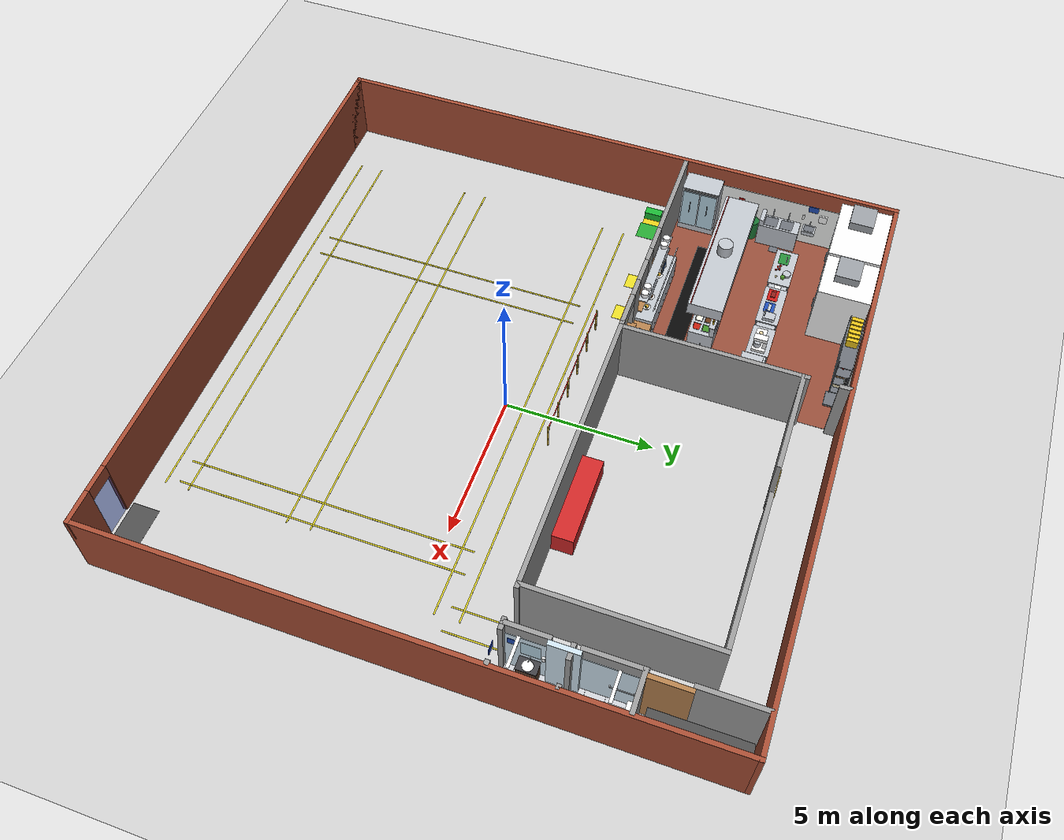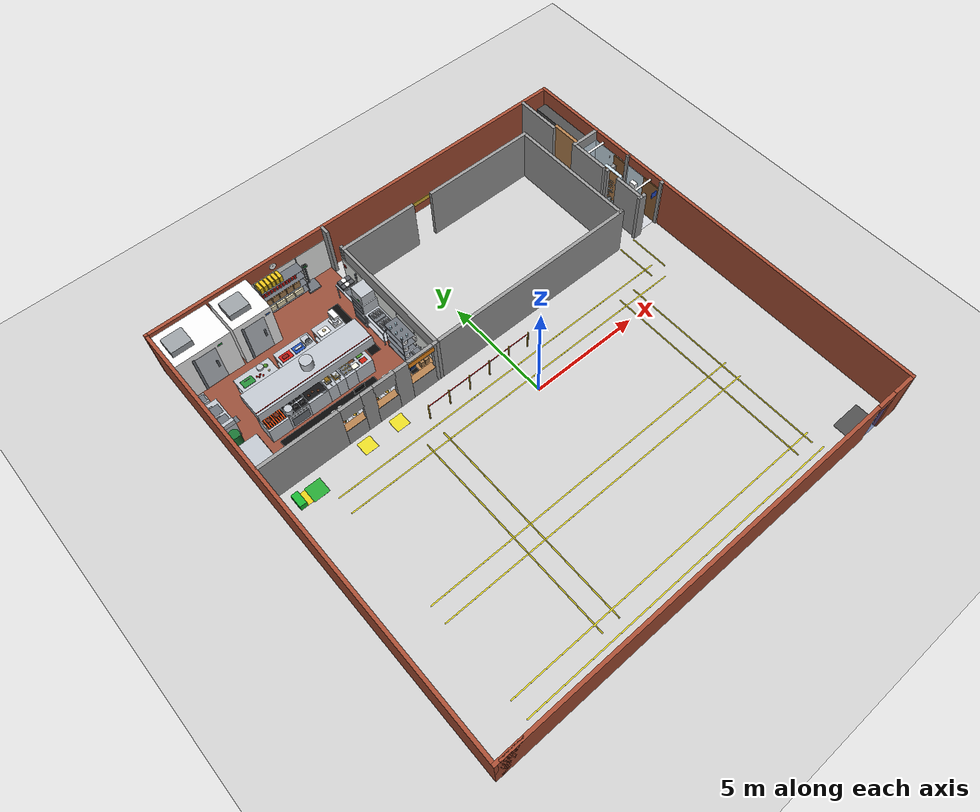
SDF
<sdf version="1.7">
 <world name="default">
  <light name="sun" type="directional">
   <pose>0 0 10 0 -0 0</pose>
   <diffuse>0.8 0.8 0.8 1</diffuse>
   <specular>0.2 0.2 0.2 1</specular>
   <attenuation>
    <range>1000</range>
    <constant>0.9</constant>
    <linear>0.01</linear>
    <quadratic>0.001</quadratic>
   </attenuation>
   <direction>-0.5 0.1 -0.9</direction>
   <spot><inner_angle>0</inner_angle><outer_angle>0</outer_angle><falloff>0</falloff></spot>
  </light>
  <model name="ground_plane">
   <static>1</static>
   <link name="link">
    <collision name="collision">
     <geometry><plane><normal>0 0 1</normal><size>100 100</size></plane></geometry>
     <surface><friction><ode><mu>100</mu><mu2>50</mu2></ode></friction></surface>
    </collision>
    <visual name="visual">
     <cast_shadows>0</cast_shadows>
     <geometry><plane><normal>0 0 1</normal><size>100 100</size></plane></geometry>
     <material>
      <script><uri>file://media/materials/scripts/gazebo.material</uri><name>Gazebo/Grey</name></script>
     </material>
    </visual>
   </link>
  </model>
  <gravity>0 0 -9.8</gravity>
  <magnetic_field>6e-06 2.3e-05 -4.2e-05</magnetic_field>
  <atmosphere type="adiabatic"/>
  <physics type="ode">
   <max_step_size>0.001</max_step_size>
   <real_time_factor>1</real_time_factor>
   <real_time_update_rate>1000</real_time_update_rate>
  </physics>
  <scene><ambient>0.4 0.4 0.4 1</ambient><background>0.7 0.7 0.7 1</background><shadows>0</shadows></scene>
  <audio><device>default</device></audio>
  <spherical_coordinates>
   <surface_model>EARTH_WGS84</surface_model>
   <latitude_deg>0</latitude_deg>
   <longitude_deg>0</longitude_deg>
   <elevation>0</elevation>
   <heading_deg>0</heading_deg>
  </spherical_coordinates>
  <model name="Untitled">
   <pose>-0.482213 0.363901 0 0 -0 0</pose>
   <link name="Wall_11">
    <collision name="Wall_11_Collision">
     <geometry><box><size>20.25 0.15 2.5</size></box></geometry>
     <pose>0 0 1.25 0 -0 0</pose>
    </collision>
    <visual name="Wall_11_Visual">
     <pose>0 0 1.25 0 -0 0</pose>
     <geometry><box><size>20.25 0.15 2.5</size></box></geometry>
     <material>
      <script><uri>file://media/materials/scripts/gazebo.material</uri><name>Gazebo/Bricks</name></script>
      <ambient>1 1 1 1</ambient>
     </material>
     <meta><layer>0</layer></meta>
    </visual>
    <pose>10.0902 0 0 0 -0 1.5708</pose>
   </link>
   <link name="Wall_12">
    <collision name="Wall_12_Collision">
     <geometry><box><size>20.25 0.15 2.5</size></box></geometry>
     <pose>0 0 1.25 0 -0 0</pose>
    </collision>
    <visual name="Wall_12_Visual">
     <pose>0 0 1.25 0 -0 0</pose>
     <geometry><box><size>20.25 0.15 2.5</size></box></geometry>
     <material>
      <script><uri>file://media/materials/scripts/gazebo.material</uri><name>Gazebo/Bricks</name></script>
      <ambient>1 1 1 1</ambient>
     </material>
     <meta><layer>0</layer></meta>
    </visual>
    <pose>0.040229 10.05 0 0 -0 3.14159</pose>
   </link>
   <link name="Wall_13">
    <collision name="Wall_13_Collision">
     <geometry><box><size>20.25 0.15 2.5</size></box></geometry>
     <pose>0 0 1.25 0 -0 0</pose>
    </collision>
    <visual name="Wall_13_Visual">
     <pose>0 0 1.25 0 -0 0</pose>
     <geometry><box><size>20.25 0.15 2.5</size></box></geometry>
     <material>
      <script><uri>file://media/materials/scripts/gazebo.material</uri><name>Gazebo/Bricks</name></script>
      <ambient>1 1 1 1</ambient>
     </material>
     <meta><layer>0</layer></meta>
    </visual>
    <pose>-10.0098 0 0 0 -0 -1.5708</pose>
   </link>
   <link name="Wall_14">
    <collision name="Wall_14_Collision">
     <geometry><box><size>1.25 0.15 2.5</size></box></geometry>
     <pose>0 0 1.25 0 -0 0</pose>
    </collision>
    <visual name="Wall_14_Visual">
     <pose>0 0 1.25 0 -0 0</pose>
     <geometry><box><size>1.25 0.15 2.5</size></box></geometry>
     <material>
      <script><uri>file://media/materials/scripts/gazebo.material</uri><name>Gazebo/Bricks</name></script>
      <ambient>1 1 1 1</ambient>
     </material>
     <meta><layer>0</layer></meta>
    </visual>
    <pose>-9.45977 -10.05 0 0 -0 0</pose>
   </link>
   <link name="Wall_9">
    <pose>0.165229 -10.05 0 0 -0 0</pose>
    <visual name="Wall_9_Visual_0">
     <pose>-1.01654 0 1.25 0 -0 0</pose>
     <geometry><box><size>17.9669 0.15 2.5</size></box></geometry>
     <material>
      <script><uri>file://media/materials/scripts/gazebo.material</uri><name>Gazebo/Bricks</name></script>
      <ambient>1 1 1 1</ambient>
     </material>
     <meta><layer>0</layer></meta>
    </visual>
    <collision name="Wall_9_Collision_0">
     <geometry><box><size>17.9669 0.15 2.5</size></box></geometry>
     <pose>-1.01654 0 1.25 0 -0 0</pose>
    </collision>
    <visual name="Wall_9_Visual_1">
     <pose>9.43346 0 1.25 0 -0 0</pose>
     <geometry><box><size>1.13309 0.15 2.5</size></box></geometry>
     <material>
      <script><uri>file://media/materials/scripts/gazebo.material</uri><name>Gazebo/Bricks</name></script>
      <ambient>1 1 1 1</ambient>
     </material>
     <meta><layer>0</layer></meta>
    </visual>
    <collision name="Wall_9_Collision_1">
     <geometry><box><size>1.13309 0.15 2.5</size></box></geometry>
     <pose>9.43346 0 1.25 0 -0 0</pose>
    </collision>
    <visual name="Wall_9_Visual_2">
     <pose>8.41691 0 2.25 0 -0 0</pose>
     <geometry><box><size>0.9 0.15 0.5</size></box></geometry>
     <material>
      <script><uri>file://media/materials/scripts/gazebo.material</uri><name>Gazebo/Bricks</name></script>
      <ambient>1 1 1 1</ambient>
     </material>
     <meta><layer>0</layer></meta>
    </visual>
    <collision name="Wall_9_Collision_2">
     <geometry><box><size>0.9 0.15 0.5</size></box></geometry>
     <pose>8.41691 0 2.25 0 -0 0</pose>
    </collision>
   </link>
   <static>1</static>
  </model>
  <model name="docking_station">
   <static>1</static>
   <pose>-9.75 2.2 0 0 0 0</pose>
   <link name="link">
    <collision name="collision">
     <pose>0 0 0.15 0 0 0</pose>
     <geometry><box><size>0.3 0.6 0.3</size></box></geometry>
    </collision>
    <visual name="visual">
     <pose>0 0 0.15 0 0 0</pose>
     <geometry><box><size>0.3 0.6 0.3</size></box></geometry>
     <material><ambient>0.1 0.7 0.2 1</ambient><diffuse>0.1 0.7 0.2 1</diffuse></material>
    </visual>
    <visual name="pad">
     <pose>0.55 0 0.001 0 0 0</pose>
     <geometry><box><size>0.8 0.6 0.002</size></box></geometry>
     <material><ambient>0.9 0.8 0.1 1</ambient><diffuse>0.9 0.8 0.1 1</diffuse></material>
    </visual>
   </link>
  </model>
  <model name="tunibot_layout">
   <static>1</static>
   <link name="wall_0">
    <pose>2.337 3.000 1.250 0 0 0.0000</pose>
    <collision name="wall_0_collision"><geometry><box><size>9.825 0.150 2.500</size></box></geometry></collision>
    <visual name="wall_0_visual">
     <geometry><box><size>9.825 0.150 2.500</size></box></geometry>
     <material>
      <script><uri>file://media/materials/scripts/gazebo.material</uri><name>Gazebo/Grey</name></script>
     </material>
    </visual>
   </link>
   <link name="wall_1">
    <pose>8.350 3.000 1.250 0 0 0.0000</pose>
    <collision name="wall_1_collision"><geometry><box><size>0.400 0.150 2.500</size></box></geometry></collision>
    <visual name="wall_1_visual">
     <geometry><box><size>0.400 0.150 2.500</size></box></geometry>
     <material>
      <script><uri>file://media/materials/scripts/gazebo.material</uri><name>Gazebo/Grey</name></script>
     </material>
    </visual>
   </link>
   <link name="wall_2">
    <pose>9.530 3.000 1.250 0 0 0.0000</pose>
    <collision name="wall_2_collision"><geometry><box><size>0.160 0.150 2.500</size></box></geometry></collision>
    <visual name="wall_2_visual">
     <geometry><box><size>0.160 0.150 2.500</size></box></geometry>
     <material>
      <script><uri>file://media/materials/scripts/gazebo.material</uri><name>Gazebo/Grey</name></script>
     </material>
    </visual>
   </link>
   <link name="wall_3">
    <pose>-2.500 6.012 1.250 0 0 1.5708</pose>
    <collision name="wall_3_collision"><geometry><box><size>6.175 0.150 2.500</size></box></geometry></collision>
    <visual name="wall_3_visual">
     <geometry><box><size>6.175 0.150 2.500</size></box></geometry>
     <material>
      <script><uri>file://media/materials/scripts/gazebo.material</uri><name>Gazebo/Grey</name></script>
     </material>
    </visual>
   </link>
   <link name="wall_4">
    <pose>-2.500 10.207 1.250 0 0 1.5708</pose>
    <collision name="wall_4_collision"><geometry><box><size>0.415 0.150 2.500</size></box></geometry></collision>
    <visual name="wall_4_visual">
     <geometry><box><size>0.415 0.150 2.500</size></box></geometry>
     <material>
      <script><uri>file://media/materials/scripts/gazebo.material</uri><name>Gazebo/Grey</name></script>
     </material>
    </visual>
   </link>
   <link name="wall_5">
    <pose>7.100 5.950 1.250 0 0 1.5708</pose>
    <collision name="wall_5_collision"><geometry><box><size>6.050 0.150 2.500</size></box></geometry></collision>
    <visual name="wall_5_visual">
     <geometry><box><size>6.050 0.150 2.500</size></box></geometry>
     <material>
      <script><uri>file://media/materials/scripts/gazebo.material</uri><name>Gazebo/Grey</name></script>
     </material>
    </visual>
   </link>
   <link name="wall_6">
    <pose>8.300 3.663 1.250 0 0 1.5708</pose>
    <collision name="wall_6_collision"><geometry><box><size>1.475 0.150 2.500</size></box></geometry></collision>
    <visual name="wall_6_visual">
     <geometry><box><size>1.475 0.150 2.500</size></box></geometry>
     <material>
      <script><uri>file://media/materials/scripts/gazebo.material</uri><name>Gazebo/Grey</name></script>
     </material>
    </visual>
   </link>
   <link name="wall_7">
    <pose>8.300 6.150 1.250 0 0 1.5708</pose>
    <collision name="wall_7_collision"><geometry><box><size>1.900 0.150 2.500</size></box></geometry></collision>
    <visual name="wall_7_visual">
     <geometry><box><size>1.900 0.150 2.500</size></box></geometry>
     <material>
      <script><uri>file://media/materials/scripts/gazebo.material</uri><name>Gazebo/Grey</name></script>
     </material>
    </visual>
   </link>
   <link name="wall_8">
    <pose>8.300 9.357 1.250 0 0 1.5708</pose>
    <collision name="wall_8_collision"><geometry><box><size>2.115 0.150 2.500</size></box></geometry></collision>
    <visual name="wall_8_visual">
     <geometry><box><size>2.115 0.150 2.500</size></box></geometry>
     <material>
      <script><uri>file://media/materials/scripts/gazebo.material</uri><name>Gazebo/Grey</name></script>
     </material>
    </visual>
   </link>
   <link name="wall_9">
    <pose>-0.788 8.900 1.250 0 0 0.0000</pose>
    <collision name="wall_9_collision"><geometry><box><size>3.575 0.150 2.500</size></box></geometry></collision>
    <visual name="wall_9_visual">
     <geometry><box><size>3.575 0.150 2.500</size></box></geometry>
     <material>
      <script><uri>file://media/materials/scripts/gazebo.material</uri><name>Gazebo/Grey</name></script>
     </material>
    </visual>
   </link>
   <link name="wall_10">
    <pose>4.537 8.900 1.250 0 0 0.0000</pose>
    <collision name="wall_10_collision"><geometry><box><size>5.275 0.150 2.500</size></box></geometry></collision>
    <visual name="wall_10_visual">
     <geometry><box><size>5.275 0.150 2.500</size></box></geometry>
     <material>
      <script><uri>file://media/materials/scripts/gazebo.material</uri><name>Gazebo/Grey</name></script>
     </material>
    </visual>
   </link>
   <link name="wall_11">
    <pose>8.488 5.000 1.250 0 0 0.0000</pose>
    <collision name="wall_11_collision"><geometry><box><size>0.525 0.150 2.500</size></box></geometry></collision>
    <visual name="wall_11_visual">
     <geometry><box><size>0.525 0.150 2.500</size></box></geometry>
     <material>
      <script><uri>file://media/materials/scripts/gazebo.material</uri><name>Gazebo/Grey</name></script>
     </material>
    </visual>
   </link>
   <link name="wall_12">
    <pose>9.530 5.000 1.250 0 0 0.0000</pose>
    <collision name="wall_12_collision"><geometry><box><size>0.160 0.150 2.500</size></box></geometry></collision>
    <visual name="wall_12_visual">
     <geometry><box><size>0.160 0.150 2.500</size></box></geometry>
     <material>
      <script><uri>file://media/materials/scripts/gazebo.material</uri><name>Gazebo/Grey</name></script>
     </material>
    </visual>
   </link>
   <link name="wall_13">
    <pose>8.918 7.000 1.250 0 0 0.0000</pose>
    <collision name="wall_13_collision"><geometry><box><size>1.385 0.150 2.500</size></box></geometry></collision>
    <visual name="wall_13_visual">
     <geometry><box><size>1.385 0.150 2.500</size></box></geometry>
     <material>
      <script><uri>file://media/materials/scripts/gazebo.material</uri><name>Gazebo/Grey</name></script>
     </material>
    </visual>
   </link>
   <link name="niche_0">
    <pose>8.450 4.800 1.250 0 0 0.0000</pose>
    <collision name="niche_0_collision"><geometry><box><size>0.150 0.950 2.500</size></box></geometry></collision>
    <visual name="niche_0_visual">
     <geometry><box><size>0.150 0.950 2.500</size></box></geometry>
     <material>
      <script><uri>file://media/materials/scripts/gazebo.material</uri><name>Gazebo/Wood</name></script>
     </material>
    </visual>
   </link>
   <link name="niche_1">
    <pose>8.450 7.700 1.250 0 0 0.0000</pose>
    <collision name="niche_1_collision"><geometry><box><size>0.150 1.350 2.500</size></box></geometry></collision>
    <visual name="niche_1_visual">
     <geometry><box><size>0.150 1.350 2.500</size></box></geometry>
     <material>
      <script><uri>file://media/materials/scripts/gazebo.material</uri><name>Gazebo/Wood</name></script>
     </material>
    </visual>
   </link>
   <link name="partition_pier_0">
    <pose>-8.707 3.000 1.250 0 0 0.0000</pose>
    <collision name="partition_pier_0_collision">
     <geometry><box><size>3.490 0.150 2.500</size></box></geometry>
    </collision>
    <visual name="partition_pier_0_visual">
     <geometry><box><size>3.490 0.150 2.500</size></box></geometry>
     <material>
      <script><uri>file://media/materials/scripts/gazebo.material</uri><name>Gazebo/Grey</name></script>
     </material>
    </visual>
   </link>
   <link name="window_1_sill">
    <pose>-6.500 3.000 0.475 0 0 0.0000</pose>
    <collision name="window_1_sill_collision">
     <geometry><box><size>1.000 0.150 0.950</size></box></geometry>
    </collision>
    <visual name="window_1_sill_visual">
     <geometry><box><size>1.000 0.150 0.950</size></box></geometry>
     <material>
      <script><uri>file://media/materials/scripts/gazebo.material</uri><name>Gazebo/Grey</name></script>
     </material>
    </visual>
   </link>
   <link name="window_1_lintel">
    <pose>-6.500 3.000 2.125 0 0 0.0000</pose>
    <collision name="window_1_lintel_collision">
     <geometry><box><size>1.000 0.150 0.750</size></box></geometry>
    </collision>
    <visual name="window_1_lintel_visual">
     <geometry><box><size>1.000 0.150 0.750</size></box></geometry>
     <material>
      <script><uri>file://media/materials/scripts/gazebo.material</uri><name>Gazebo/Grey</name></script>
     </material>
    </visual>
   </link>
   <link name="window_1_ledge">
    <pose>-6.500 3.075 0.965 0 0 0.0000</pose>
    <collision name="window_1_ledge_collision">
     <geometry><box><size>1.000 0.300 0.030</size></box></geometry>
    </collision>
    <visual name="window_1_ledge_visual">
     <geometry><box><size>1.000 0.300 0.030</size></box></geometry>
     <material>
      <script><uri>file://media/materials/scripts/gazebo.material</uri><name>Gazebo/Wood</name></script>
     </material>
    </visual>
   </link>
   <link name="partition_pier_1">
    <pose>-5.750 3.000 1.250 0 0 0.0000</pose>
    <collision name="partition_pier_1_collision">
     <geometry><box><size>0.575 0.150 2.500</size></box></geometry>
    </collision>
    <visual name="partition_pier_1_visual">
     <geometry><box><size>0.575 0.150 2.500</size></box></geometry>
     <material>
      <script><uri>file://media/materials/scripts/gazebo.material</uri><name>Gazebo/Grey</name></script>
     </material>
    </visual>
   </link>
   <link name="window_2_sill">
    <pose>-5.000 3.000 0.475 0 0 0.0000</pose>
    <collision name="window_2_sill_collision">
     <geometry><box><size>1.000 0.150 0.950</size></box></geometry>
    </collision>
    <visual name="window_2_sill_visual">
     <geometry><box><size>1.000 0.150 0.950</size></box></geometry>
     <material>
      <script><uri>file://media/materials/scripts/gazebo.material</uri><name>Gazebo/Grey</name></script>
     </material>
    </visual>
   </link>
   <link name="window_2_lintel">
    <pose>-5.000 3.000 2.125 0 0 0.0000</pose>
    <collision name="window_2_lintel_collision">
     <geometry><box><size>1.000 0.150 0.750</size></box></geometry>
    </collision>
    <visual name="window_2_lintel_visual">
     <geometry><box><size>1.000 0.150 0.750</size></box></geometry>
     <material>
      <script><uri>file://media/materials/scripts/gazebo.material</uri><name>Gazebo/Grey</name></script>
     </material>
    </visual>
   </link>
   <link name="window_2_ledge">
    <pose>-5.000 3.075 0.965 0 0 0.0000</pose>
    <collision name="window_2_ledge_collision">
     <geometry><box><size>1.000 0.300 0.030</size></box></geometry>
    </collision>
    <visual name="window_2_ledge_visual">
     <geometry><box><size>1.000 0.300 0.030</size></box></geometry>
     <material>
      <script><uri>file://media/materials/scripts/gazebo.material</uri><name>Gazebo/Wood</name></script>
     </material>
    </visual>
   </link>
   <link name="partition_pier_2">
    <pose>-4.200 3.000 1.250 0 0 0.0000</pose>
    <collision name="partition_pier_2_collision">
     <geometry><box><size>0.675 0.150 2.500</size></box></geometry>
    </collision>
    <visual name="partition_pier_2_visual">
     <geometry><box><size>0.675 0.150 2.500</size></box></geometry>
     <material>
      <script><uri>file://media/materials/scripts/gazebo.material</uri><name>Gazebo/Grey</name></script>
     </material>
    </visual>
   </link>
   <link name="takeaway_sill">
    <pose>-3.300 3.000 0.500 0 0 0.0000</pose>
    <collision name="takeaway_sill_collision">
     <geometry><box><size>1.200 0.150 1.000</size></box></geometry>
    </collision>
    <visual name="takeaway_sill_visual">
     <geometry><box><size>1.200 0.150 1.000</size></box></geometry>
     <material>
      <script><uri>file://media/materials/scripts/gazebo.material</uri><name>Gazebo/Grey</name></script>
     </material>
    </visual>
   </link>
   <link name="takeaway_lintel">
    <pose>-3.300 3.000 2.300 0 0 0.0000</pose>
    <collision name="takeaway_lintel_collision">
     <geometry><box><size>1.200 0.150 0.400</size></box></geometry>
    </collision>
    <visual name="takeaway_lintel_visual">
     <geometry><box><size>1.200 0.150 0.400</size></box></geometry>
     <material>
      <script><uri>file://media/materials/scripts/gazebo.material</uri><name>Gazebo/Grey</name></script>
     </material>
    </visual>
   </link>
   <link name="takeaway_ledge">
    <pose>-3.300 3.075 1.015 0 0 0.0000</pose>
    <collision name="takeaway_ledge_collision">
     <geometry><box><size>1.200 0.300 0.030</size></box></geometry>
    </collision>
    <visual name="takeaway_ledge_visual">
     <geometry><box><size>1.200 0.300 0.030</size></box></geometry>
     <material>
      <script><uri>file://media/materials/scripts/gazebo.material</uri><name>Gazebo/Wood</name></script>
     </material>
    </visual>
   </link>
   <link name="partition_pier_3">
    <pose>-2.600 3.000 1.250 0 0 0.0000</pose>
    <collision name="partition_pier_3_collision">
     <geometry><box><size>0.275 0.150 2.500</size></box></geometry>
    </collision>
    <visual name="partition_pier_3_visual">
     <geometry><box><size>0.275 0.150 2.500</size></box></geometry>
     <material>
      <script><uri>file://media/materials/scripts/gazebo.material</uri><name>Gazebo/Grey</name></script>
     </material>
    </visual>
   </link>
   <link name="takeaway_counter">
    <pose>-3.300 3.400 0.500 0 0 0.0000</pose>
    <collision name="takeaway_counter_collision">
     <geometry><box><size>1.500 0.600 1.000</size></box></geometry>
    </collision>
    <visual name="takeaway_counter_visual">
     <geometry><box><size>1.500 0.600 1.000</size></box></geometry>
     <material>
      <script><uri>file://media/materials/scripts/gazebo.material</uri><name>Gazebo/Wood</name></script>
     </material>
    </visual>
   </link>
   <link name="lounge_sofa">
    <pose>3.000 3.450 0.400 0 0 0.0000</pose>
    <collision name="lounge_sofa_collision">
     <geometry><box><size>3.000 0.700 0.800</size></box></geometry>
    </collision>
    <visual name="lounge_sofa_visual">
     <geometry><box><size>3.000 0.700 0.800</size></box></geometry>
     <material>
      <script><uri>file://media/materials/scripts/gazebo.material</uri><name>Gazebo/Red</name></script>
     </material>
    </visual>
   </link>
   <link name="storage_rack">
    <pose>9.250 8.750 0.900 0 0 0.0000</pose>
    <collision name="storage_rack_collision">
     <geometry><box><size>0.500 2.900 1.800</size></box></geometry>
    </collision>
    <visual name="storage_rack_visual">
     <geometry><box><size>0.500 2.900 1.800</size></box></geometry>
     <material>
      <script><uri>file://media/materials/scripts/gazebo.material</uri><name>Gazebo/DarkGrey</name></script>
     </material>
    </visual>
   </link>
   <link name="entrance_door">
    <pose>8.075 -9.686 1.100 0 0 0.0000</pose>
    <collision name="entrance_door_collision">
     <geometry><box><size>1.050 0.060 2.200</size></box></geometry>
    </collision>
    <visual name="entrance_door_visual">
     <geometry><box><size>1.050 0.060 2.200</size></box></geometry>
     <material>
      <script><uri>file://media/materials/scripts/gazebo.material</uri><name>Gazebo/BlueTransparent</name></script>
     </material>
    </visual>
   </link>
   <link name="stanchion_0">
    <pose>-4.0 1.8 0.5 0 0 0</pose>
    <collision name="stanchion_0_collision">
     <geometry><cylinder><radius>0.03</radius><length>1.0</length></cylinder></geometry>
    </collision>
    <visual name="stanchion_0_visual">
     <geometry><cylinder><radius>0.03</radius><length>1.0</length></cylinder></geometry>
     <material>
      <script><uri>file://media/materials/scripts/gazebo.material</uri><name>Gazebo/Gold</name></script>
     </material>
    </visual>
   </link>
   <link name="stanchion_1">
    <pose>-3.0 1.8 0.5 0 0 0</pose>
    <collision name="stanchion_1_collision">
     <geometry><cylinder><radius>0.03</radius><length>1.0</length></cylinder></geometry>
    </collision>
    <visual name="stanchion_1_visual">
     <geometry><cylinder><radius>0.03</radius><length>1.0</length></cylinder></geometry>
     <material>
      <script><uri>file://media/materials/scripts/gazebo.material</uri><name>Gazebo/Gold</name></script>
     </material>
    </visual>
   </link>
   <link name="stanchion_2">
    <pose>-2.0 1.8 0.5 0 0 0</pose>
    <collision name="stanchion_2_collision">
     <geometry><cylinder><radius>0.03</radius><length>1.0</length></cylinder></geometry>
    </collision>
    <visual name="stanchion_2_visual">
     <geometry><cylinder><radius>0.03</radius><length>1.0</length></cylinder></geometry>
     <material>
      <script><uri>file://media/materials/scripts/gazebo.material</uri><name>Gazebo/Gold</name></script>
     </material>
    </visual>
   </link>
   <link name="stanchion_3">
    <pose>-1.0 1.8 0.5 0 0 0</pose>
    <collision name="stanchion_3_collision">
     <geometry><cylinder><radius>0.03</radius><length>1.0</length></cylinder></geometry>
    </collision>
    <visual name="stanchion_3_visual">
     <geometry><cylinder><radius>0.03</radius><length>1.0</length></cylinder></geometry>
     <material>
      <script><uri>file://media/materials/scripts/gazebo.material</uri><name>Gazebo/Gold</name></script>
     </material>
    </visual>
   </link>
   <link name="stanchion_4">
    <pose>0.0 1.8 0.5 0 0 0</pose>
    <collision name="stanchion_4_collision">
     <geometry><cylinder><radius>0.03</radius><length>1.0</length></cylinder></geometry>
    </collision>
    <visual name="stanchion_4_visual">
     <geometry><cylinder><radius>0.03</radius><length>1.0</length></cylinder></geometry>
     <material>
      <script><uri>file://media/materials/scripts/gazebo.material</uri><name>Gazebo/Gold</name></script>
     </material>
    </visual>
   </link>
   <link name="stanchion_5">
    <pose>1.0 1.8 0.5 0 0 0</pose>
    <collision name="stanchion_5_collision">
     <geometry><cylinder><radius>0.03</radius><length>1.0</length></cylinder></geometry>
    </collision>
    <visual name="stanchion_5_visual">
     <geometry><cylinder><radius>0.03</radius><length>1.0</length></cylinder></geometry>
     <material>
      <script><uri>file://media/materials/scripts/gazebo.material</uri><name>Gazebo/Gold</name></script>
     </material>
    </visual>
   </link>
   <link name="rope_0">
    <pose>-3.500 1.800 0.900 0 0 0.0000</pose>
    <visual name="rope_0_visual">
     <geometry><box><size>1.000 0.030 0.030</size></box></geometry>
     <material>
      <script><uri>file://media/materials/scripts/gazebo.material</uri><name>Gazebo/Red</name></script>
     </material>
    </visual>
   </link>
   <link name="rope_1">
    <pose>-2.500 1.800 0.900 0 0 0.0000</pose>
    <visual name="rope_1_visual">
     <geometry><box><size>1.000 0.030 0.030</size></box></geometry>
     <material>
      <script><uri>file://media/materials/scripts/gazebo.material</uri><name>Gazebo/Red</name></script>
     </material>
    </visual>
   </link>
   <link name="rope_2">
    <pose>-1.500 1.800 0.900 0 0 0.0000</pose>
    <visual name="rope_2_visual">
     <geometry><box><size>1.000 0.030 0.030</size></box></geometry>
     <material>
      <script><uri>file://media/materials/scripts/gazebo.material</uri><name>Gazebo/Red</name></script>
     </material>
    </visual>
   </link>
   <link name="rope_3">
    <pose>-0.500 1.800 0.900 0 0 0.0000</pose>
    <visual name="rope_3_visual">
     <geometry><box><size>1.000 0.030 0.030</size></box></geometry>
     <material>
      <script><uri>file://media/materials/scripts/gazebo.material</uri><name>Gazebo/Red</name></script>
     </material>
    </visual>
   </link>
   <link name="rope_4">
    <pose>0.500 1.800 0.900 0 0 0.0000</pose>
    <visual name="rope_4_visual">
     <geometry><box><size>1.000 0.030 0.030</size></box></geometry>
     <material>
      <script><uri>file://media/materials/scripts/gazebo.material</uri><name>Gazebo/Red</name></script>
     </material>
    </visual>
   </link>
   <link name="sign_takeaway">
    <pose>-3.300 2.910 2.300 0 0 0.0000</pose>
    <visual name="sign_takeaway_visual">
     <geometry><box><size>1.200 0.020 0.250</size></box></geometry>
     <material>
      <script><uri>file://media/materials/scripts/gazebo.material</uri><name>Gazebo/Orange</name></script>
     </material>
    </visual>
   </link>
   <link name="sign_wc">
    <pose>9.000 2.910 2.200 0 0 0.0000</pose>
    <visual name="sign_wc_visual">
     <geometry><box><size>0.300 0.020 0.300</size></box></geometry>
     <material>
      <script><uri>file://media/materials/scripts/gazebo.material</uri><name>Gazebo/Blue</name></script>
     </material>
    </visual>
   </link>
   <link name="sign_vip">
    <pose>1.450 8.990 2.300 0 0 0.0000</pose>
    <visual name="sign_vip_visual">
     <geometry><box><size>0.900 0.020 0.200</size></box></geometry>
     <material>
      <script><uri>file://media/materials/scripts/gazebo.material</uri><name>Gazebo/Gold</name></script>
     </material>
    </visual>
   </link>
   <link name="mark_dock">
    <pose>-9.000 2.200 0.002 0 0 0.0000</pose>
    <visual name="mark_dock_visual">
     <geometry><box><size>0.700 0.700 0.004</size></box></geometry>
     <material>
      <script><uri>file://media/materials/scripts/gazebo.material</uri><name>Gazebo/Green</name></script>
     </material>
    </visual>
   </link>
   <link name="mark_entrance">
    <pose>8.075 -9.100 0.002 0 0 0.0000</pose>
    <visual name="mark_entrance_visual">
     <geometry><box><size>1.400 0.900 0.004</size></box></geometry>
     <material>
      <script><uri>file://media/materials/scripts/gazebo.material</uri><name>Gazebo/DarkGrey</name></script>
     </material>
    </visual>
   </link>
   <link name="mark_window_1">
    <pose>-6.500 2.450 0.002 0 0 0.0000</pose>
    <visual name="mark_window_1_visual">
     <geometry><box><size>0.600 0.600 0.004</size></box></geometry>
     <material>
      <script><uri>file://media/materials/scripts/gazebo.material</uri><name>Gazebo/Yellow</name></script>
     </material>
    </visual>
   </link>
   <link name="mark_window_2">
    <pose>-5.000 2.450 0.002 0 0 0.0000</pose>
    <visual name="mark_window_2_visual">
     <geometry><box><size>0.600 0.600 0.004</size></box></geometry>
     <material>
      <script><uri>file://media/materials/scripts/gazebo.material</uri><name>Gazebo/Yellow</name></script>
     </material>
    </visual>
   </link>
   <link name="lane_0_l">
    <pose>-0.450 0.600 0.002 0 0 0.0000</pose>
    <visual name="lane_0_l_visual">
     <geometry><box><size>16.300 0.050 0.004</size></box></geometry>
     <material>
      <script><uri>file://media/materials/scripts/gazebo.material</uri><name>Gazebo/Yellow</name></script>
     </material>
    </visual>
   </link>
   <link name="lane_0_r">
    <pose>-0.450 1.400 0.002 0 0 0.0000</pose>
    <visual name="lane_0_r_visual">
     <geometry><box><size>16.300 0.050 0.004</size></box></geometry>
     <material>
      <script><uri>file://media/materials/scripts/gazebo.material</uri><name>Gazebo/Yellow</name></script>
     </material>
    </visual>
   </link>
   <link name="lane_1_l">
    <pose>8.100 1.950 0.002 0 0 1.5708</pose>
    <visual name="lane_1_l_visual">
     <geometry><box><size>1.900 0.050 0.004</size></box></geometry>
     <material>
      <script><uri>file://media/materials/scripts/gazebo.material</uri><name>Gazebo/Yellow</name></script>
     </material>
    </visual>
   </link>
   <link name="lane_1_r">
    <pose>7.300 1.950 0.002 0 0 1.5708</pose>
    <visual name="lane_1_r_visual">
     <geometry><box><size>1.900 0.050 0.004</size></box></geometry>
     <material>
      <script><uri>file://media/materials/scripts/gazebo.material</uri><name>Gazebo/Yellow</name></script>
     </material>
    </visual>
   </link>
   <link name="lane_2_l">
    <pose>-4.800 -3.800 0.002 0 0 -1.5708</pose>
    <visual name="lane_2_l_visual">
     <geometry><box><size>9.600 0.050 0.004</size></box></geometry>
     <material>
      <script><uri>file://media/materials/scripts/gazebo.material</uri><name>Gazebo/Yellow</name></script>
     </material>
    </visual>
   </link>
   <link name="lane_2_r">
    <pose>-4.000 -3.800 0.002 0 0 -1.5708</pose>
    <visual name="lane_2_r_visual">
     <geometry><box><size>9.600 0.050 0.004</size></box></geometry>
     <material>
      <script><uri>file://media/materials/scripts/gazebo.material</uri><name>Gazebo/Yellow</name></script>
     </material>
    </visual>
   </link>
   <link name="lane_3_l">
    <pose>5.400 -3.800 0.002 0 0 -1.5708</pose>
    <visual name="lane_3_l_visual">
     <geometry><box><size>9.600 0.050 0.004</size></box></geometry>
     <material>
      <script><uri>file://media/materials/scripts/gazebo.material</uri><name>Gazebo/Yellow</name></script>
     </material>
    </visual>
   </link>
   <link name="lane_3_r">
    <pose>6.200 -3.800 0.002 0 0 -1.5708</pose>
    <visual name="lane_3_r_visual">
     <geometry><box><size>9.600 0.050 0.004</size></box></geometry>
     <material>
      <script><uri>file://media/materials/scripts/gazebo.material</uri><name>Gazebo/Yellow</name></script>
     </material>
    </visual>
   </link>
   <link name="lane_4_l">
    <pose>-1.100 -4.800 0.002 0 0 0.0000</pose>
    <visual name="lane_4_l_visual">
     <geometry><box><size>15.000 0.050 0.004</size></box></geometry>
     <material>
      <script><uri>file://media/materials/scripts/gazebo.material</uri><name>Gazebo/Yellow</name></script>
     </material>
    </visual>
   </link>
   <link name="lane_4_r">
    <pose>-1.100 -4.000 0.002 0 0 0.0000</pose>
    <visual name="lane_4_r_visual">
     <geometry><box><size>15.000 0.050 0.004</size></box></geometry>
     <material>
      <script><uri>file://media/materials/scripts/gazebo.material</uri><name>Gazebo/Yellow</name></script>
     </material>
    </visual>
   </link>
   <link name="lane_5_l">
    <pose>-1.100 -9.000 0.002 0 0 0.0000</pose>
    <visual name="lane_5_l_visual">
     <geometry><box><size>15.000 0.050 0.004</size></box></geometry>
     <material>
      <script><uri>file://media/materials/scripts/gazebo.material</uri><name>Gazebo/Yellow</name></script>
     </material>
    </visual>
   </link>
   <link name="lane_5_r">
    <pose>-1.100 -8.200 0.002 0 0 0.0000</pose>
    <visual name="lane_5_r_visual">
     <geometry><box><size>15.000 0.050 0.004</size></box></geometry>
     <material>
      <script><uri>file://media/materials/scripts/gazebo.material</uri><name>Gazebo/Yellow</name></script>
     </material>
    </visual>
   </link>
   <link name="k_floor">
    <visual name="k_floor_v0">
     <pose>-6.495 6.707 0.002 0 0 0.0000</pose>
     <geometry><box><size>7.840 7.265 0.003</size></box></geometry>
     <material>
      <ambient>0.35 0.18 0.13 1</ambient>
      <diffuse>0.58 0.30 0.22 1</diffuse>
      <specular>0.30 0.30 0.30 1</specular>
     </material>
    </visual>
    <visual name="k_floor_v1">
     <pose>-6.700 4.300 0.004 0 0 0.0000</pose>
     <geometry><box><size>0.300 0.300 0.002</size></box></geometry>
     <material>
      <ambient>0.25 0.26 0.28 1</ambient>
      <diffuse>0.42 0.44 0.47 1</diffuse>
      <specular>0.60 0.60 0.60 1</specular>
     </material>
    </visual>
    <visual name="k_floor_v2">
     <pose>-3.750 7.200 0.004 0 0 0.0000</pose>
     <geometry><box><size>0.300 0.300 0.002</size></box></geometry>
     <material>
      <ambient>0.25 0.26 0.28 1</ambient>
      <diffuse>0.42 0.44 0.47 1</diffuse>
      <specular>0.60 0.60 0.60 1</specular>
     </material>
    </visual>
    <visual name="k_floor_v3">
     <pose>-9.700 6.700 0.004 0 0 0.0000</pose>
     <geometry><box><size>0.300 0.300 0.002</size></box></geometry>
     <material>
      <ambient>0.25 0.26 0.28 1</ambient>
      <diffuse>0.42 0.44 0.47 1</diffuse>
      <specular>0.60 0.60 0.60 1</specular>
     </material>
    </visual>
    <visual name="k_floor_v4">
     <pose>-6.700 4.450 0.010 0 0 0.0000</pose>
     <geometry><box><size>4.400 0.660 0.013</size></box></geometry>
     <material>
      <ambient>0.02 0.02 0.02 1</ambient>
      <diffuse>0.03 0.03 0.03 1</diffuse>
      <specular>0.15 0.15 0.15 1</specular>
     </material>
    </visual>
    <visual name="k_floor_v5">
     <pose>-3.750 7.100 0.010 0 0 0.0000</pose>
     <geometry><box><size>0.460 3.000 0.013</size></box></geometry>
     <material>
      <ambient>0.02 0.02 0.02 1</ambient>
      <diffuse>0.03 0.03 0.03 1</diffuse>
      <specular>0.15 0.15 0.15 1</specular>
     </material>
    </visual>
    <visual name="k_floor_v6">
     <pose>-10.409 6.707 0.900 0 0 0.0000</pose>
     <geometry><box><size>0.012 7.265 1.800</size></box></geometry>
     <material>
      <ambient>0.56 0.56 0.56 1</ambient>
      <diffuse>0.93 0.94 0.93 1</diffuse>
      <specular>0.50 0.50 0.50 1</specular>
     </material>
    </visual>
    <visual name="k_floor_v7">
     <pose>-6.495 10.334 0.900 0 0 0.0000</pose>
     <geometry><box><size>7.840 0.012 1.800</size></box></geometry>
     <material>
      <ambient>0.56 0.56 0.56 1</ambient>
      <diffuse>0.93 0.94 0.93 1</diffuse>
      <specular>0.50 0.50 0.50 1</specular>
     </material>
    </visual>
    <visual name="k_floor_v8">
     <pose>-2.581 6.088 0.900 0 0 0.0000</pose>
     <geometry><box><size>0.012 6.025 1.800</size></box></geometry>
     <material>
      <ambient>0.56 0.56 0.56 1</ambient>
      <diffuse>0.93 0.94 0.93 1</diffuse>
      <specular>0.50 0.50 0.50 1</specular>
     </material>
    </visual>
   </link>
   <link name="k_pass">
    <collision name="k_pass_c0">
     <pose>-5.750 3.375 0.475 0 0 0.0000</pose>
     <geometry><box><size>3.100 0.600 0.950</size></box></geometry>
    </collision>
    <visual name="k_pass_v0">
     <pose>-5.750 3.375 0.475 0 0 0.0000</pose>
     <geometry><box><size>3.100 0.600 0.950</size></box></geometry>
     <material>
      <ambient>0.44 0.46 0.47 1</ambient>
      <diffuse>0.74 0.76 0.79 1</diffuse>
      <specular>0.80 0.80 0.80 1</specular>
     </material>
    </visual>
    <visual name="k_pass_v1">
     <pose>-5.750 3.375 0.260 0 0 0.0000</pose>
     <geometry><box><size>3.100 0.600 0.020</size></box></geometry>
     <material>
      <ambient>0.25 0.26 0.28 1</ambient>
      <diffuse>0.42 0.44 0.47 1</diffuse>
      <specular>0.15 0.15 0.15 1</specular>
     </material>
    </visual>
    <visual name="k_pass_v2">
     <pose>-6.500 3.375 1.650 0 0 0.0000</pose>
     <geometry><box><size>0.900 0.150 0.060</size></box></geometry>
     <material>
      <ambient>0.25 0.26 0.28 1</ambient>
      <diffuse>0.42 0.44 0.47 1</diffuse>
      <specular>0.15 0.15 0.15 1</specular>
     </material>
    </visual>
    <visual name="k_pass_v3">
     <pose>-6.500 3.375 1.610 0 0 0.0000</pose>
     <geometry><box><size>0.840 0.090 0.020</size></box></geometry>
     <material>
      <ambient>0.60 0.27 0.06 1</ambient>
      <diffuse>1.00 0.45 0.10 1</diffuse>
      <specular>0.15 0.15 0.15 1</specular>
      <emissive>1.00 0.35 0.05 1</emissive>
     </material>
    </visual>
    <visual name="k_pass_v4">
     <pose>-6.750 3.320 0.960 0 0 0</pose>
     <geometry><cylinder><radius>0.130</radius><length>0.020</length></cylinder></geometry>
     <material>
      <ambient>0.58 0.58 0.59 1</ambient>
      <diffuse>0.97 0.97 0.98 1</diffuse>
      <specular>0.60 0.60 0.60 1</specular>
     </material>
    </visual>
    <visual name="k_pass_v5">
     <pose>-6.750 3.320 0.985 0 0 0</pose>
     <geometry><cylinder><radius>0.070</radius><length>0.030</length></cylinder></geometry>
     <material>
      <ambient>0.33 0.18 0.07 1</ambient>
      <diffuse>0.55 0.30 0.12 1</diffuse>
      <specular>0.15 0.15 0.15 1</specular>
     </material>
    </visual>
    <visual name="k_pass_v6">
     <pose>-6.710 3.300 0.995 0 0 0</pose>
     <geometry><sphere><radius>0.025</radius></sphere></geometry>
     <material>
      <ambient>0.12 0.33 0.09 1</ambient>
      <diffuse>0.20 0.55 0.15 1</diffuse>
      <specular>0.20 0.20 0.20 1</specular>
     </material>
    </visual>
    <visual name="k_pass_v7">
     <pose>-6.280 3.320 0.960 0 0 0</pose>
     <geometry><cylinder><radius>0.130</radius><length>0.020</length></cylinder></geometry>
     <material>
      <ambient>0.58 0.58 0.59 1</ambient>
      <diffuse>0.97 0.97 0.98 1</diffuse>
      <specular>0.60 0.60 0.60 1</specular>
     </material>
    </visual>
    <visual name="k_pass_v8">
     <pose>-6.280 3.320 0.985 0 0 0</pose>
     <geometry><cylinder><radius>0.070</radius><length>0.030</length></cylinder></geometry>
     <material>
      <ambient>0.51 0.39 0.12 1</ambient>
      <diffuse>0.85 0.65 0.20 1</diffuse>
      <specular>0.15 0.15 0.15 1</specular>
     </material>
    </visual>
    <visual name="k_pass_v9">
     <pose>-6.240 3.300 0.995 0 0 0</pose>
     <geometry><sphere><radius>0.025</radius></sphere></geometry>
     <material>
      <ambient>0.12 0.33 0.09 1</ambient>
      <diffuse>0.20 0.55 0.15 1</diffuse>
      <specular>0.20 0.20 0.20 1</specular>
     </material>
    </visual>
    <visual name="k_pass_v10">
     <pose>-5.000 3.375 1.650 0 0 0.0000</pose>
     <geometry><box><size>0.900 0.150 0.060</size></box></geometry>
     <material>
      <ambient>0.25 0.26 0.28 1</ambient>
      <diffuse>0.42 0.44 0.47 1</diffuse>
      <specular>0.15 0.15 0.15 1</specular>
     </material>
    </visual>
    <visual name="k_pass_v11">
     <pose>-5.000 3.375 1.610 0 0 0.0000</pose>
     <geometry><box><size>0.840 0.090 0.020</size></box></geometry>
     <material>
      <ambient>0.60 0.27 0.06 1</ambient>
      <diffuse>1.00 0.45 0.10 1</diffuse>
      <specular>0.15 0.15 0.15 1</specular>
      <emissive>1.00 0.35 0.05 1</emissive>
     </material>
    </visual>
    <visual name="k_pass_v12">
     <pose>-5.250 3.320 0.960 0 0 0</pose>
     <geometry><cylinder><radius>0.130</radius><length>0.020</length></cylinder></geometry>
     <material>
      <ambient>0.58 0.58 0.59 1</ambient>
      <diffuse>0.97 0.97 0.98 1</diffuse>
      <specular>0.60 0.60 0.60 1</specular>
     </material>
    </visual>
    <visual name="k_pass_v13">
     <pose>-5.250 3.320 0.985 0 0 0</pose>
     <geometry><cylinder><radius>0.070</radius><length>0.030</length></cylinder></geometry>
     <material>
      <ambient>0.33 0.18 0.07 1</ambient>
      <diffuse>0.55 0.30 0.12 1</diffuse>
      <specular>0.15 0.15 0.15 1</specular>
     </material>
    </visual>
    <visual name="k_pass_v14">
     <pose>-5.210 3.300 0.995 0 0 0</pose>
     <geometry><sphere><radius>0.025</radius></sphere></geometry>
     <material>
      <ambient>0.12 0.33 0.09 1</ambient>
      <diffuse>0.20 0.55 0.15 1</diffuse>
      <specular>0.20 0.20 0.20 1</specular>
     </material>
    </visual>
    <visual name="k_pass_v15">
     <pose>-4.780 3.320 0.960 0 0 0</pose>
     <geometry><cylinder><radius>0.130</radius><length>0.020</length></cylinder></geometry>
     <material>
      <ambient>0.58 0.58 0.59 1</ambient>
      <diffuse>0.97 0.97 0.98 1</diffuse>
      <specular>0.60 0.60 0.60 1</specular>
     </material>
    </visual>
    <visual name="k_pass_v16">
     <pose>-4.780 3.320 0.985 0 0 0</pose>
     <geometry><cylinder><radius>0.070</radius><length>0.030</length></cylinder></geometry>
     <material>
      <ambient>0.51 0.39 0.12 1</ambient>
      <diffuse>0.85 0.65 0.20 1</diffuse>
      <specular>0.15 0.15 0.15 1</specular>
     </material>
    </visual>
    <visual name="k_pass_v17">
     <pose>-4.740 3.300 0.995 0 0 0</pose>
     <geometry><sphere><radius>0.025</radius></sphere></geometry>
     <material>
      <ambient>0.12 0.33 0.09 1</ambient>
      <diffuse>0.20 0.55 0.15 1</diffuse>
      <specular>0.20 0.20 0.20 1</specular>
     </material>
    </visual>
    <visual name="k_pass_v18">
     <pose>-5.750 3.270 1.875 0 0 0.0000</pose>
     <geometry><box><size>3.100 0.300 0.030</size></box></geometry>
     <material>
      <ambient>0.44 0.46 0.47 1</ambient>
      <diffuse>0.74 0.76 0.79 1</diffuse>
      <specular>0.80 0.80 0.80 1</specular>
     </material>
    </visual>
    <visual name="k_pass_v19">
     <pose>-7.050 3.270 1.971 0 0 0</pose>
     <geometry><cylinder><radius>0.120</radius><length>0.162</length></cylinder></geometry>
     <material>
      <ambient>0.58 0.58 0.59 1</ambient>
      <diffuse>0.97 0.97 0.98 1</diffuse>
      <specular>0.60 0.60 0.60 1</specular>
     </material>
    </visual>
    <visual name="k_pass_v20">
     <pose>-6.750 3.270 1.971 0 0 0</pose>
     <geometry><cylinder><radius>0.120</radius><length>0.162</length></cylinder></geometry>
     <material>
      <ambient>0.58 0.58 0.59 1</ambient>
      <diffuse>0.97 0.97 0.98 1</diffuse>
      <specular>0.60 0.60 0.60 1</specular>
     </material>
    </visual>
    <visual name="k_pass_v21">
     <pose>-4.750 3.270 1.971 0 0 0</pose>
     <geometry><cylinder><radius>0.120</radius><length>0.162</length></cylinder></geometry>
     <material>
      <ambient>0.58 0.58 0.59 1</ambient>
      <diffuse>0.97 0.97 0.98 1</diffuse>
      <specular>0.60 0.60 0.60 1</specular>
     </material>
    </visual>
    <visual name="k_pass_v22">
     <pose>-4.450 3.270 1.971 0 0 0</pose>
     <geometry><cylinder><radius>0.120</radius><length>0.162</length></cylinder></geometry>
     <material>
      <ambient>0.58 0.58 0.59 1</ambient>
      <diffuse>0.97 0.97 0.98 1</diffuse>
      <specular>0.60 0.60 0.60 1</specular>
     </material>
    </visual>
    <visual name="k_pass_v23">
     <pose>-5.750 3.655 1.460 0 0 0.0000</pose>
     <geometry><box><size>3.000 0.030 0.020</size></box></geometry>
     <material>
      <ambient>0.44 0.46 0.47 1</ambient>
      <diffuse>0.74 0.76 0.79 1</diffuse>
      <specular>0.80 0.80 0.80 1</specular>
     </material>
    </visual>
    <visual name="k_pass_v24">
     <pose>-7.000 3.657 1.370 0 0 0.0000</pose>
     <geometry><box><size>0.080 0.005 0.160</size></box></geometry>
     <material>
      <ambient>0.57 0.57 0.57 1</ambient>
      <diffuse>0.95 0.95 0.95 1</diffuse>
      <specular>0.15 0.15 0.15 1</specular>
     </material>
    </visual>
    <visual name="k_pass_v25">
     <pose>-6.600 3.657 1.370 0 0 0.0000</pose>
     <geometry><box><size>0.080 0.005 0.160</size></box></geometry>
     <material>
      <ambient>0.57 0.57 0.57 1</ambient>
      <diffuse>0.95 0.95 0.95 1</diffuse>
      <specular>0.15 0.15 0.15 1</specular>
     </material>
    </visual>
    <visual name="k_pass_v26">
     <pose>-6.200 3.657 1.370 0 0 0.0000</pose>
     <geometry><box><size>0.080 0.005 0.160</size></box></geometry>
     <material>
      <ambient>0.57 0.57 0.57 1</ambient>
      <diffuse>0.95 0.95 0.95 1</diffuse>
      <specular>0.15 0.15 0.15 1</specular>
     </material>
    </visual>
    <visual name="k_pass_v27">
     <pose>-5.400 3.657 1.370 0 0 0.0000</pose>
     <geometry><box><size>0.080 0.005 0.160</size></box></geometry>
     <material>
      <ambient>0.57 0.57 0.57 1</ambient>
      <diffuse>0.95 0.95 0.95 1</diffuse>
      <specular>0.15 0.15 0.15 1</specular>
     </material>
    </visual>
    <visual name="k_pass_v28">
     <pose>-4.900 3.657 1.370 0 0 0.0000</pose>
     <geometry><box><size>0.080 0.005 0.160</size></box></geometry>
     <material>
      <ambient>0.57 0.57 0.57 1</ambient>
      <diffuse>0.95 0.95 0.95 1</diffuse>
      <specular>0.15 0.15 0.15 1</specular>
     </material>
    </visual>
    <visual name="k_pass_v29">
     <pose>-4.500 3.657 1.370 0 0 0.0000</pose>
     <geometry><box><size>0.080 0.005 0.160</size></box></geometry>
     <material>
      <ambient>0.57 0.57 0.57 1</ambient>
      <diffuse>0.95 0.95 0.95 1</diffuse>
      <specular>0.15 0.15 0.15 1</specular>
     </material>
    </visual>
    <visual name="k_pass_v30">
     <pose>-5.750 3.525 2.040 0 0 0.0000</pose>
     <geometry><box><size>0.460 0.050 0.280</size></box></geometry>
     <material>
      <ambient>0.02 0.02 0.02 1</ambient>
      <diffuse>0.03 0.03 0.03 1</diffuse>
      <specular>0.15 0.15 0.15 1</specular>
     </material>
    </visual>
    <visual name="k_pass_v31">
     <pose>-5.750 3.558 2.040 0 0 0.0000</pose>
     <geometry><box><size>0.400 0.005 0.220</size></box></geometry>
     <material>
      <ambient>0.06 0.18 0.36 1</ambient>
      <diffuse>0.10 0.30 0.60 1</diffuse>
      <specular>0.15 0.15 0.15 1</specular>
      <emissive>0.15 0.35 0.70 1</emissive>
     </material>
    </visual>
   </link>
   <link name="k_handsink_pass">
    <visual name="k_handsink_pass_v0">
     <pose>-2.765 4.025 0.825 0 0 0.0000</pose>
     <geometry><box><size>0.380 0.450 0.150</size></box></geometry>
     <material>
      <ambient>0.44 0.46 0.47 1</ambient>
      <diffuse>0.74 0.76 0.79 1</diffuse>
      <specular>0.80 0.80 0.80 1</specular>
     </material>
    </visual>
    <visual name="k_handsink_pass_v1">
     <pose>-2.765 4.025 0.883 0 0 0.0000</pose>
     <geometry><box><size>0.280 0.350 0.045</size></box></geometry>
     <material>
      <ambient>0.25 0.26 0.28 1</ambient>
      <diffuse>0.42 0.44 0.47 1</diffuse>
      <specular>0.90 0.90 0.90 1</specular>
     </material>
    </visual>
    <visual name="k_handsink_pass_v2">
     <pose>-2.615 4.025 1.010 0 0 0</pose>
     <geometry><cylinder><radius>0.012</radius><length>0.220</length></cylinder></geometry>
     <material>
      <ambient>0.44 0.46 0.47 1</ambient>
      <diffuse>0.74 0.76 0.79 1</diffuse>
      <specular>1.00 1.00 1.00 1</specular>
     </material>
    </visual>
    <visual name="k_handsink_pass_v3">
     <pose>-2.595 3.740 1.250 0 0 0.0000</pose>
     <geometry><box><size>0.060 0.080 0.200</size></box></geometry>
     <material>
      <ambient>0.57 0.57 0.57 1</ambient>
      <diffuse>0.95 0.95 0.95 1</diffuse>
      <specular>0.15 0.15 0.15 1</specular>
     </material>
    </visual>
    <visual name="k_handsink_pass_v4">
     <pose>-2.595 4.410 1.350 0 0 0.0000</pose>
     <geometry><box><size>0.100 0.280 0.300</size></box></geometry>
     <material>
      <ambient>0.57 0.57 0.57 1</ambient>
      <diffuse>0.95 0.95 0.95 1</diffuse>
      <specular>0.15 0.15 0.15 1</specular>
     </material>
    </visual>
    <visual name="k_handsink_pass_v5">
     <pose>-3.450 3.375 1.025 0 0 0.0000</pose>
     <geometry><box><size>0.300 0.250 0.050</size></box></geometry>
     <material>
      <ambient>0.02 0.02 0.02 1</ambient>
      <diffuse>0.03 0.03 0.03 1</diffuse>
      <specular>0.15 0.15 0.15 1</specular>
     </material>
    </visual>
    <visual name="k_handsink_pass_v6">
     <pose>-3.450 3.420 1.150 0 0 0.0000</pose>
     <geometry><box><size>0.260 0.030 0.200</size></box></geometry>
     <material>
      <ambient>0.06 0.12 0.24 1</ambient>
      <diffuse>0.10 0.20 0.40 1</diffuse>
      <specular>0.15 0.15 0.15 1</specular>
      <emissive>0.10 0.25 0.50 1</emissive>
     </material>
    </visual>
    <visual name="k_handsink_pass_v7">
     <pose>-3.050 3.365 1.140 0 0 0.0000</pose>
     <geometry><box><size>0.180 0.170 0.280</size></box></geometry>
     <material>
      <ambient>0.40 0.30 0.19 1</ambient>
      <diffuse>0.66 0.50 0.32 1</diffuse>
      <specular>0.15 0.15 0.15 1</specular>
     </material>
    </visual>
    <visual name="k_handsink_pass_v8">
     <pose>-2.850 3.365 1.140 0 0 0.0000</pose>
     <geometry><box><size>0.180 0.170 0.280</size></box></geometry>
     <material>
      <ambient>0.40 0.30 0.19 1</ambient>
      <diffuse>0.66 0.50 0.32 1</diffuse>
      <specular>0.15 0.15 0.15 1</specular>
     </material>
    </visual>
   </link>
   <link name="k_line">
    <collision name="k_line_c0">
     <pose>-6.7 5.325 0.45 0 0 0</pose>
     <geometry><box><size>4.8 0.850 0.9</size></box></geometry>
    </collision>
    <visual name="k_line_v0">
     <pose>-8.650 5.325 0.420 0 0 0.0000</pose>
     <geometry><box><size>0.900 0.850 0.840</size></box></geometry>
     <material>
      <ambient>0.44 0.46 0.47 1</ambient>
      <diffuse>0.74 0.76 0.79 1</diffuse>
      <specular>0.70 0.70 0.70 1</specular>
     </material>
    </visual>
    <visual name="k_line_v1">
     <pose>-8.650 5.305 0.850 0 0 0.0000</pose>
     <geometry><box><size>0.800 0.650 0.020</size></box></geometry>
     <material>
      <ambient>0.60 0.18 0.03 1</ambient>
      <diffuse>1.00 0.30 0.05 1</diffuse>
      <specular>0.15 0.15 0.15 1</specular>
      <emissive>0.90 0.22 0.02 1</emissive>
     </material>
    </visual>
    <visual name="k_line_v2">
     <pose>-9.015 5.305 0.875 0 0 0.0000</pose>
     <geometry><box><size>0.030 0.650 0.030</size></box></geometry>
     <material>
      <ambient>0.04 0.04 0.05 1</ambient>
      <diffuse>0.07 0.07 0.08 1</diffuse>
      <specular>0.15 0.15 0.15 1</specular>
     </material>
    </visual>
    <visual name="k_line_v3">
     <pose>-8.920 5.305 0.875 0 0 0.0000</pose>
     <geometry><box><size>0.030 0.650 0.030</size></box></geometry>
     <material>
      <ambient>0.04 0.04 0.05 1</ambient>
      <diffuse>0.07 0.07 0.08 1</diffuse>
      <specular>0.15 0.15 0.15 1</specular>
     </material>
    </visual>
    <visual name="k_line_v4">
     <pose>-8.825 5.305 0.875 0 0 0.0000</pose>
     <geometry><box><size>0.030 0.650 0.030</size></box></geometry>
     <material>
      <ambient>0.04 0.04 0.05 1</ambient>
      <diffuse>0.07 0.07 0.08 1</diffuse>
      <specular>0.15 0.15 0.15 1</specular>
     </material>
    </visual>
    <visual name="k_line_v5">
     <pose>-8.730 5.305 0.875 0 0 0.0000</pose>
     <geometry><box><size>0.030 0.650 0.030</size></box></geometry>
     <material>
      <ambient>0.04 0.04 0.05 1</ambient>
      <diffuse>0.07 0.07 0.08 1</diffuse>
      <specular>0.15 0.15 0.15 1</specular>
     </material>
    </visual>
    <visual name="k_line_v6">
     <pose>-8.635 5.305 0.875 0 0 0.0000</pose>
     <geometry><box><size>0.030 0.650 0.030</size></box></geometry>
     <material>
      <ambient>0.04 0.04 0.05 1</ambient>
      <diffuse>0.07 0.07 0.08 1</diffuse>
      <specular>0.15 0.15 0.15 1</specular>
     </material>
    </visual>
    <visual name="k_line_v7">
     <pose>-8.540 5.305 0.875 0 0 0.0000</pose>
     <geometry><box><size>0.030 0.650 0.030</size></box></geometry>
     <material>
      <ambient>0.04 0.04 0.05 1</ambient>
      <diffuse>0.07 0.07 0.08 1</diffuse>
      <specular>0.15 0.15 0.15 1</specular>
     </material>
    </visual>
    <visual name="k_line_v8">
     <pose>-8.445 5.305 0.875 0 0 0.0000</pose>
     <geometry><box><size>0.030 0.650 0.030</size></box></geometry>
     <material>
      <ambient>0.04 0.04 0.05 1</ambient>
      <diffuse>0.07 0.07 0.08 1</diffuse>
      <specular>0.15 0.15 0.15 1</specular>
     </material>
    </visual>
    <visual name="k_line_v9">
     <pose>-8.350 5.305 0.875 0 0 0.0000</pose>
     <geometry><box><size>0.030 0.650 0.030</size></box></geometry>
     <material>
      <ambient>0.04 0.04 0.05 1</ambient>
      <diffuse>0.07 0.07 0.08 1</diffuse>
      <specular>0.15 0.15 0.15 1</specular>
     </material>
    </visual>
    <visual name="k_line_v10">
     <pose>-8.255 5.305 0.875 0 0 0.0000</pose>
     <geometry><box><size>0.030 0.650 0.030</size></box></geometry>
     <material>
      <ambient>0.04 0.04 0.05 1</ambient>
      <diffuse>0.07 0.07 0.08 1</diffuse>
      <specular>0.15 0.15 0.15 1</specular>
     </material>
    </visual>
    <visual name="k_line_v11">
     <pose>-8.850 5.290 0.903 0 0 0.0000</pose>
     <geometry><box><size>0.160 0.180 0.025</size></box></geometry>
     <material>
      <ambient>0.24 0.10 0.06 1</ambient>
      <diffuse>0.40 0.16 0.10 1</diffuse>
      <specular>0.15 0.15 0.15 1</specular>
     </material>
    </visual>
    <visual name="k_line_v12">
     <pose>-8.500 5.290 0.903 0 0 0.0000</pose>
     <geometry><box><size>0.160 0.180 0.025</size></box></geometry>
     <material>
      <ambient>0.24 0.10 0.06 1</ambient>
      <diffuse>0.40 0.16 0.10 1</diffuse>
      <specular>0.15 0.15 0.15 1</specular>
     </material>
    </visual>
    <visual name="k_line_v13">
     <pose>-7.750 5.325 0.440 0 0 0.0000</pose>
     <geometry><box><size>0.900 0.850 0.880</size></box></geometry>
     <material>
      <ambient>0.44 0.46 0.47 1</ambient>
      <diffuse>0.74 0.76 0.79 1</diffuse>
      <specular>0.70 0.70 0.70 1</specular>
     </material>
    </visual>
    <visual name="k_line_v14">
     <pose>-7.750 4.897 0.370 0 0 0.0000</pose>
     <geometry><box><size>0.740 0.006 0.500</size></box></geometry>
     <material>
      <ambient>0.25 0.26 0.28 1</ambient>
      <diffuse>0.42 0.44 0.47 1</diffuse>
      <specular>0.60 0.60 0.60 1</specular>
     </material>
    </visual>
    <visual name="k_line_v15">
     <pose>-7.750 4.860 0.660 0 1.5708 0</pose>
     <geometry><cylinder><radius>0.012</radius><length>0.600</length></cylinder></geometry>
     <material>
      <ambient>0.44 0.46 0.47 1</ambient>
      <diffuse>0.74 0.76 0.79 1</diffuse>
      <specular>0.90 0.90 0.90 1</specular>
     </material>
    </visual>
    <visual name="k_line_v16">
     <pose>-8.100 4.880 0.780 1.5708 0 0</pose>
     <geometry><cylinder><radius>0.022</radius><length>0.030</length></cylinder></geometry>
     <material>
      <ambient>0.02 0.02 0.02 1</ambient>
      <diffuse>0.03 0.03 0.03 1</diffuse>
      <specular>0.15 0.15 0.15 1</specular>
     </material>
    </visual>
    <visual name="k_line_v17">
     <pose>-7.970 4.880 0.780 1.5708 0 0</pose>
     <geometry><cylinder><radius>0.022</radius><length>0.030</length></cylinder></geometry>
     <material>
      <ambient>0.02 0.02 0.02 1</ambient>
      <diffuse>0.03 0.03 0.03 1</diffuse>
      <specular>0.15 0.15 0.15 1</specular>
     </material>
    </visual>
    <visual name="k_line_v18">
     <pose>-7.840 4.880 0.780 1.5708 0 0</pose>
     <geometry><cylinder><radius>0.022</radius><length>0.030</length></cylinder></geometry>
     <material>
      <ambient>0.02 0.02 0.02 1</ambient>
      <diffuse>0.03 0.03 0.03 1</diffuse>
      <specular>0.15 0.15 0.15 1</specular>
     </material>
    </visual>
    <visual name="k_line_v19">
     <pose>-7.710 4.880 0.780 1.5708 0 0</pose>
     <geometry><cylinder><radius>0.022</radius><length>0.030</length></cylinder></geometry>
     <material>
      <ambient>0.02 0.02 0.02 1</ambient>
      <diffuse>0.03 0.03 0.03 1</diffuse>
      <specular>0.15 0.15 0.15 1</specular>
     </material>
    </visual>
    <visual name="k_line_v20">
     <pose>-7.580 4.880 0.780 1.5708 0 0</pose>
     <geometry><cylinder><radius>0.022</radius><length>0.030</length></cylinder></geometry>
     <material>
      <ambient>0.02 0.02 0.02 1</ambient>
      <diffuse>0.03 0.03 0.03 1</diffuse>
      <specular>0.15 0.15 0.15 1</specular>
     </material>
    </visual>
    <visual name="k_line_v21">
     <pose>-7.450 4.880 0.780 1.5708 0 0</pose>
     <geometry><cylinder><radius>0.022</radius><length>0.030</length></cylinder></geometry>
     <material>
      <ambient>0.02 0.02 0.02 1</ambient>
      <diffuse>0.03 0.03 0.03 1</diffuse>
      <specular>0.15 0.15 0.15 1</specular>
     </material>
    </visual>
    <visual name="k_line_v22">
     <pose>-8.050 5.080 0.890 0 0 0.0000</pose>
     <geometry><box><size>0.260 0.300 0.020</size></box></geometry>
     <material>
      <ambient>0.04 0.04 0.05 1</ambient>
      <diffuse>0.07 0.07 0.08 1</diffuse>
      <specular>0.15 0.15 0.15 1</specular>
     </material>
    </visual>
    <visual name="k_line_v23">
     <pose>-8.050 5.080 0.904 0 0 0</pose>
     <geometry><cylinder><radius>0.060</radius><length>0.008</length></cylinder></geometry>
     <material>
      <ambient>0.12 0.24 0.60 1</ambient>
      <diffuse>0.20 0.40 1.00 1</diffuse>
      <specular>0.15 0.15 0.15 1</specular>
      <emissive>0.15 0.35 1.00 1</emissive>
     </material>
    </visual>
    <visual name="k_line_v24">
     <pose>-8.050 5.450 0.890 0 0 0.0000</pose>
     <geometry><box><size>0.260 0.300 0.020</size></box></geometry>
     <material>
      <ambient>0.04 0.04 0.05 1</ambient>
      <diffuse>0.07 0.07 0.08 1</diffuse>
      <specular>0.15 0.15 0.15 1</specular>
     </material>
    </visual>
    <visual name="k_line_v25">
     <pose>-8.050 5.450 0.904 0 0 0</pose>
     <geometry><cylinder><radius>0.060</radius><length>0.008</length></cylinder></geometry>
     <material>
      <ambient>0.02 0.02 0.02 1</ambient>
      <diffuse>0.03 0.03 0.03 1</diffuse>
      <specular>0.15 0.15 0.15 1</specular>
     </material>
    </visual>
    <visual name="k_line_v26">
     <pose>-7.750 5.080 0.890 0 0 0.0000</pose>
     <geometry><box><size>0.260 0.300 0.020</size></box></geometry>
     <material>
      <ambient>0.04 0.04 0.05 1</ambient>
      <diffuse>0.07 0.07 0.08 1</diffuse>
      <specular>0.15 0.15 0.15 1</specular>
     </material>
    </visual>
    <visual name="k_line_v27">
     <pose>-7.750 5.080 0.904 0 0 0</pose>
     <geometry><cylinder><radius>0.060</radius><length>0.008</length></cylinder></geometry>
     <material>
      <ambient>0.02 0.02 0.02 1</ambient>
      <diffuse>0.03 0.03 0.03 1</diffuse>
      <specular>0.15 0.15 0.15 1</specular>
     </material>
    </visual>
    <visual name="k_line_v28">
     <pose>-7.750 5.450 0.890 0 0 0.0000</pose>
     <geometry><box><size>0.260 0.300 0.020</size></box></geometry>
     <material>
      <ambient>0.04 0.04 0.05 1</ambient>
      <diffuse>0.07 0.07 0.08 1</diffuse>
      <specular>0.15 0.15 0.15 1</specular>
     </material>
    </visual>
    <visual name="k_line_v29">
     <pose>-7.750 5.450 0.904 0 0 0</pose>
     <geometry><cylinder><radius>0.060</radius><length>0.008</length></cylinder></geometry>
     <material>
      <ambient>0.12 0.24 0.60 1</ambient>
      <diffuse>0.20 0.40 1.00 1</diffuse>
      <specular>0.15 0.15 0.15 1</specular>
      <emissive>0.15 0.35 1.00 1</emissive>
     </material>
    </visual>
    <visual name="k_line_v30">
     <pose>-7.450 5.080 0.890 0 0 0.0000</pose>
     <geometry><box><size>0.260 0.300 0.020</size></box></geometry>
     <material>
      <ambient>0.04 0.04 0.05 1</ambient>
      <diffuse>0.07 0.07 0.08 1</diffuse>
      <specular>0.15 0.15 0.15 1</specular>
     </material>
    </visual>
    <visual name="k_line_v31">
     <pose>-7.450 5.080 0.904 0 0 0</pose>
     <geometry><cylinder><radius>0.060</radius><length>0.008</length></cylinder></geometry>
     <material>
      <ambient>0.02 0.02 0.02 1</ambient>
      <diffuse>0.03 0.03 0.03 1</diffuse>
      <specular>0.15 0.15 0.15 1</specular>
     </material>
    </visual>
    <visual name="k_line_v32">
     <pose>-7.450 5.450 0.890 0 0 0.0000</pose>
     <geometry><box><size>0.260 0.300 0.020</size></box></geometry>
     <material>
      <ambient>0.04 0.04 0.05 1</ambient>
      <diffuse>0.07 0.07 0.08 1</diffuse>
      <specular>0.15 0.15 0.15 1</specular>
     </material>
    </visual>
    <visual name="k_line_v33">
     <pose>-7.450 5.450 0.904 0 0 0</pose>
     <geometry><cylinder><radius>0.060</radius><length>0.008</length></cylinder></geometry>
     <material>
      <ambient>0.02 0.02 0.02 1</ambient>
      <diffuse>0.03 0.03 0.03 1</diffuse>
      <specular>0.15 0.15 0.15 1</specular>
     </material>
    </visual>
    <visual name="k_line_v34">
     <pose>-8.050 5.080 1.040 0 0 0</pose>
     <geometry><cylinder><radius>0.160</radius><length>0.260</length></cylinder></geometry>
     <material>
      <ambient>0.44 0.46 0.47 1</ambient>
      <diffuse>0.74 0.76 0.79 1</diffuse>
      <specular>0.90 0.90 0.90 1</specular>
     </material>
    </visual>
    <visual name="k_line_v35">
     <pose>-7.750 5.450 0.945 0 0 0</pose>
     <geometry><cylinder><radius>0.120</radius><length>0.070</length></cylinder></geometry>
     <material>
      <ambient>0.25 0.26 0.28 1</ambient>
      <diffuse>0.42 0.44 0.47 1</diffuse>
      <specular>0.80 0.80 0.80 1</specular>
     </material>
    </visual>
    <visual name="k_line_v36">
     <pose>-7.750 5.250 0.945 1.5708 0 0</pose>
     <geometry><cylinder><radius>0.012</radius><length>0.220</length></cylinder></geometry>
     <material>
      <ambient>0.02 0.02 0.02 1</ambient>
      <diffuse>0.03 0.03 0.03 1</diffuse>
      <specular>0.15 0.15 0.15 1</specular>
     </material>
    </visual>
    <visual name="k_line_v37">
     <pose>-6.850 5.325 0.430 0 0 0.0000</pose>
     <geometry><box><size>0.900 0.850 0.860</size></box></geometry>
     <material>
      <ambient>0.44 0.46 0.47 1</ambient>
      <diffuse>0.74 0.76 0.79 1</diffuse>
      <specular>0.70 0.70 0.70 1</specular>
     </material>
    </visual>
    <visual name="k_line_v38">
     <pose>-6.850 5.350 0.873 0 0 0.0000</pose>
     <geometry><box><size>0.800 0.700 0.025</size></box></geometry>
     <material>
      <ambient>0.04 0.04 0.05 1</ambient>
      <diffuse>0.07 0.07 0.08 1</diffuse>
      <specular>0.50 0.50 0.50 1</specular>
     </material>
    </visual>
    <visual name="k_line_v39">
     <pose>-6.850 4.960 0.850 0 0 0.0000</pose>
     <geometry><box><size>0.800 0.080 0.020</size></box></geometry>
     <material>
      <ambient>0.25 0.26 0.28 1</ambient>
      <diffuse>0.42 0.44 0.47 1</diffuse>
      <specular>0.15 0.15 0.15 1</specular>
     </material>
    </visual>
    <visual name="k_line_v40">
     <pose>-7.285 5.375 0.930 0 0 0.0000</pose>
     <geometry><box><size>0.030 0.750 0.140</size></box></geometry>
     <material>
      <ambient>0.44 0.46 0.47 1</ambient>
      <diffuse>0.74 0.76 0.79 1</diffuse>
      <specular>0.15 0.15 0.15 1</specular>
     </material>
    </visual>
    <visual name="k_line_v41">
     <pose>-6.415 5.375 0.930 0 0 0.0000</pose>
     <geometry><box><size>0.030 0.750 0.140</size></box></geometry>
     <material>
      <ambient>0.44 0.46 0.47 1</ambient>
      <diffuse>0.74 0.76 0.79 1</diffuse>
      <specular>0.15 0.15 0.15 1</specular>
     </material>
    </visual>
    <visual name="k_line_v42">
     <pose>-7.100 5.200 0.895 0 0 0</pose>
     <geometry><cylinder><radius>0.055</radius><length>0.020</length></cylinder></geometry>
     <material>
      <ambient>0.21 0.11 0.06 1</ambient>
      <diffuse>0.35 0.18 0.10 1</diffuse>
      <specular>0.15 0.15 0.15 1</specular>
     </material>
    </visual>
    <visual name="k_line_v43">
     <pose>-6.900 5.250 0.895 0 0 0</pose>
     <geometry><cylinder><radius>0.055</radius><length>0.020</length></cylinder></geometry>
     <material>
      <ambient>0.21 0.11 0.06 1</ambient>
      <diffuse>0.35 0.18 0.10 1</diffuse>
      <specular>0.15 0.15 0.15 1</specular>
     </material>
    </visual>
    <visual name="k_line_v44">
     <pose>-6.700 5.150 0.895 0 0 0</pose>
     <geometry><cylinder><radius>0.055</radius><length>0.020</length></cylinder></geometry>
     <material>
      <ambient>0.21 0.11 0.06 1</ambient>
      <diffuse>0.35 0.18 0.10 1</diffuse>
      <specular>0.15 0.15 0.15 1</specular>
     </material>
    </visual>
    <visual name="k_line_v45">
     <pose>-6.900 5.500 0.895 0 0 0</pose>
     <geometry><cylinder><radius>0.055</radius><length>0.020</length></cylinder></geometry>
     <material>
      <ambient>0.21 0.11 0.06 1</ambient>
      <diffuse>0.35 0.18 0.10 1</diffuse>
      <specular>0.15 0.15 0.15 1</specular>
     </material>
    </visual>
    <visual name="k_line_v46">
     <pose>-6.200 5.325 0.450 0 0 0.0000</pose>
     <geometry><box><size>0.400 0.850 0.900</size></box></geometry>
     <material>
      <ambient>0.44 0.46 0.47 1</ambient>
      <diffuse>0.74 0.76 0.79 1</diffuse>
      <specular>0.70 0.70 0.70 1</specular>
     </material>
    </visual>
    <visual name="k_line_v47">
     <pose>-6.200 5.325 0.895 0 0 0.0000</pose>
     <geometry><box><size>0.300 0.550 0.010</size></box></geometry>
     <material>
      <ambient>0.33 0.24 0.05 1</ambient>
      <diffuse>0.55 0.40 0.08 1</diffuse>
      <specular>0.15 0.15 0.15 1</specular>
      <emissive>0.25 0.17 0.00 1</emissive>
     </material>
    </visual>
    <visual name="k_line_v48">
     <pose>-6.200 5.105 0.905 0 0 0.0000</pose>
     <geometry><box><size>0.240 0.010 0.070</size></box></geometry>
     <material>
      <ambient>0.25 0.26 0.28 1</ambient>
      <diffuse>0.42 0.44 0.47 1</diffuse>
      <specular>0.40 0.40 0.40 1</specular>
     </material>
    </visual>
    <visual name="k_line_v49">
     <pose>-6.200 5.495 0.905 0 0 0.0000</pose>
     <geometry><box><size>0.240 0.010 0.070</size></box></geometry>
     <material>
      <ambient>0.25 0.26 0.28 1</ambient>
      <diffuse>0.42 0.44 0.47 1</diffuse>
      <specular>0.40 0.40 0.40 1</specular>
     </material>
    </visual>
    <visual name="k_line_v50">
     <pose>-6.315 5.300 0.905 0 0 0.0000</pose>
     <geometry><box><size>0.010 0.400 0.070</size></box></geometry>
     <material>
      <ambient>0.25 0.26 0.28 1</ambient>
      <diffuse>0.42 0.44 0.47 1</diffuse>
      <specular>0.40 0.40 0.40 1</specular>
     </material>
    </visual>
    <visual name="k_line_v51">
     <pose>-6.085 5.300 0.905 0 0 0.0000</pose>
     <geometry><box><size>0.010 0.400 0.070</size></box></geometry>
     <material>
      <ambient>0.25 0.26 0.28 1</ambient>
      <diffuse>0.42 0.44 0.47 1</diffuse>
      <specular>0.40 0.40 0.40 1</specular>
     </material>
    </visual>
    <visual name="k_line_v52">
     <pose>-6.280 5.180 0.906 0 0 -0.3000</pose>
     <geometry><box><size>0.012 0.100 0.012</size></box></geometry>
     <material>
      <ambient>0.56 0.47 0.18 1</ambient>
      <diffuse>0.93 0.78 0.30 1</diffuse>
      <specular>0.15 0.15 0.15 1</specular>
     </material>
    </visual>
    <visual name="k_line_v53">
     <pose>-6.225 5.180 0.906 0 0 0.0000</pose>
     <geometry><box><size>0.012 0.100 0.012</size></box></geometry>
     <material>
      <ambient>0.56 0.47 0.18 1</ambient>
      <diffuse>0.93 0.78 0.30 1</diffuse>
      <specular>0.15 0.15 0.15 1</specular>
     </material>
    </visual>
    <visual name="k_line_v54">
     <pose>-6.170 5.180 0.906 0 0 0.3000</pose>
     <geometry><box><size>0.012 0.100 0.012</size></box></geometry>
     <material>
      <ambient>0.56 0.47 0.18 1</ambient>
      <diffuse>0.93 0.78 0.30 1</diffuse>
      <specular>0.15 0.15 0.15 1</specular>
     </material>
    </visual>
    <visual name="k_line_v55">
     <pose>-6.115 5.180 0.906 0 0 -0.3000</pose>
     <geometry><box><size>0.012 0.100 0.012</size></box></geometry>
     <material>
      <ambient>0.56 0.47 0.18 1</ambient>
      <diffuse>0.93 0.78 0.30 1</diffuse>
      <specular>0.15 0.15 0.15 1</specular>
     </material>
    </visual>
    <visual name="k_line_v56">
     <pose>-6.280 5.260 0.906 0 0 0.0000</pose>
     <geometry><box><size>0.012 0.100 0.012</size></box></geometry>
     <material>
      <ambient>0.56 0.47 0.18 1</ambient>
      <diffuse>0.93 0.78 0.30 1</diffuse>
      <specular>0.15 0.15 0.15 1</specular>
     </material>
    </visual>
    <visual name="k_line_v57">
     <pose>-6.225 5.260 0.906 0 0 0.3000</pose>
     <geometry><box><size>0.012 0.100 0.012</size></box></geometry>
     <material>
      <ambient>0.56 0.47 0.18 1</ambient>
      <diffuse>0.93 0.78 0.30 1</diffuse>
      <specular>0.15 0.15 0.15 1</specular>
     </material>
    </visual>
    <visual name="k_line_v58">
     <pose>-6.170 5.260 0.906 0 0 -0.3000</pose>
     <geometry><box><size>0.012 0.100 0.012</size></box></geometry>
     <material>
      <ambient>0.56 0.47 0.18 1</ambient>
      <diffuse>0.93 0.78 0.30 1</diffuse>
      <specular>0.15 0.15 0.15 1</specular>
     </material>
    </visual>
    <visual name="k_line_v59">
     <pose>-6.200 5.000 0.970 1.5708 0 0</pose>
     <geometry><cylinder><radius>0.008</radius><length>0.220</length></cylinder></geometry>
     <material>
      <ambient>0.02 0.02 0.02 1</ambient>
      <diffuse>0.03 0.03 0.03 1</diffuse>
      <specular>0.15 0.15 0.15 1</specular>
     </material>
    </visual>
    <visual name="k_line_v60">
     <pose>-5.800 5.325 0.450 0 0 0.0000</pose>
     <geometry><box><size>0.400 0.850 0.900</size></box></geometry>
     <material>
      <ambient>0.44 0.46 0.47 1</ambient>
      <diffuse>0.74 0.76 0.79 1</diffuse>
      <specular>0.70 0.70 0.70 1</specular>
     </material>
    </visual>
    <visual name="k_line_v61">
     <pose>-5.800 5.325 0.895 0 0 0.0000</pose>
     <geometry><box><size>0.300 0.550 0.010</size></box></geometry>
     <material>
      <ambient>0.33 0.24 0.05 1</ambient>
      <diffuse>0.55 0.40 0.08 1</diffuse>
      <specular>0.15 0.15 0.15 1</specular>
      <emissive>0.25 0.17 0.00 1</emissive>
     </material>
    </visual>
    <visual name="k_line_v62">
     <pose>-5.800 5.105 0.905 0 0 0.0000</pose>
     <geometry><box><size>0.240 0.010 0.070</size></box></geometry>
     <material>
      <ambient>0.25 0.26 0.28 1</ambient>
      <diffuse>0.42 0.44 0.47 1</diffuse>
      <specular>0.40 0.40 0.40 1</specular>
     </material>
    </visual>
    <visual name="k_line_v63">
     <pose>-5.800 5.495 0.905 0 0 0.0000</pose>
     <geometry><box><size>0.240 0.010 0.070</size></box></geometry>
     <material>
      <ambient>0.25 0.26 0.28 1</ambient>
      <diffuse>0.42 0.44 0.47 1</diffuse>
      <specular>0.40 0.40 0.40 1</specular>
     </material>
    </visual>
    <visual name="k_line_v64">
     <pose>-5.915 5.300 0.905 0 0 0.0000</pose>
     <geometry><box><size>0.010 0.400 0.070</size></box></geometry>
     <material>
      <ambient>0.25 0.26 0.28 1</ambient>
      <diffuse>0.42 0.44 0.47 1</diffuse>
      <specular>0.40 0.40 0.40 1</specular>
     </material>
    </visual>
    <visual name="k_line_v65">
     <pose>-5.685 5.300 0.905 0 0 0.0000</pose>
     <geometry><box><size>0.010 0.400 0.070</size></box></geometry>
     <material>
      <ambient>0.25 0.26 0.28 1</ambient>
      <diffuse>0.42 0.44 0.47 1</diffuse>
      <specular>0.40 0.40 0.40 1</specular>
     </material>
    </visual>
    <visual name="k_line_v66">
     <pose>-5.880 5.180 0.906 0 0 -0.3000</pose>
     <geometry><box><size>0.012 0.100 0.012</size></box></geometry>
     <material>
      <ambient>0.56 0.47 0.18 1</ambient>
      <diffuse>0.93 0.78 0.30 1</diffuse>
      <specular>0.15 0.15 0.15 1</specular>
     </material>
    </visual>
    <visual name="k_line_v67">
     <pose>-5.825 5.180 0.906 0 0 0.0000</pose>
     <geometry><box><size>0.012 0.100 0.012</size></box></geometry>
     <material>
      <ambient>0.56 0.47 0.18 1</ambient>
      <diffuse>0.93 0.78 0.30 1</diffuse>
      <specular>0.15 0.15 0.15 1</specular>
     </material>
    </visual>
    <visual name="k_line_v68">
     <pose>-5.770 5.180 0.906 0 0 0.3000</pose>
     <geometry><box><size>0.012 0.100 0.012</size></box></geometry>
     <material>
      <ambient>0.56 0.47 0.18 1</ambient>
      <diffuse>0.93 0.78 0.30 1</diffuse>
      <specular>0.15 0.15 0.15 1</specular>
     </material>
    </visual>
    <visual name="k_line_v69">
     <pose>-5.715 5.180 0.906 0 0 -0.3000</pose>
     <geometry><box><size>0.012 0.100 0.012</size></box></geometry>
     <material>
      <ambient>0.56 0.47 0.18 1</ambient>
      <diffuse>0.93 0.78 0.30 1</diffuse>
      <specular>0.15 0.15 0.15 1</specular>
     </material>
    </visual>
    <visual name="k_line_v70">
     <pose>-5.880 5.260 0.906 0 0 0.0000</pose>
     <geometry><box><size>0.012 0.100 0.012</size></box></geometry>
     <material>
      <ambient>0.56 0.47 0.18 1</ambient>
      <diffuse>0.93 0.78 0.30 1</diffuse>
      <specular>0.15 0.15 0.15 1</specular>
     </material>
    </visual>
    <visual name="k_line_v71">
     <pose>-5.825 5.260 0.906 0 0 0.3000</pose>
     <geometry><box><size>0.012 0.100 0.012</size></box></geometry>
     <material>
      <ambient>0.56 0.47 0.18 1</ambient>
      <diffuse>0.93 0.78 0.30 1</diffuse>
      <specular>0.15 0.15 0.15 1</specular>
     </material>
    </visual>
    <visual name="k_line_v72">
     <pose>-5.770 5.260 0.906 0 0 -0.3000</pose>
     <geometry><box><size>0.012 0.100 0.012</size></box></geometry>
     <material>
      <ambient>0.56 0.47 0.18 1</ambient>
      <diffuse>0.93 0.78 0.30 1</diffuse>
      <specular>0.15 0.15 0.15 1</specular>
     </material>
    </visual>
    <visual name="k_line_v73">
     <pose>-5.800 5.000 0.970 1.5708 0 0</pose>
     <geometry><cylinder><radius>0.008</radius><length>0.220</length></cylinder></geometry>
     <material>
      <ambient>0.02 0.02 0.02 1</ambient>
      <diffuse>0.03 0.03 0.03 1</diffuse>
      <specular>0.15 0.15 0.15 1</specular>
     </material>
    </visual>
    <visual name="k_line_v74">
     <pose>-5.350 5.325 0.440 0 0 0.0000</pose>
     <geometry><box><size>0.500 0.850 0.880</size></box></geometry>
     <material>
      <ambient>0.44 0.46 0.47 1</ambient>
      <diffuse>0.74 0.76 0.79 1</diffuse>
      <specular>0.70 0.70 0.70 1</specular>
     </material>
    </visual>
    <visual name="k_line_v75">
     <pose>-5.350 5.325 0.873 0 0 0.0000</pose>
     <geometry><box><size>0.400 0.650 0.025</size></box></geometry>
     <material>
      <ambient>0.25 0.26 0.28 1</ambient>
      <diffuse>0.42 0.44 0.47 1</diffuse>
      <specular>0.80 0.80 0.80 1</specular>
     </material>
    </visual>
    <visual name="k_line_v76">
     <pose>-5.500 5.080 0.891 0 0 -1.0000</pose>
     <geometry><box><size>0.012 0.110 0.012</size></box></geometry>
     <material>
      <ambient>0.56 0.47 0.18 1</ambient>
      <diffuse>0.93 0.78 0.30 1</diffuse>
      <specular>0.15 0.15 0.15 1</specular>
     </material>
    </visual>
    <visual name="k_line_v77">
     <pose>-5.440 5.080 0.901 0 0 0.0000</pose>
     <geometry><box><size>0.012 0.110 0.012</size></box></geometry>
     <material>
      <ambient>0.56 0.47 0.18 1</ambient>
      <diffuse>0.93 0.78 0.30 1</diffuse>
      <specular>0.15 0.15 0.15 1</specular>
     </material>
    </visual>
    <visual name="k_line_v78">
     <pose>-5.380 5.080 0.891 0 0 1.0000</pose>
     <geometry><box><size>0.012 0.110 0.012</size></box></geometry>
     <material>
      <ambient>0.56 0.47 0.18 1</ambient>
      <diffuse>0.93 0.78 0.30 1</diffuse>
      <specular>0.15 0.15 0.15 1</specular>
     </material>
    </visual>
    <visual name="k_line_v79">
     <pose>-5.320 5.080 0.901 0 0 -0.5000</pose>
     <geometry><box><size>0.012 0.110 0.012</size></box></geometry>
     <material>
      <ambient>0.56 0.47 0.18 1</ambient>
      <diffuse>0.93 0.78 0.30 1</diffuse>
      <specular>0.15 0.15 0.15 1</specular>
     </material>
    </visual>
    <visual name="k_line_v80">
     <pose>-5.260 5.080 0.891 0 0 0.5000</pose>
     <geometry><box><size>0.012 0.110 0.012</size></box></geometry>
     <material>
      <ambient>0.56 0.47 0.18 1</ambient>
      <diffuse>0.93 0.78 0.30 1</diffuse>
      <specular>0.15 0.15 0.15 1</specular>
     </material>
    </visual>
    <visual name="k_line_v81">
     <pose>-5.200 5.080 0.901 0 0 -1.0000</pose>
     <geometry><box><size>0.012 0.110 0.012</size></box></geometry>
     <material>
      <ambient>0.56 0.47 0.18 1</ambient>
      <diffuse>0.93 0.78 0.30 1</diffuse>
      <specular>0.15 0.15 0.15 1</specular>
     </material>
    </visual>
    <visual name="k_line_v82">
     <pose>-5.500 5.250 0.891 0 0 0.0000</pose>
     <geometry><box><size>0.012 0.110 0.012</size></box></geometry>
     <material>
      <ambient>0.56 0.47 0.18 1</ambient>
      <diffuse>0.93 0.78 0.30 1</diffuse>
      <specular>0.15 0.15 0.15 1</specular>
     </material>
    </visual>
    <visual name="k_line_v83">
     <pose>-5.440 5.250 0.901 0 0 1.0000</pose>
     <geometry><box><size>0.012 0.110 0.012</size></box></geometry>
     <material>
      <ambient>0.56 0.47 0.18 1</ambient>
      <diffuse>0.93 0.78 0.30 1</diffuse>
      <specular>0.15 0.15 0.15 1</specular>
     </material>
    </visual>
    <visual name="k_line_v84">
     <pose>-5.380 5.250 0.891 0 0 -0.5000</pose>
     <geometry><box><size>0.012 0.110 0.012</size></box></geometry>
     <material>
      <ambient>0.56 0.47 0.18 1</ambient>
      <diffuse>0.93 0.78 0.30 1</diffuse>
      <specular>0.15 0.15 0.15 1</specular>
     </material>
    </visual>
    <visual name="k_line_v85">
     <pose>-5.320 5.250 0.901 0 0 0.5000</pose>
     <geometry><box><size>0.012 0.110 0.012</size></box></geometry>
     <material>
      <ambient>0.56 0.47 0.18 1</ambient>
      <diffuse>0.93 0.78 0.30 1</diffuse>
      <specular>0.15 0.15 0.15 1</specular>
     </material>
    </visual>
    <visual name="k_line_v86">
     <pose>-5.260 5.250 0.891 0 0 -1.0000</pose>
     <geometry><box><size>0.012 0.110 0.012</size></box></geometry>
     <material>
      <ambient>0.56 0.47 0.18 1</ambient>
      <diffuse>0.93 0.78 0.30 1</diffuse>
      <specular>0.15 0.15 0.15 1</specular>
     </material>
    </visual>
    <visual name="k_line_v87">
     <pose>-5.200 5.250 0.901 0 0 0.0000</pose>
     <geometry><box><size>0.012 0.110 0.012</size></box></geometry>
     <material>
      <ambient>0.56 0.47 0.18 1</ambient>
      <diffuse>0.93 0.78 0.30 1</diffuse>
      <specular>0.15 0.15 0.15 1</specular>
     </material>
    </visual>
    <visual name="k_line_v88">
     <pose>-5.500 5.420 0.891 0 0 1.0000</pose>
     <geometry><box><size>0.012 0.110 0.012</size></box></geometry>
     <material>
      <ambient>0.56 0.47 0.18 1</ambient>
      <diffuse>0.93 0.78 0.30 1</diffuse>
      <specular>0.15 0.15 0.15 1</specular>
     </material>
    </visual>
    <visual name="k_line_v89">
     <pose>-5.440 5.420 0.901 0 0 -0.5000</pose>
     <geometry><box><size>0.012 0.110 0.012</size></box></geometry>
     <material>
      <ambient>0.56 0.47 0.18 1</ambient>
      <diffuse>0.93 0.78 0.30 1</diffuse>
      <specular>0.15 0.15 0.15 1</specular>
     </material>
    </visual>
    <visual name="k_line_v90">
     <pose>-5.380 5.420 0.891 0 0 0.5000</pose>
     <geometry><box><size>0.012 0.110 0.012</size></box></geometry>
     <material>
      <ambient>0.56 0.47 0.18 1</ambient>
      <diffuse>0.93 0.78 0.30 1</diffuse>
      <specular>0.15 0.15 0.15 1</specular>
     </material>
    </visual>
    <visual name="k_line_v91">
     <pose>-5.320 5.420 0.901 0 0 -1.0000</pose>
     <geometry><box><size>0.012 0.110 0.012</size></box></geometry>
     <material>
      <ambient>0.56 0.47 0.18 1</ambient>
      <diffuse>0.93 0.78 0.30 1</diffuse>
      <specular>0.15 0.15 0.15 1</specular>
     </material>
    </visual>
    <visual name="k_line_v92">
     <pose>-5.260 5.420 0.891 0 0 0.0000</pose>
     <geometry><box><size>0.012 0.110 0.012</size></box></geometry>
     <material>
      <ambient>0.56 0.47 0.18 1</ambient>
      <diffuse>0.93 0.78 0.30 1</diffuse>
      <specular>0.15 0.15 0.15 1</specular>
     </material>
    </visual>
    <visual name="k_line_v93">
     <pose>-5.200 5.420 0.901 0 0 1.0000</pose>
     <geometry><box><size>0.012 0.110 0.012</size></box></geometry>
     <material>
      <ambient>0.56 0.47 0.18 1</ambient>
      <diffuse>0.93 0.78 0.30 1</diffuse>
      <specular>0.15 0.15 0.15 1</specular>
     </material>
    </visual>
    <visual name="k_line_v94">
     <pose>-5.350 5.325 1.525 0 0 0.0000</pose>
     <geometry><box><size>0.400 0.150 0.050</size></box></geometry>
     <material>
      <ambient>0.60 0.27 0.06 1</ambient>
      <diffuse>1.00 0.45 0.10 1</diffuse>
      <specular>0.15 0.15 0.15 1</specular>
      <emissive>1.00 0.35 0.05 1</emissive>
     </material>
    </visual>
    <visual name="k_line_v95">
     <pose>-4.700 5.325 0.440 0 0 0.0000</pose>
     <geometry><box><size>0.800 0.850 0.880</size></box></geometry>
     <material>
      <ambient>0.44 0.46 0.47 1</ambient>
      <diffuse>0.74 0.76 0.79 1</diffuse>
      <specular>0.70 0.70 0.70 1</specular>
     </material>
    </visual>
    <visual name="k_line_v96">
     <pose>-5.000 5.120 0.870 0 0 0.0000</pose>
     <geometry><box><size>0.300 0.260 0.020</size></box></geometry>
     <material>
      <ambient>0.25 0.26 0.28 1</ambient>
      <diffuse>0.42 0.44 0.47 1</diffuse>
      <specular>0.15 0.15 0.15 1</specular>
     </material>
    </visual>
    <visual name="k_line_v97">
     <pose>-5.000 5.120 0.883 0 0 0.0000</pose>
     <geometry><box><size>0.260 0.220 0.005</size></box></geometry>
     <material>
      <ambient>0.58 0.57 0.53 1</ambient>
      <diffuse>0.96 0.95 0.88 1</diffuse>
      <specular>0.15 0.15 0.15 1</specular>
     </material>
    </visual>
    <visual name="k_line_v98">
     <pose>-4.600 5.120 0.870 0 0 0.0000</pose>
     <geometry><box><size>0.300 0.260 0.020</size></box></geometry>
     <material>
      <ambient>0.25 0.26 0.28 1</ambient>
      <diffuse>0.42 0.44 0.47 1</diffuse>
      <specular>0.15 0.15 0.15 1</specular>
     </material>
    </visual>
    <visual name="k_line_v99">
     <pose>-4.600 5.120 0.883 0 0 0.0000</pose>
     <geometry><box><size>0.260 0.220 0.005</size></box></geometry>
     <material>
      <ambient>0.45 0.07 0.04 1</ambient>
      <diffuse>0.75 0.12 0.06 1</diffuse>
      <specular>0.15 0.15 0.15 1</specular>
     </material>
    </visual>
    <visual name="k_line_v100">
     <pose>-5.000 5.440 0.870 0 0 0.0000</pose>
     <geometry><box><size>0.300 0.260 0.020</size></box></geometry>
     <material>
      <ambient>0.25 0.26 0.28 1</ambient>
      <diffuse>0.42 0.44 0.47 1</diffuse>
      <specular>0.15 0.15 0.15 1</specular>
     </material>
    </visual>
    <visual name="k_line_v101">
     <pose>-5.000 5.440 0.883 0 0 0.0000</pose>
     <geometry><box><size>0.260 0.220 0.005</size></box></geometry>
     <material>
      <ambient>0.24 0.13 0.06 1</ambient>
      <diffuse>0.40 0.22 0.10 1</diffuse>
      <specular>0.15 0.15 0.15 1</specular>
     </material>
    </visual>
    <visual name="k_line_v102">
     <pose>-4.600 5.440 0.870 0 0 0.0000</pose>
     <geometry><box><size>0.300 0.260 0.020</size></box></geometry>
     <material>
      <ambient>0.25 0.26 0.28 1</ambient>
      <diffuse>0.42 0.44 0.47 1</diffuse>
      <specular>0.15 0.15 0.15 1</specular>
     </material>
    </visual>
    <visual name="k_line_v103">
     <pose>-4.600 5.440 0.883 0 0 0.0000</pose>
     <geometry><box><size>0.260 0.220 0.005</size></box></geometry>
     <material>
      <ambient>0.15 0.33 0.09 1</ambient>
      <diffuse>0.25 0.55 0.15 1</diffuse>
      <specular>0.15 0.15 0.15 1</specular>
     </material>
    </visual>
    <visual name="k_line_v104">
     <pose>-6.700 5.675 1.100 0 0 0.0000</pose>
     <geometry><box><size>4.800 0.150 0.400</size></box></geometry>
     <material>
      <ambient>0.44 0.46 0.47 1</ambient>
      <diffuse>0.74 0.76 0.79 1</diffuse>
      <specular>0.70 0.70 0.70 1</specular>
     </material>
    </visual>
    <visual name="k_line_v105">
     <pose>-6.700 5.650 1.310 0 0 0.0000</pose>
     <geometry><box><size>4.800 0.200 0.020</size></box></geometry>
     <material>
      <ambient>0.44 0.46 0.47 1</ambient>
      <diffuse>0.74 0.76 0.79 1</diffuse>
      <specular>0.80 0.80 0.80 1</specular>
     </material>
    </visual>
    <visual name="k_line_v106">
     <pose>-8.900 5.660 1.420 0 0 0</pose>
     <geometry><cylinder><radius>0.030</radius><length>0.200</length></cylinder></geometry>
     <material>
      <ambient>0.47 0.06 0.05 1</ambient>
      <diffuse>0.78 0.10 0.08 1</diffuse>
      <specular>0.15 0.15 0.15 1</specular>
     </material>
    </visual>
    <visual name="k_line_v107">
     <pose>-8.800 5.660 1.420 0 0 0</pose>
     <geometry><cylinder><radius>0.030</radius><length>0.200</length></cylinder></geometry>
     <material>
      <ambient>0.54 0.45 0.06 1</ambient>
      <diffuse>0.90 0.75 0.10 1</diffuse>
      <specular>0.15 0.15 0.15 1</specular>
     </material>
    </visual>
    <visual name="k_line_v108">
     <pose>-6.300 5.660 1.420 0 0 0</pose>
     <geometry><cylinder><radius>0.030</radius><length>0.200</length></cylinder></geometry>
     <material>
      <ambient>0.47 0.06 0.05 1</ambient>
      <diffuse>0.78 0.10 0.08 1</diffuse>
      <specular>0.15 0.15 0.15 1</specular>
     </material>
    </visual>
    <visual name="k_line_v109">
     <pose>-6.200 5.660 1.420 0 0 0</pose>
     <geometry><cylinder><radius>0.030</radius><length>0.200</length></cylinder></geometry>
     <material>
      <ambient>0.54 0.45 0.06 1</ambient>
      <diffuse>0.90 0.75 0.10 1</diffuse>
      <specular>0.15 0.15 0.15 1</specular>
     </material>
    </visual>
    <visual name="k_line_v110">
     <pose>-4.600 5.660 1.420 0 0 0</pose>
     <geometry><cylinder><radius>0.030</radius><length>0.200</length></cylinder></geometry>
     <material>
      <ambient>0.47 0.06 0.05 1</ambient>
      <diffuse>0.78 0.10 0.08 1</diffuse>
      <specular>0.15 0.15 0.15 1</specular>
     </material>
    </visual>
    <visual name="k_line_v111">
     <pose>-4.500 5.660 1.420 0 0 0</pose>
     <geometry><cylinder><radius>0.030</radius><length>0.200</length></cylinder></geometry>
     <material>
      <ambient>0.54 0.45 0.06 1</ambient>
      <diffuse>0.90 0.75 0.10 1</diffuse>
      <specular>0.15 0.15 0.15 1</specular>
     </material>
    </visual>
    <visual name="k_line_v112">
     <pose>-7.000 5.650 1.410 0 0 0</pose>
     <geometry><cylinder><radius>0.110</radius><length>0.180</length></cylinder></geometry>
     <material>
      <ambient>0.58 0.58 0.59 1</ambient>
      <diffuse>0.97 0.97 0.98 1</diffuse>
      <specular>0.60 0.60 0.60 1</specular>
     </material>
    </visual>
    <visual name="k_line_v113">
     <pose>-5.400 5.650 1.410 0 0 0</pose>
     <geometry><cylinder><radius>0.110</radius><length>0.180</length></cylinder></geometry>
     <material>
      <ambient>0.58 0.58 0.59 1</ambient>
      <diffuse>0.97 0.97 0.98 1</diffuse>
      <specular>0.60 0.60 0.60 1</specular>
     </material>
    </visual>
   </link>
   <link name="k_hood">
    <visual name="k_hood_v0">
     <pose>-6.700 5.325 2.225 0 0 0.0000</pose>
     <geometry><box><size>5.100 1.150 0.450</size></box></geometry>
     <material>
      <ambient>0.44 0.46 0.47 1</ambient>
      <diffuse>0.74 0.76 0.79 1</diffuse>
      <specular>0.80 0.80 0.80 1</specular>
     </material>
    </visual>
    <visual name="k_hood_v1">
     <pose>-8.940 5.325 1.995 0 0 0.0000</pose>
     <geometry><box><size>0.220 0.650 0.010</size></box></geometry>
     <material>
      <ambient>0.25 0.26 0.28 1</ambient>
      <diffuse>0.42 0.44 0.47 1</diffuse>
      <specular>0.15 0.15 0.15 1</specular>
     </material>
    </visual>
    <visual name="k_hood_v2">
     <pose>-8.630 5.325 1.995 0 0 0.0000</pose>
     <geometry><box><size>0.220 0.650 0.010</size></box></geometry>
     <material>
      <ambient>0.25 0.26 0.28 1</ambient>
      <diffuse>0.42 0.44 0.47 1</diffuse>
      <specular>0.15 0.15 0.15 1</specular>
     </material>
    </visual>
    <visual name="k_hood_v3">
     <pose>-8.320 5.325 1.995 0 0 0.0000</pose>
     <geometry><box><size>0.220 0.650 0.010</size></box></geometry>
     <material>
      <ambient>0.25 0.26 0.28 1</ambient>
      <diffuse>0.42 0.44 0.47 1</diffuse>
      <specular>0.15 0.15 0.15 1</specular>
     </material>
    </visual>
    <visual name="k_hood_v4">
     <pose>-8.010 5.325 1.995 0 0 0.0000</pose>
     <geometry><box><size>0.220 0.650 0.010</size></box></geometry>
     <material>
      <ambient>0.25 0.26 0.28 1</ambient>
      <diffuse>0.42 0.44 0.47 1</diffuse>
      <specular>0.15 0.15 0.15 1</specular>
     </material>
    </visual>
    <visual name="k_hood_v5">
     <pose>-7.700 5.325 1.995 0 0 0.0000</pose>
     <geometry><box><size>0.220 0.650 0.010</size></box></geometry>
     <material>
      <ambient>0.25 0.26 0.28 1</ambient>
      <diffuse>0.42 0.44 0.47 1</diffuse>
      <specular>0.15 0.15 0.15 1</specular>
     </material>
    </visual>
    <visual name="k_hood_v6">
     <pose>-7.390 5.325 1.995 0 0 0.0000</pose>
     <geometry><box><size>0.220 0.650 0.010</size></box></geometry>
     <material>
      <ambient>0.25 0.26 0.28 1</ambient>
      <diffuse>0.42 0.44 0.47 1</diffuse>
      <specular>0.15 0.15 0.15 1</specular>
     </material>
    </visual>
    <visual name="k_hood_v7">
     <pose>-7.080 5.325 1.995 0 0 0.0000</pose>
     <geometry><box><size>0.220 0.650 0.010</size></box></geometry>
     <material>
      <ambient>0.25 0.26 0.28 1</ambient>
      <diffuse>0.42 0.44 0.47 1</diffuse>
      <specular>0.15 0.15 0.15 1</specular>
     </material>
    </visual>
    <visual name="k_hood_v8">
     <pose>-6.770 5.325 1.995 0 0 0.0000</pose>
     <geometry><box><size>0.220 0.650 0.010</size></box></geometry>
     <material>
      <ambient>0.25 0.26 0.28 1</ambient>
      <diffuse>0.42 0.44 0.47 1</diffuse>
      <specular>0.15 0.15 0.15 1</specular>
     </material>
    </visual>
    <visual name="k_hood_v9">
     <pose>-6.460 5.325 1.995 0 0 0.0000</pose>
     <geometry><box><size>0.220 0.650 0.010</size></box></geometry>
     <material>
      <ambient>0.25 0.26 0.28 1</ambient>
      <diffuse>0.42 0.44 0.47 1</diffuse>
      <specular>0.15 0.15 0.15 1</specular>
     </material>
    </visual>
    <visual name="k_hood_v10">
     <pose>-6.150 5.325 1.995 0 0 0.0000</pose>
     <geometry><box><size>0.220 0.650 0.010</size></box></geometry>
     <material>
      <ambient>0.25 0.26 0.28 1</ambient>
      <diffuse>0.42 0.44 0.47 1</diffuse>
      <specular>0.15 0.15 0.15 1</specular>
     </material>
    </visual>
    <visual name="k_hood_v11">
     <pose>-5.840 5.325 1.995 0 0 0.0000</pose>
     <geometry><box><size>0.220 0.650 0.010</size></box></geometry>
     <material>
      <ambient>0.25 0.26 0.28 1</ambient>
      <diffuse>0.42 0.44 0.47 1</diffuse>
      <specular>0.15 0.15 0.15 1</specular>
     </material>
    </visual>
    <visual name="k_hood_v12">
     <pose>-5.530 5.325 1.995 0 0 0.0000</pose>
     <geometry><box><size>0.220 0.650 0.010</size></box></geometry>
     <material>
      <ambient>0.25 0.26 0.28 1</ambient>
      <diffuse>0.42 0.44 0.47 1</diffuse>
      <specular>0.15 0.15 0.15 1</specular>
     </material>
    </visual>
    <visual name="k_hood_v13">
     <pose>-5.220 5.325 1.995 0 0 0.0000</pose>
     <geometry><box><size>0.220 0.650 0.010</size></box></geometry>
     <material>
      <ambient>0.25 0.26 0.28 1</ambient>
      <diffuse>0.42 0.44 0.47 1</diffuse>
      <specular>0.15 0.15 0.15 1</specular>
     </material>
    </visual>
    <visual name="k_hood_v14">
     <pose>-4.910 5.325 1.995 0 0 0.0000</pose>
     <geometry><box><size>0.220 0.650 0.010</size></box></geometry>
     <material>
      <ambient>0.25 0.26 0.28 1</ambient>
      <diffuse>0.42 0.44 0.47 1</diffuse>
      <specular>0.15 0.15 0.15 1</specular>
     </material>
    </visual>
    <visual name="k_hood_v15">
     <pose>-4.600 5.325 1.995 0 0 0.0000</pose>
     <geometry><box><size>0.220 0.650 0.010</size></box></geometry>
     <material>
      <ambient>0.25 0.26 0.28 1</ambient>
      <diffuse>0.42 0.44 0.47 1</diffuse>
      <specular>0.15 0.15 0.15 1</specular>
     </material>
    </visual>
    <visual name="k_hood_v16">
     <pose>-4.290 5.325 1.995 0 0 0.0000</pose>
     <geometry><box><size>0.220 0.650 0.010</size></box></geometry>
     <material>
      <ambient>0.25 0.26 0.28 1</ambient>
      <diffuse>0.42 0.44 0.47 1</diffuse>
      <specular>0.15 0.15 0.15 1</specular>
     </material>
    </visual>
    <visual name="k_hood_v17">
     <pose>-8.600 4.865 1.993 0 0 0.0000</pose>
     <geometry><box><size>0.300 0.130 0.015</size></box></geometry>
     <material>
      <ambient>0.57 0.57 0.57 1</ambient>
      <diffuse>0.95 0.95 0.95 1</diffuse>
      <specular>0.15 0.15 0.15 1</specular>
      <emissive>0.90 0.90 0.85 1</emissive>
     </material>
    </visual>
    <visual name="k_hood_v18">
     <pose>-7.300 4.865 1.993 0 0 0.0000</pose>
     <geometry><box><size>0.300 0.130 0.015</size></box></geometry>
     <material>
      <ambient>0.57 0.57 0.57 1</ambient>
      <diffuse>0.95 0.95 0.95 1</diffuse>
      <specular>0.15 0.15 0.15 1</specular>
      <emissive>0.90 0.90 0.85 1</emissive>
     </material>
    </visual>
    <visual name="k_hood_v19">
     <pose>-6.000 4.865 1.993 0 0 0.0000</pose>
     <geometry><box><size>0.300 0.130 0.015</size></box></geometry>
     <material>
      <ambient>0.57 0.57 0.57 1</ambient>
      <diffuse>0.95 0.95 0.95 1</diffuse>
      <specular>0.15 0.15 0.15 1</specular>
      <emissive>0.90 0.90 0.85 1</emissive>
     </material>
    </visual>
    <visual name="k_hood_v20">
     <pose>-4.800 4.865 1.993 0 0 0.0000</pose>
     <geometry><box><size>0.300 0.130 0.015</size></box></geometry>
     <material>
      <ambient>0.57 0.57 0.57 1</ambient>
      <diffuse>0.95 0.95 0.95 1</diffuse>
      <specular>0.15 0.15 0.15 1</specular>
      <emissive>0.90 0.90 0.85 1</emissive>
     </material>
    </visual>
    <visual name="k_hood_v21">
     <pose>-6.700 5.320 2.650 0 0 0</pose>
     <geometry><cylinder><radius>0.250</radius><length>0.400</length></cylinder></geometry>
     <material>
      <ambient>0.44 0.46 0.47 1</ambient>
      <diffuse>0.74 0.76 0.79 1</diffuse>
      <specular>0.70 0.70 0.70 1</specular>
     </material>
    </visual>
    <visual name="k_hood_v22">
     <pose>-6.700 4.850 2.470 0 1.5708 0</pose>
     <geometry><cylinder><radius>0.015</radius><length>5.100</length></cylinder></geometry>
     <material>
      <ambient>0.47 0.06 0.05 1</ambient>
      <diffuse>0.78 0.10 0.08 1</diffuse>
      <specular>0.15 0.15 0.15 1</specular>
     </material>
    </visual>
   </link>
   <link name="k_prep_veg">
    <collision name="k_prep_veg_c0">
     <pose>-8.100 7.275 0.450 0 0 0</pose>
     <geometry><box><size>1.600 0.750 0.900</size></box></geometry>
    </collision>
    <visual name="k_prep_veg_v0">
     <pose>-8.100 7.275 0.880 0 0 0.0000</pose>
     <geometry><box><size>1.600 0.750 0.040</size></box></geometry>
     <material>
      <ambient>0.44 0.46 0.47 1</ambient>
      <diffuse>0.74 0.76 0.79 1</diffuse>
      <specular>0.80 0.80 0.80 1</specular>
     </material>
    </visual>
    <visual name="k_prep_veg_v1">
     <pose>-8.860 6.940 0.430 0 0 0</pose>
     <geometry><cylinder><radius>0.020</radius><length>0.860</length></cylinder></geometry>
     <material>
      <ambient>0.44 0.46 0.47 1</ambient>
      <diffuse>0.74 0.76 0.79 1</diffuse>
      <specular>0.60 0.60 0.60 1</specular>
     </material>
    </visual>
    <visual name="k_prep_veg_v2">
     <pose>-8.860 7.610 0.430 0 0 0</pose>
     <geometry><cylinder><radius>0.020</radius><length>0.860</length></cylinder></geometry>
     <material>
      <ambient>0.44 0.46 0.47 1</ambient>
      <diffuse>0.74 0.76 0.79 1</diffuse>
      <specular>0.60 0.60 0.60 1</specular>
     </material>
    </visual>
    <visual name="k_prep_veg_v3">
     <pose>-7.340 6.940 0.430 0 0 0</pose>
     <geometry><cylinder><radius>0.020</radius><length>0.860</length></cylinder></geometry>
     <material>
      <ambient>0.44 0.46 0.47 1</ambient>
      <diffuse>0.74 0.76 0.79 1</diffuse>
      <specular>0.60 0.60 0.60 1</specular>
     </material>
    </visual>
    <visual name="k_prep_veg_v4">
     <pose>-7.340 7.610 0.430 0 0 0</pose>
     <geometry><cylinder><radius>0.020</radius><length>0.860</length></cylinder></geometry>
     <material>
      <ambient>0.44 0.46 0.47 1</ambient>
      <diffuse>0.74 0.76 0.79 1</diffuse>
      <specular>0.60 0.60 0.60 1</specular>
     </material>
    </visual>
    <visual name="k_prep_veg_v5">
     <pose>-8.100 7.275 0.230 0 0 0.0000</pose>
     <geometry><box><size>1.560 0.710 0.020</size></box></geometry>
     <material>
      <ambient>0.44 0.46 0.47 1</ambient>
      <diffuse>0.74 0.76 0.79 1</diffuse>
      <specular>0.60 0.60 0.60 1</specular>
     </material>
    </visual>
    <visual name="k_prep_veg_v6">
     <pose>-8.500 7.225 0.910 0 0 0.0000</pose>
     <geometry><box><size>0.500 0.350 0.020</size></box></geometry>
     <material>
      <ambient>0.09 0.33 0.13 1</ambient>
      <diffuse>0.15 0.55 0.22 1</diffuse>
      <specular>0.15 0.15 0.15 1</specular>
     </material>
    </visual>
    <visual name="k_prep_veg_v7">
     <pose>-8.475 7.315 0.925 0 0 0.0000</pose>
     <geometry><box><size>0.250 0.030 0.010</size></box></geometry>
     <material>
      <ambient>0.44 0.46 0.47 1</ambient>
      <diffuse>0.74 0.76 0.79 1</diffuse>
      <specular>1.00 1.00 1.00 1</specular>
     </material>
    </visual>
    <visual name="k_prep_veg_v8">
     <pose>-8.050 7.100 0.940 0 0 0</pose>
     <geometry><sphere><radius>0.038</radius></sphere></geometry>
     <material>
      <ambient>0.51 0.07 0.05 1</ambient>
      <diffuse>0.85 0.12 0.08 1</diffuse>
      <specular>0.20 0.20 0.20 1</specular>
     </material>
    </visual>
    <visual name="k_prep_veg_v9">
     <pose>-7.970 7.170 0.940 0 0 0</pose>
     <geometry><sphere><radius>0.038</radius></sphere></geometry>
     <material>
      <ambient>0.51 0.07 0.05 1</ambient>
      <diffuse>0.85 0.12 0.08 1</diffuse>
      <specular>0.20 0.20 0.20 1</specular>
     </material>
    </visual>
    <visual name="k_prep_veg_v10">
     <pose>-8.120 7.180 0.940 0 0 0</pose>
     <geometry><sphere><radius>0.038</radius></sphere></geometry>
     <material>
      <ambient>0.51 0.07 0.05 1</ambient>
      <diffuse>0.85 0.12 0.08 1</diffuse>
      <specular>0.20 0.20 0.20 1</specular>
     </material>
    </visual>
    <visual name="k_prep_veg_v11">
     <pose>-7.900 7.060 0.940 0 0 0</pose>
     <geometry><sphere><radius>0.038</radius></sphere></geometry>
     <material>
      <ambient>0.51 0.07 0.05 1</ambient>
      <diffuse>0.85 0.12 0.08 1</diffuse>
      <specular>0.20 0.20 0.20 1</specular>
     </material>
    </visual>
    <visual name="k_prep_veg_v12">
     <pose>-7.600 7.350 0.980 0 0 0</pose>
     <geometry><sphere><radius>0.080</radius></sphere></geometry>
     <material>
      <ambient>0.21 0.39 0.12 1</ambient>
      <diffuse>0.35 0.65 0.20 1</diffuse>
      <specular>0.20 0.20 0.20 1</specular>
     </material>
    </visual>
    <visual name="k_prep_veg_v13">
     <pose>-7.600 7.120 0.940 0 0 0</pose>
     <geometry><sphere><radius>0.040</radius></sphere></geometry>
     <material>
      <ambient>0.54 0.51 0.39 1</ambient>
      <diffuse>0.90 0.85 0.65 1</diffuse>
      <specular>0.20 0.20 0.20 1</specular>
     </material>
    </visual>
    <visual name="k_prep_veg_v14">
     <pose>-7.800 7.450 0.945 0 0 0</pose>
     <geometry><cylinder><radius>0.140</radius><length>0.090</length></cylinder></geometry>
     <material>
      <ambient>0.44 0.46 0.47 1</ambient>
      <diffuse>0.74 0.76 0.79 1</diffuse>
      <specular>0.90 0.90 0.90 1</specular>
     </material>
    </visual>
    <visual name="k_prep_veg_v15">
     <pose>-8.600 7.270 0.340 0 0 0</pose>
     <geometry><cylinder><radius>0.120</radius><length>0.200</length></cylinder></geometry>
     <material>
      <ambient>0.57 0.57 0.57 1</ambient>
      <diffuse>0.95 0.95 0.95 1</diffuse>
      <specular>0.15 0.15 0.15 1</specular>
     </material>
    </visual>
    <visual name="k_prep_veg_v16">
     <pose>-8.100 7.270 0.340 0 0 0</pose>
     <geometry><cylinder><radius>0.120</radius><length>0.200</length></cylinder></geometry>
     <material>
      <ambient>0.57 0.57 0.57 1</ambient>
      <diffuse>0.95 0.95 0.95 1</diffuse>
      <specular>0.15 0.15 0.15 1</specular>
     </material>
    </visual>
    <visual name="k_prep_veg_v17">
     <pose>-7.600 7.270 0.340 0 0 0</pose>
     <geometry><cylinder><radius>0.120</radius><length>0.200</length></cylinder></geometry>
     <material>
      <ambient>0.57 0.57 0.57 1</ambient>
      <diffuse>0.95 0.95 0.95 1</diffuse>
      <specular>0.15 0.15 0.15 1</specular>
     </material>
    </visual>
   </link>
   <link name="k_prep_meat">
    <collision name="k_prep_meat_c0">
     <pose>-6.300 7.275 0.450 0 0 0</pose>
     <geometry><box><size>1.600 0.750 0.900</size></box></geometry>
    </collision>
    <visual name="k_prep_meat_v0">
     <pose>-6.300 7.275 0.880 0 0 0.0000</pose>
     <geometry><box><size>1.600 0.750 0.040</size></box></geometry>
     <material>
      <ambient>0.44 0.46 0.47 1</ambient>
      <diffuse>0.74 0.76 0.79 1</diffuse>
      <specular>0.80 0.80 0.80 1</specular>
     </material>
    </visual>
    <visual name="k_prep_meat_v1">
     <pose>-7.060 6.940 0.430 0 0 0</pose>
     <geometry><cylinder><radius>0.020</radius><length>0.860</length></cylinder></geometry>
     <material>
      <ambient>0.44 0.46 0.47 1</ambient>
      <diffuse>0.74 0.76 0.79 1</diffuse>
      <specular>0.60 0.60 0.60 1</specular>
     </material>
    </visual>
    <visual name="k_prep_meat_v2">
     <pose>-7.060 7.610 0.430 0 0 0</pose>
     <geometry><cylinder><radius>0.020</radius><length>0.860</length></cylinder></geometry>
     <material>
      <ambient>0.44 0.46 0.47 1</ambient>
      <diffuse>0.74 0.76 0.79 1</diffuse>
      <specular>0.60 0.60 0.60 1</specular>
     </material>
    </visual>
    <visual name="k_prep_meat_v3">
     <pose>-5.540 6.940 0.430 0 0 0</pose>
     <geometry><cylinder><radius>0.020</radius><length>0.860</length></cylinder></geometry>
     <material>
      <ambient>0.44 0.46 0.47 1</ambient>
      <diffuse>0.74 0.76 0.79 1</diffuse>
      <specular>0.60 0.60 0.60 1</specular>
     </material>
    </visual>
    <visual name="k_prep_meat_v4">
     <pose>-5.540 7.610 0.430 0 0 0</pose>
     <geometry><cylinder><radius>0.020</radius><length>0.860</length></cylinder></geometry>
     <material>
      <ambient>0.44 0.46 0.47 1</ambient>
      <diffuse>0.74 0.76 0.79 1</diffuse>
      <specular>0.60 0.60 0.60 1</specular>
     </material>
    </visual>
    <visual name="k_prep_meat_v5">
     <pose>-6.300 7.275 0.230 0 0 0.0000</pose>
     <geometry><box><size>1.560 0.710 0.020</size></box></geometry>
     <material>
      <ambient>0.44 0.46 0.47 1</ambient>
      <diffuse>0.74 0.76 0.79 1</diffuse>
      <specular>0.60 0.60 0.60 1</specular>
     </material>
    </visual>
    <visual name="k_prep_meat_v6">
     <pose>-6.750 7.225 0.910 0 0 0.0000</pose>
     <geometry><box><size>0.500 0.350 0.020</size></box></geometry>
     <material>
      <ambient>0.47 0.06 0.05 1</ambient>
      <diffuse>0.78 0.10 0.08 1</diffuse>
      <specular>0.15 0.15 0.15 1</specular>
     </material>
    </visual>
    <visual name="k_prep_meat_v7">
     <pose>-6.775 7.225 0.935 0 0 0.0000</pose>
     <geometry><box><size>0.250 0.150 0.030</size></box></geometry>
     <material>
      <ambient>0.33 0.07 0.06 1</ambient>
      <diffuse>0.55 0.12 0.10 1</diffuse>
      <specular>0.15 0.15 0.15 1</specular>
     </material>
    </visual>
    <visual name="k_prep_meat_v8">
     <pose>-6.175 7.225 0.910 0 0 0.0000</pose>
     <geometry><box><size>0.450 0.350 0.020</size></box></geometry>
     <material>
      <ambient>0.07 0.18 0.42 1</ambient>
      <diffuse>0.12 0.30 0.70 1</diffuse>
      <specular>0.15 0.15 0.15 1</specular>
     </material>
    </visual>
    <visual name="k_prep_meat_v9">
     <pose>-6.170 7.230 0.935 0 0 0.0000</pose>
     <geometry><box><size>0.300 0.100 0.030</size></box></geometry>
     <material>
      <ambient>0.47 0.48 0.49 1</ambient>
      <diffuse>0.78 0.80 0.82 1</diffuse>
      <specular>0.60 0.60 0.60 1</specular>
     </material>
    </visual>
    <visual name="k_prep_meat_v10">
     <pose>-5.750 7.300 0.960 0 0 0.0000</pose>
     <geometry><box><size>0.300 0.400 0.120</size></box></geometry>
     <material>
      <ambient>0.44 0.46 0.47 1</ambient>
      <diffuse>0.74 0.76 0.79 1</diffuse>
      <specular>0.80 0.80 0.80 1</specular>
     </material>
    </visual>
    <visual name="k_prep_meat_v11">
     <pose>-5.750 7.150 1.120 1.5708 0 0</pose>
     <geometry><cylinder><radius>0.120</radius><length>0.020</length></cylinder></geometry>
     <material>
      <ambient>0.25 0.26 0.28 1</ambient>
      <diffuse>0.42 0.44 0.47 1</diffuse>
      <specular>0.90 0.90 0.90 1</specular>
     </material>
    </visual>
   </link>
   <link name="k_prep_pastry">
    <collision name="k_prep_pastry_c0">
     <pose>-4.700 7.275 0.450 0 0 0</pose>
     <geometry><box><size>1.200 0.750 0.900</size></box></geometry>
    </collision>
    <visual name="k_prep_pastry_v0">
     <pose>-4.700 7.275 0.880 0 0 0.0000</pose>
     <geometry><box><size>1.200 0.750 0.040</size></box></geometry>
     <material>
      <ambient>0.44 0.46 0.47 1</ambient>
      <diffuse>0.74 0.76 0.79 1</diffuse>
      <specular>0.80 0.80 0.80 1</specular>
     </material>
    </visual>
    <visual name="k_prep_pastry_v1">
     <pose>-5.260 6.940 0.430 0 0 0</pose>
     <geometry><cylinder><radius>0.020</radius><length>0.860</length></cylinder></geometry>
     <material>
      <ambient>0.44 0.46 0.47 1</ambient>
      <diffuse>0.74 0.76 0.79 1</diffuse>
      <specular>0.60 0.60 0.60 1</specular>
     </material>
    </visual>
    <visual name="k_prep_pastry_v2">
     <pose>-5.260 7.610 0.430 0 0 0</pose>
     <geometry><cylinder><radius>0.020</radius><length>0.860</length></cylinder></geometry>
     <material>
      <ambient>0.44 0.46 0.47 1</ambient>
      <diffuse>0.74 0.76 0.79 1</diffuse>
      <specular>0.60 0.60 0.60 1</specular>
     </material>
    </visual>
    <visual name="k_prep_pastry_v3">
     <pose>-4.140 6.940 0.430 0 0 0</pose>
     <geometry><cylinder><radius>0.020</radius><length>0.860</length></cylinder></geometry>
     <material>
      <ambient>0.44 0.46 0.47 1</ambient>
      <diffuse>0.74 0.76 0.79 1</diffuse>
      <specular>0.60 0.60 0.60 1</specular>
     </material>
    </visual>
    <visual name="k_prep_pastry_v4">
     <pose>-4.140 7.610 0.430 0 0 0</pose>
     <geometry><cylinder><radius>0.020</radius><length>0.860</length></cylinder></geometry>
     <material>
      <ambient>0.44 0.46 0.47 1</ambient>
      <diffuse>0.74 0.76 0.79 1</diffuse>
      <specular>0.60 0.60 0.60 1</specular>
     </material>
    </visual>
    <visual name="k_prep_pastry_v5">
     <pose>-4.700 7.275 0.230 0 0 0.0000</pose>
     <geometry><box><size>1.160 0.710 0.020</size></box></geometry>
     <material>
      <ambient>0.44 0.46 0.47 1</ambient>
      <diffuse>0.74 0.76 0.79 1</diffuse>
      <specular>0.60 0.60 0.60 1</specular>
     </material>
    </visual>
    <visual name="k_prep_pastry_v6">
     <pose>-4.975 7.225 0.910 0 0 0.0000</pose>
     <geometry><box><size>0.450 0.350 0.020</size></box></geometry>
     <material>
      <ambient>0.57 0.57 0.57 1</ambient>
      <diffuse>0.95 0.95 0.95 1</diffuse>
      <specular>0.15 0.15 0.15 1</specular>
     </material>
    </visual>
    <visual name="k_prep_pastry_v7">
     <pose>-4.950 7.220 0.970 0 0 0</pose>
     <geometry><sphere><radius>0.070</radius></sphere></geometry>
     <material>
      <ambient>0.56 0.51 0.39 1</ambient>
      <diffuse>0.93 0.85 0.65 1</diffuse>
      <specular>0.20 0.20 0.20 1</specular>
     </material>
    </visual>
    <visual name="k_prep_pastry_v8">
     <pose>-4.375 7.275 0.950 0 0 0.0000</pose>
     <geometry><box><size>0.350 0.450 0.100</size></box></geometry>
     <material>
      <ambient>0.57 0.57 0.57 1</ambient>
      <diffuse>0.95 0.95 0.95 1</diffuse>
      <specular>0.15 0.15 0.15 1</specular>
     </material>
    </visual>
    <visual name="k_prep_pastry_v9">
     <pose>-4.400 7.440 1.225 0 0 0.0000</pose>
     <geometry><box><size>0.160 0.120 0.450</size></box></geometry>
     <material>
      <ambient>0.57 0.57 0.57 1</ambient>
      <diffuse>0.95 0.95 0.95 1</diffuse>
      <specular>0.15 0.15 0.15 1</specular>
     </material>
    </visual>
    <visual name="k_prep_pastry_v10">
     <pose>-4.365 7.275 1.440 0 0 0.0000</pose>
     <geometry><box><size>0.230 0.450 0.120</size></box></geometry>
     <material>
      <ambient>0.57 0.57 0.57 1</ambient>
      <diffuse>0.95 0.95 0.95 1</diffuse>
      <specular>0.15 0.15 0.15 1</specular>
     </material>
    </visual>
    <visual name="k_prep_pastry_v11">
     <pose>-4.400 7.200 1.100 0 0 0</pose>
     <geometry><cylinder><radius>0.120</radius><length>0.200</length></cylinder></geometry>
     <material>
      <ambient>0.44 0.46 0.47 1</ambient>
      <diffuse>0.74 0.76 0.79 1</diffuse>
      <specular>0.90 0.90 0.90 1</specular>
     </material>
    </visual>
   </link>
   <link name="k_prep_sink">
    <collision name="k_prep_sink_c0">
     <pose>-10.115 6.700 0.450 0 0 0.0000</pose>
     <geometry><box><size>0.600 1.400 0.900</size></box></geometry>
    </collision>
    <visual name="k_prep_sink_v0">
     <pose>-10.115 6.700 0.450 0 0 0.0000</pose>
     <geometry><box><size>0.600 1.400 0.900</size></box></geometry>
     <material>
      <ambient>0.44 0.46 0.47 1</ambient>
      <diffuse>0.74 0.76 0.79 1</diffuse>
      <specular>0.60 0.60 0.60 1</specular>
     </material>
    </visual>
    <visual name="k_prep_sink_v1">
     <pose>-10.115 6.400 0.883 0 0 0.0000</pose>
     <geometry><box><size>0.440 0.440 0.045</size></box></geometry>
     <material>
      <ambient>0.25 0.26 0.28 1</ambient>
      <diffuse>0.42 0.44 0.47 1</diffuse>
      <specular>0.80 0.80 0.80 1</specular>
     </material>
    </visual>
    <visual name="k_prep_sink_v2">
     <pose>-10.355 6.400 1.100 0 0 0</pose>
     <geometry><cylinder><radius>0.015</radius><length>0.400</length></cylinder></geometry>
     <material>
      <ambient>0.44 0.46 0.47 1</ambient>
      <diffuse>0.74 0.76 0.79 1</diffuse>
      <specular>1.00 1.00 1.00 1</specular>
     </material>
    </visual>
    <visual name="k_prep_sink_v3">
     <pose>-10.255 6.400 1.300 0 1.5708 0</pose>
     <geometry><cylinder><radius>0.012</radius><length>0.220</length></cylinder></geometry>
     <material>
      <ambient>0.44 0.46 0.47 1</ambient>
      <diffuse>0.74 0.76 0.79 1</diffuse>
      <specular>1.00 1.00 1.00 1</specular>
     </material>
    </visual>
    <visual name="k_prep_sink_v4">
     <pose>-10.115 6.950 0.883 0 0 0.0000</pose>
     <geometry><box><size>0.440 0.440 0.045</size></box></geometry>
     <material>
      <ambient>0.25 0.26 0.28 1</ambient>
      <diffuse>0.42 0.44 0.47 1</diffuse>
      <specular>0.80 0.80 0.80 1</specular>
     </material>
    </visual>
    <visual name="k_prep_sink_v5">
     <pose>-10.355 6.950 1.100 0 0 0</pose>
     <geometry><cylinder><radius>0.015</radius><length>0.400</length></cylinder></geometry>
     <material>
      <ambient>0.44 0.46 0.47 1</ambient>
      <diffuse>0.74 0.76 0.79 1</diffuse>
      <specular>1.00 1.00 1.00 1</specular>
     </material>
    </visual>
    <visual name="k_prep_sink_v6">
     <pose>-10.255 6.950 1.300 0 1.5708 0</pose>
     <geometry><cylinder><radius>0.012</radius><length>0.220</length></cylinder></geometry>
     <material>
      <ambient>0.44 0.46 0.47 1</ambient>
      <diffuse>0.74 0.76 0.79 1</diffuse>
      <specular>1.00 1.00 1.00 1</specular>
     </material>
    </visual>
    <visual name="k_prep_sink_v7">
     <pose>-10.115 6.075 1.025 0 0 0.0000</pose>
     <geometry><box><size>0.600 0.150 0.250</size></box></geometry>
     <material>
      <ambient>0.44 0.46 0.47 1</ambient>
      <diffuse>0.74 0.76 0.79 1</diffuse>
      <specular>0.80 0.80 0.80 1</specular>
     </material>
    </visual>
    <visual name="k_prep_sink_v8">
     <pose>-10.225 7.725 0.825 0 0 0.0000</pose>
     <geometry><box><size>0.380 0.450 0.150</size></box></geometry>
     <material>
      <ambient>0.44 0.46 0.47 1</ambient>
      <diffuse>0.74 0.76 0.79 1</diffuse>
      <specular>0.80 0.80 0.80 1</specular>
     </material>
    </visual>
    <visual name="k_prep_sink_v9">
     <pose>-10.225 7.725 0.883 0 0 0.0000</pose>
     <geometry><box><size>0.280 0.350 0.045</size></box></geometry>
     <material>
      <ambient>0.25 0.26 0.28 1</ambient>
      <diffuse>0.42 0.44 0.47 1</diffuse>
      <specular>0.90 0.90 0.90 1</specular>
     </material>
    </visual>
    <visual name="k_prep_sink_v10">
     <pose>-10.375 7.725 1.010 0 0 0</pose>
     <geometry><cylinder><radius>0.012</radius><length>0.220</length></cylinder></geometry>
     <material>
      <ambient>0.44 0.46 0.47 1</ambient>
      <diffuse>0.74 0.76 0.79 1</diffuse>
      <specular>1.00 1.00 1.00 1</specular>
     </material>
    </visual>
    <visual name="k_prep_sink_v11">
     <pose>-10.395 7.440 1.250 0 0 0.0000</pose>
     <geometry><box><size>0.060 0.080 0.200</size></box></geometry>
     <material>
      <ambient>0.57 0.57 0.57 1</ambient>
      <diffuse>0.95 0.95 0.95 1</diffuse>
      <specular>0.15 0.15 0.15 1</specular>
     </material>
    </visual>
    <visual name="k_prep_sink_v12">
     <pose>-10.395 8.110 1.350 0 0 0.0000</pose>
     <geometry><box><size>0.100 0.280 0.300</size></box></geometry>
     <material>
      <ambient>0.57 0.57 0.57 1</ambient>
      <diffuse>0.95 0.95 0.95 1</diffuse>
      <specular>0.15 0.15 0.15 1</specular>
     </material>
    </visual>
    <visual name="k_prep_sink_v13">
     <pose>-10.405 7.725 1.675 0 0 0.0000</pose>
     <geometry><box><size>0.020 0.350 0.250</size></box></geometry>
     <material>
      <ambient>0.07 0.18 0.42 1</ambient>
      <diffuse>0.12 0.30 0.70 1</diffuse>
      <specular>0.15 0.15 0.15 1</specular>
     </material>
    </visual>
   </link>
   <link name="k_reachin">
    <collision name="k_reachin_c0">
     <pose>-10.015 3.800 1.000 0 0 0.0000</pose>
     <geometry><box><size>0.800 1.300 2.000</size></box></geometry>
    </collision>
    <visual name="k_reachin_v0">
     <pose>-10.015 3.800 1.000 0 0 0.0000</pose>
     <geometry><box><size>0.800 1.300 2.000</size></box></geometry>
     <material>
      <ambient>0.44 0.46 0.47 1</ambient>
      <diffuse>0.74 0.76 0.79 1</diffuse>
      <specular>0.70 0.70 0.70 1</specular>
     </material>
    </visual>
    <visual name="k_reachin_v1">
     <pose>-9.610 3.490 1.050 0 0 0.0000</pose>
     <geometry><box><size>0.010 0.580 1.600</size></box></geometry>
     <material>
      <ambient>0.42 0.49 0.53 1</ambient>
      <diffuse>0.70 0.82 0.88 1</diffuse>
      <specular>0.90 0.90 0.90 1</specular>
      <emissive>0.08 0.10 0.12 1</emissive>
     </material>
    </visual>
    <visual name="k_reachin_v2">
     <pose>-9.590 3.490 1.150 0 0 0.0000</pose>
     <geometry><box><size>0.030 0.020 0.500</size></box></geometry>
     <material>
      <ambient>0.25 0.26 0.28 1</ambient>
      <diffuse>0.42 0.44 0.47 1</diffuse>
      <specular>0.15 0.15 0.15 1</specular>
     </material>
    </visual>
    <visual name="k_reachin_v3">
     <pose>-9.610 4.110 1.050 0 0 0.0000</pose>
     <geometry><box><size>0.010 0.580 1.600</size></box></geometry>
     <material>
      <ambient>0.42 0.49 0.53 1</ambient>
      <diffuse>0.70 0.82 0.88 1</diffuse>
      <specular>0.90 0.90 0.90 1</specular>
      <emissive>0.08 0.10 0.12 1</emissive>
     </material>
    </visual>
    <visual name="k_reachin_v4">
     <pose>-9.590 4.110 1.150 0 0 0.0000</pose>
     <geometry><box><size>0.030 0.020 0.500</size></box></geometry>
     <material>
      <ambient>0.25 0.26 0.28 1</ambient>
      <diffuse>0.42 0.44 0.47 1</diffuse>
      <specular>0.15 0.15 0.15 1</specular>
     </material>
    </visual>
    <visual name="k_reachin_v5">
     <pose>-9.610 3.800 1.935 0 0 0.0000</pose>
     <geometry><box><size>0.010 1.200 0.070</size></box></geometry>
     <material>
      <ambient>0.06 0.06 0.06 1</ambient>
      <diffuse>0.10 0.10 0.10 1</diffuse>
      <specular>0.15 0.15 0.15 1</specular>
      <emissive>0.00 0.25 0.05 1</emissive>
     </material>
    </visual>
    <visual name="k_reachin_v6">
     <pose>-10.315 5.200 0.275 0 0 0</pose>
     <geometry><cylinder><radius>0.075</radius><length>0.550</length></cylinder></geometry>
     <material>
      <ambient>0.47 0.06 0.05 1</ambient>
      <diffuse>0.78 0.10 0.08 1</diffuse>
      <specular>0.60 0.60 0.60 1</specular>
     </material>
    </visual>
    <visual name="k_reachin_v7">
     <pose>-10.400 5.200 1.250 0 0 0.0000</pose>
     <geometry><box><size>0.010 0.200 0.300</size></box></geometry>
     <material>
      <ambient>0.47 0.06 0.05 1</ambient>
      <diffuse>0.78 0.10 0.08 1</diffuse>
      <specular>0.15 0.15 0.15 1</specular>
     </material>
    </visual>
    <visual name="k_reachin_v8">
     <pose>-10.115 4.850 0.375 0 0 0</pose>
     <geometry><cylinder><radius>0.220</radius><length>0.750</length></cylinder></geometry>
     <material>
      <ambient>0.18 0.19 0.20 1</ambient>
      <diffuse>0.30 0.32 0.34 1</diffuse>
      <specular>0.15 0.15 0.15 1</specular>
     </material>
    </visual>
    <visual name="k_reachin_v9">
     <pose>-10.115 5.750 0.375 0 0 0</pose>
     <geometry><cylinder><radius>0.220</radius><length>0.750</length></cylinder></geometry>
     <material>
      <ambient>0.06 0.27 0.12 1</ambient>
      <diffuse>0.10 0.45 0.20 1</diffuse>
      <specular>0.15 0.15 0.15 1</specular>
     </material>
    </visual>
   </link>
   <link name="k_walkin_cooler">
    <collision name="k_walkin_cooler_c0">
     <pose>-9.207 9.470 1.150 0 0 0.0000</pose>
     <geometry><box><size>2.415 1.740 2.300</size></box></geometry>
    </collision>
    <visual name="k_walkin_cooler_v0">
     <pose>-9.207 9.470 1.150 0 0 0.0000</pose>
     <geometry><box><size>2.415 1.740 2.300</size></box></geometry>
     <material>
      <ambient>0.57 0.57 0.57 1</ambient>
      <diffuse>0.95 0.95 0.95 1</diffuse>
      <specular>0.30 0.30 0.30 1</specular>
     </material>
    </visual>
    <visual name="k_walkin_cooler_v1">
     <pose>-9.207 8.593 1.025 0 0 0.0000</pose>
     <geometry><box><size>0.900 0.015 1.950</size></box></geometry>
     <material>
      <ambient>0.44 0.46 0.47 1</ambient>
      <diffuse>0.74 0.76 0.79 1</diffuse>
      <specular>0.80 0.80 0.80 1</specular>
     </material>
    </visual>
    <visual name="k_walkin_cooler_v2">
     <pose>-8.922 8.562 1.100 0 0 0.0000</pose>
     <geometry><box><size>0.070 0.045 0.400</size></box></geometry>
     <material>
      <ambient>0.25 0.26 0.28 1</ambient>
      <diffuse>0.42 0.44 0.47 1</diffuse>
      <specular>0.90 0.90 0.90 1</specular>
     </material>
    </visual>
    <visual name="k_walkin_cooler_v3">
     <pose>-9.707 8.593 1.025 0 0 0.0000</pose>
     <geometry><box><size>0.100 0.015 2.050</size></box></geometry>
     <material>
      <ambient>0.25 0.26 0.28 1</ambient>
      <diffuse>0.42 0.44 0.47 1</diffuse>
      <specular>0.15 0.15 0.15 1</specular>
     </material>
    </visual>
    <visual name="k_walkin_cooler_v4">
     <pose>-8.557 8.595 2.000 0 0 0.0000</pose>
     <geometry><box><size>0.200 0.010 0.100</size></box></geometry>
     <material>
      <ambient>0.02 0.02 0.02 1</ambient>
      <diffuse>0.03 0.03 0.03 1</diffuse>
      <specular>0.15 0.15 0.15 1</specular>
     </material>
    </visual>
    <visual name="k_walkin_cooler_v5">
     <pose>-8.557 8.589 2.000 0 0 0.0000</pose>
     <geometry><box><size>0.160 0.002 0.060</size></box></geometry>
     <material>
      <ambient>0.00 0.48 0.12 1</ambient>
      <diffuse>0.00 0.80 0.20 1</diffuse>
      <specular>0.15 0.15 0.15 1</specular>
      <emissive>0.00 0.80 0.20 1</emissive>
     </material>
    </visual>
    <visual name="k_walkin_cooler_v6">
     <pose>-9.765 9.400 2.450 0 0 0.0000</pose>
     <geometry><box><size>0.900 0.800 0.300</size></box></geometry>
     <material>
      <ambient>0.36 0.37 0.38 1</ambient>
      <diffuse>0.60 0.62 0.64 1</diffuse>
      <specular>0.15 0.15 0.15 1</specular>
     </material>
    </visual>
   </link>
   <link name="k_walkin_freezer">
    <collision name="k_walkin_freezer_c0">
     <pose>-7.050 9.470 1.150 0 0 0.0000</pose>
     <geometry><box><size>1.700 1.740 2.300</size></box></geometry>
    </collision>
    <visual name="k_walkin_freezer_v0">
     <pose>-7.050 9.470 1.150 0 0 0.0000</pose>
     <geometry><box><size>1.700 1.740 2.300</size></box></geometry>
     <material>
      <ambient>0.57 0.57 0.57 1</ambient>
      <diffuse>0.95 0.95 0.95 1</diffuse>
      <specular>0.30 0.30 0.30 1</specular>
     </material>
    </visual>
    <visual name="k_walkin_freezer_v1">
     <pose>-7.050 8.593 1.025 0 0 0.0000</pose>
     <geometry><box><size>0.900 0.015 1.950</size></box></geometry>
     <material>
      <ambient>0.44 0.46 0.47 1</ambient>
      <diffuse>0.74 0.76 0.79 1</diffuse>
      <specular>0.80 0.80 0.80 1</specular>
     </material>
    </visual>
    <visual name="k_walkin_freezer_v2">
     <pose>-6.765 8.562 1.100 0 0 0.0000</pose>
     <geometry><box><size>0.070 0.045 0.400</size></box></geometry>
     <material>
      <ambient>0.25 0.26 0.28 1</ambient>
      <diffuse>0.42 0.44 0.47 1</diffuse>
      <specular>0.90 0.90 0.90 1</specular>
     </material>
    </visual>
    <visual name="k_walkin_freezer_v3">
     <pose>-7.550 8.593 1.025 0 0 0.0000</pose>
     <geometry><box><size>0.100 0.015 2.050</size></box></geometry>
     <material>
      <ambient>0.25 0.26 0.28 1</ambient>
      <diffuse>0.42 0.44 0.47 1</diffuse>
      <specular>0.15 0.15 0.15 1</specular>
     </material>
    </visual>
    <visual name="k_walkin_freezer_v4">
     <pose>-6.400 8.595 2.000 0 0 0.0000</pose>
     <geometry><box><size>0.200 0.010 0.100</size></box></geometry>
     <material>
      <ambient>0.02 0.02 0.02 1</ambient>
      <diffuse>0.03 0.03 0.03 1</diffuse>
      <specular>0.15 0.15 0.15 1</specular>
     </material>
    </visual>
    <visual name="k_walkin_freezer_v5">
     <pose>-6.400 8.589 2.000 0 0 0.0000</pose>
     <geometry><box><size>0.160 0.002 0.060</size></box></geometry>
     <material>
      <ambient>0.12 0.30 0.60 1</ambient>
      <diffuse>0.20 0.50 1.00 1</diffuse>
      <specular>0.15 0.15 0.15 1</specular>
      <emissive>0.20 0.50 1.00 1</emissive>
     </material>
    </visual>
    <visual name="k_walkin_freezer_v6">
     <pose>-7.250 9.400 2.450 0 0 0.0000</pose>
     <geometry><box><size>0.900 0.800 0.300</size></box></geometry>
     <material>
      <ambient>0.36 0.37 0.38 1</ambient>
      <diffuse>0.60 0.62 0.64 1</diffuse>
      <specular>0.15 0.15 0.15 1</specular>
     </material>
    </visual>
   </link>
   <link name="k_dry_storage">
    <collision name="k_dry_storage_c0">
     <pose>-5.000 10.090 0.900 0 0 0</pose>
     <geometry><box><size>2.000 0.500 1.800</size></box></geometry>
    </collision>
    <visual name="k_dry_storage_v0">
     <pose>-5.985 9.855 0.900 0 0 0</pose>
     <geometry><cylinder><radius>0.013</radius><length>1.800</length></cylinder></geometry>
     <material>
      <ambient>0.25 0.26 0.28 1</ambient>
      <diffuse>0.42 0.44 0.47 1</diffuse>
      <specular>0.50 0.50 0.50 1</specular>
     </material>
    </visual>
    <visual name="k_dry_storage_v1">
     <pose>-5.985 10.325 0.900 0 0 0</pose>
     <geometry><cylinder><radius>0.013</radius><length>1.800</length></cylinder></geometry>
     <material>
      <ambient>0.25 0.26 0.28 1</ambient>
      <diffuse>0.42 0.44 0.47 1</diffuse>
      <specular>0.50 0.50 0.50 1</specular>
     </material>
    </visual>
    <visual name="k_dry_storage_v2">
     <pose>-4.015 9.855 0.900 0 0 0</pose>
     <geometry><cylinder><radius>0.013</radius><length>1.800</length></cylinder></geometry>
     <material>
      <ambient>0.25 0.26 0.28 1</ambient>
      <diffuse>0.42 0.44 0.47 1</diffuse>
      <specular>0.50 0.50 0.50 1</specular>
     </material>
    </visual>
    <visual name="k_dry_storage_v3">
     <pose>-4.015 10.325 0.900 0 0 0</pose>
     <geometry><cylinder><radius>0.013</radius><length>1.800</length></cylinder></geometry>
     <material>
      <ambient>0.25 0.26 0.28 1</ambient>
      <diffuse>0.42 0.44 0.47 1</diffuse>
      <specular>0.50 0.50 0.50 1</specular>
     </material>
    </visual>
    <visual name="k_dry_storage_v4">
     <pose>-5.000 10.090 0.160 0 0 0.0000</pose>
     <geometry><box><size>2.000 0.500 0.020</size></box></geometry>
     <material>
      <ambient>0.25 0.26 0.28 1</ambient>
      <diffuse>0.42 0.44 0.47 1</diffuse>
      <specular>0.40 0.40 0.40 1</specular>
     </material>
    </visual>
    <visual name="k_dry_storage_v5">
     <pose>-5.000 10.090 0.610 0 0 0.0000</pose>
     <geometry><box><size>2.000 0.500 0.020</size></box></geometry>
     <material>
      <ambient>0.25 0.26 0.28 1</ambient>
      <diffuse>0.42 0.44 0.47 1</diffuse>
      <specular>0.40 0.40 0.40 1</specular>
     </material>
    </visual>
    <visual name="k_dry_storage_v6">
     <pose>-5.000 10.090 1.060 0 0 0.0000</pose>
     <geometry><box><size>2.000 0.500 0.020</size></box></geometry>
     <material>
      <ambient>0.25 0.26 0.28 1</ambient>
      <diffuse>0.42 0.44 0.47 1</diffuse>
      <specular>0.40 0.40 0.40 1</specular>
     </material>
    </visual>
    <visual name="k_dry_storage_v7">
     <pose>-5.000 10.090 1.510 0 0 0.0000</pose>
     <geometry><box><size>2.000 0.500 0.020</size></box></geometry>
     <material>
      <ambient>0.25 0.26 0.28 1</ambient>
      <diffuse>0.42 0.44 0.47 1</diffuse>
      <specular>0.40 0.40 0.40 1</specular>
     </material>
    </visual>
    <visual name="k_dry_storage_v8">
     <pose>-5.750 10.090 0.295 0 0 0.0000</pose>
     <geometry><box><size>0.400 0.380 0.250</size></box></geometry>
     <material>
      <ambient>0.54 0.51 0.42 1</ambient>
      <diffuse>0.90 0.85 0.70 1</diffuse>
      <specular>0.15 0.15 0.15 1</specular>
     </material>
    </visual>
    <visual name="k_dry_storage_v9">
     <pose>-5.310 10.090 0.295 0 0 0.0000</pose>
     <geometry><box><size>0.400 0.380 0.250</size></box></geometry>
     <material>
      <ambient>0.54 0.51 0.42 1</ambient>
      <diffuse>0.90 0.85 0.70 1</diffuse>
      <specular>0.15 0.15 0.15 1</specular>
     </material>
    </visual>
    <visual name="k_dry_storage_v10">
     <pose>-4.870 10.090 0.295 0 0 0.0000</pose>
     <geometry><box><size>0.400 0.380 0.250</size></box></geometry>
     <material>
      <ambient>0.54 0.51 0.42 1</ambient>
      <diffuse>0.90 0.85 0.70 1</diffuse>
      <specular>0.15 0.15 0.15 1</specular>
     </material>
    </visual>
    <visual name="k_dry_storage_v11">
     <pose>-4.430 10.090 0.295 0 0 0.0000</pose>
     <geometry><box><size>0.400 0.380 0.250</size></box></geometry>
     <material>
      <ambient>0.54 0.51 0.42 1</ambient>
      <diffuse>0.90 0.85 0.70 1</diffuse>
      <specular>0.15 0.15 0.15 1</specular>
     </material>
    </visual>
    <visual name="k_dry_storage_v12">
     <pose>-5.800 10.090 0.770 0 0 0.0000</pose>
     <geometry><box><size>0.300 0.380 0.300</size></box></geometry>
     <material>
      <ambient>0.40 0.30 0.19 1</ambient>
      <diffuse>0.66 0.50 0.32 1</diffuse>
      <specular>0.15 0.15 0.15 1</specular>
     </material>
    </visual>
    <visual name="k_dry_storage_v13">
     <pose>-5.460 10.090 0.770 0 0 0.0000</pose>
     <geometry><box><size>0.300 0.380 0.300</size></box></geometry>
     <material>
      <ambient>0.40 0.30 0.19 1</ambient>
      <diffuse>0.66 0.50 0.32 1</diffuse>
      <specular>0.15 0.15 0.15 1</specular>
     </material>
    </visual>
    <visual name="k_dry_storage_v14">
     <pose>-5.120 10.090 0.770 0 0 0.0000</pose>
     <geometry><box><size>0.300 0.380 0.300</size></box></geometry>
     <material>
      <ambient>0.40 0.30 0.19 1</ambient>
      <diffuse>0.66 0.50 0.32 1</diffuse>
      <specular>0.15 0.15 0.15 1</specular>
     </material>
    </visual>
    <visual name="k_dry_storage_v15">
     <pose>-4.780 10.090 0.770 0 0 0.0000</pose>
     <geometry><box><size>0.300 0.380 0.300</size></box></geometry>
     <material>
      <ambient>0.40 0.30 0.19 1</ambient>
      <diffuse>0.66 0.50 0.32 1</diffuse>
      <specular>0.15 0.15 0.15 1</specular>
     </material>
    </visual>
    <visual name="k_dry_storage_v16">
     <pose>-4.440 10.090 0.770 0 0 0.0000</pose>
     <geometry><box><size>0.300 0.380 0.300</size></box></geometry>
     <material>
      <ambient>0.40 0.30 0.19 1</ambient>
      <diffuse>0.66 0.50 0.32 1</diffuse>
      <specular>0.15 0.15 0.15 1</specular>
     </material>
    </visual>
    <visual name="k_dry_storage_v17">
     <pose>-5.900 10.050 1.140 0 0 0</pose>
     <geometry><cylinder><radius>0.050</radius><length>0.140</length></cylinder></geometry>
     <material>
      <ambient>0.45 0.06 0.05 1</ambient>
      <diffuse>0.75 0.10 0.08 1</diffuse>
      <specular>0.60 0.60 0.60 1</specular>
     </material>
    </visual>
    <visual name="k_dry_storage_v18">
     <pose>-5.760 10.050 1.140 0 0 0</pose>
     <geometry><cylinder><radius>0.050</radius><length>0.140</length></cylinder></geometry>
     <material>
      <ambient>0.45 0.06 0.05 1</ambient>
      <diffuse>0.75 0.10 0.08 1</diffuse>
      <specular>0.60 0.60 0.60 1</specular>
     </material>
    </visual>
    <visual name="k_dry_storage_v19">
     <pose>-5.620 10.050 1.140 0 0 0</pose>
     <geometry><cylinder><radius>0.050</radius><length>0.140</length></cylinder></geometry>
     <material>
      <ambient>0.45 0.06 0.05 1</ambient>
      <diffuse>0.75 0.10 0.08 1</diffuse>
      <specular>0.60 0.60 0.60 1</specular>
     </material>
    </visual>
    <visual name="k_dry_storage_v20">
     <pose>-5.480 10.050 1.140 0 0 0</pose>
     <geometry><cylinder><radius>0.050</radius><length>0.140</length></cylinder></geometry>
     <material>
      <ambient>0.45 0.06 0.05 1</ambient>
      <diffuse>0.75 0.10 0.08 1</diffuse>
      <specular>0.60 0.60 0.60 1</specular>
     </material>
    </visual>
    <visual name="k_dry_storage_v21">
     <pose>-5.340 10.050 1.140 0 0 0</pose>
     <geometry><cylinder><radius>0.050</radius><length>0.140</length></cylinder></geometry>
     <material>
      <ambient>0.45 0.06 0.05 1</ambient>
      <diffuse>0.75 0.10 0.08 1</diffuse>
      <specular>0.60 0.60 0.60 1</specular>
     </material>
    </visual>
    <visual name="k_dry_storage_v22">
     <pose>-5.200 10.050 1.140 0 0 0</pose>
     <geometry><cylinder><radius>0.050</radius><length>0.140</length></cylinder></geometry>
     <material>
      <ambient>0.45 0.06 0.05 1</ambient>
      <diffuse>0.75 0.10 0.08 1</diffuse>
      <specular>0.60 0.60 0.60 1</specular>
     </material>
    </visual>
    <visual name="k_dry_storage_v23">
     <pose>-5.060 10.050 1.140 0 0 0</pose>
     <geometry><cylinder><radius>0.050</radius><length>0.140</length></cylinder></geometry>
     <material>
      <ambient>0.45 0.06 0.05 1</ambient>
      <diffuse>0.75 0.10 0.08 1</diffuse>
      <specular>0.60 0.60 0.60 1</specular>
     </material>
    </visual>
    <visual name="k_dry_storage_v24">
     <pose>-4.920 10.050 1.140 0 0 0</pose>
     <geometry><cylinder><radius>0.050</radius><length>0.140</length></cylinder></geometry>
     <material>
      <ambient>0.45 0.06 0.05 1</ambient>
      <diffuse>0.75 0.10 0.08 1</diffuse>
      <specular>0.60 0.60 0.60 1</specular>
     </material>
    </visual>
    <visual name="k_dry_storage_v25">
     <pose>-4.780 10.050 1.140 0 0 0</pose>
     <geometry><cylinder><radius>0.050</radius><length>0.140</length></cylinder></geometry>
     <material>
      <ambient>0.45 0.06 0.05 1</ambient>
      <diffuse>0.75 0.10 0.08 1</diffuse>
      <specular>0.60 0.60 0.60 1</specular>
     </material>
    </visual>
    <visual name="k_dry_storage_v26">
     <pose>-4.640 10.050 1.140 0 0 0</pose>
     <geometry><cylinder><radius>0.050</radius><length>0.140</length></cylinder></geometry>
     <material>
      <ambient>0.45 0.06 0.05 1</ambient>
      <diffuse>0.75 0.10 0.08 1</diffuse>
      <specular>0.60 0.60 0.60 1</specular>
     </material>
    </visual>
    <visual name="k_dry_storage_v27">
     <pose>-4.500 10.050 1.140 0 0 0</pose>
     <geometry><cylinder><radius>0.050</radius><length>0.140</length></cylinder></geometry>
     <material>
      <ambient>0.45 0.06 0.05 1</ambient>
      <diffuse>0.75 0.10 0.08 1</diffuse>
      <specular>0.60 0.60 0.60 1</specular>
     </material>
    </visual>
    <visual name="k_dry_storage_v28">
     <pose>-4.360 10.050 1.140 0 0 0</pose>
     <geometry><cylinder><radius>0.050</radius><length>0.140</length></cylinder></geometry>
     <material>
      <ambient>0.45 0.06 0.05 1</ambient>
      <diffuse>0.75 0.10 0.08 1</diffuse>
      <specular>0.60 0.60 0.60 1</specular>
     </material>
    </visual>
    <visual name="k_dry_storage_v29">
     <pose>-5.880 10.090 1.670 0 0 0.0000</pose>
     <geometry><box><size>0.140 0.380 0.300</size></box></geometry>
     <material>
      <ambient>0.54 0.45 0.06 1</ambient>
      <diffuse>0.90 0.75 0.10 1</diffuse>
      <specular>0.15 0.15 0.15 1</specular>
     </material>
    </visual>
    <visual name="k_dry_storage_v30">
     <pose>-5.700 10.090 1.670 0 0 0.0000</pose>
     <geometry><box><size>0.140 0.380 0.300</size></box></geometry>
     <material>
      <ambient>0.54 0.45 0.06 1</ambient>
      <diffuse>0.90 0.75 0.10 1</diffuse>
      <specular>0.15 0.15 0.15 1</specular>
     </material>
    </visual>
    <visual name="k_dry_storage_v31">
     <pose>-5.520 10.090 1.670 0 0 0.0000</pose>
     <geometry><box><size>0.140 0.380 0.300</size></box></geometry>
     <material>
      <ambient>0.54 0.45 0.06 1</ambient>
      <diffuse>0.90 0.75 0.10 1</diffuse>
      <specular>0.15 0.15 0.15 1</specular>
     </material>
    </visual>
    <visual name="k_dry_storage_v32">
     <pose>-5.340 10.090 1.670 0 0 0.0000</pose>
     <geometry><box><size>0.140 0.380 0.300</size></box></geometry>
     <material>
      <ambient>0.54 0.45 0.06 1</ambient>
      <diffuse>0.90 0.75 0.10 1</diffuse>
      <specular>0.15 0.15 0.15 1</specular>
     </material>
    </visual>
    <visual name="k_dry_storage_v33">
     <pose>-5.160 10.090 1.670 0 0 0.0000</pose>
     <geometry><box><size>0.140 0.380 0.300</size></box></geometry>
     <material>
      <ambient>0.54 0.45 0.06 1</ambient>
      <diffuse>0.90 0.75 0.10 1</diffuse>
      <specular>0.15 0.15 0.15 1</specular>
     </material>
    </visual>
    <visual name="k_dry_storage_v34">
     <pose>-4.980 10.090 1.670 0 0 0.0000</pose>
     <geometry><box><size>0.140 0.380 0.300</size></box></geometry>
     <material>
      <ambient>0.54 0.45 0.06 1</ambient>
      <diffuse>0.90 0.75 0.10 1</diffuse>
      <specular>0.15 0.15 0.15 1</specular>
     </material>
    </visual>
    <visual name="k_dry_storage_v35">
     <pose>-5.000 10.330 2.100 1.5708 0 0</pose>
     <geometry><cylinder><radius>0.150</radius><length>0.020</length></cylinder></geometry>
     <material>
      <ambient>0.57 0.57 0.57 1</ambient>
      <diffuse>0.95 0.95 0.95 1</diffuse>
      <specular>0.15 0.15 0.15 1</specular>
     </material>
    </visual>
    <visual name="k_dry_storage_v36">
     <pose>-5.000 10.315 2.150 0 0 0.0000</pose>
     <geometry><box><size>0.010 0.010 0.100</size></box></geometry>
     <material>
      <ambient>0.02 0.02 0.02 1</ambient>
      <diffuse>0.03 0.03 0.03 1</diffuse>
      <specular>0.15 0.15 0.15 1</specular>
     </material>
    </visual>
   </link>
   <link name="k_receiving">
    <visual name="k_receiving_v0">
     <pose>-3.775 10.025 0.040 0 0 0.0000</pose>
     <geometry><box><size>0.550 0.550 0.080</size></box></geometry>
     <material>
      <ambient>0.25 0.26 0.28 1</ambient>
      <diffuse>0.42 0.44 0.47 1</diffuse>
      <specular>0.60 0.60 0.60 1</specular>
     </material>
    </visual>
    <visual name="k_receiving_v1">
     <pose>-3.775 10.225 0.590 0 0 0.0000</pose>
     <geometry><box><size>0.050 0.050 1.020</size></box></geometry>
     <material>
      <ambient>0.25 0.26 0.28 1</ambient>
      <diffuse>0.42 0.44 0.47 1</diffuse>
      <specular>0.15 0.15 0.15 1</specular>
     </material>
    </visual>
    <visual name="k_receiving_v2">
     <pose>-3.775 10.220 1.175 0 0 0.0000</pose>
     <geometry><box><size>0.210 0.100 0.150</size></box></geometry>
     <material>
      <ambient>0.02 0.02 0.02 1</ambient>
      <diffuse>0.03 0.03 0.03 1</diffuse>
      <specular>0.15 0.15 0.15 1</specular>
     </material>
    </visual>
    <visual name="k_receiving_v3">
     <pose>-3.775 10.168 1.175 0 0 0.0000</pose>
     <geometry><box><size>0.170 0.005 0.090</size></box></geometry>
     <material>
      <ambient>0.06 0.30 0.12 1</ambient>
      <diffuse>0.10 0.50 0.20 1</diffuse>
      <specular>0.15 0.15 0.15 1</specular>
      <emissive>0.05 0.40 0.10 1</emissive>
     </material>
    </visual>
    <visual name="k_receiving_v4">
     <pose>-2.665 8.950 0.250 0 0 0</pose>
     <geometry><cylinder><radius>0.080</radius><length>0.500</length></cylinder></geometry>
     <material>
      <ambient>0.47 0.06 0.05 1</ambient>
      <diffuse>0.78 0.10 0.08 1</diffuse>
      <specular>0.60 0.60 0.60 1</specular>
     </material>
    </visual>
    <visual name="k_receiving_v5">
     <pose>-2.585 8.950 1.375 0 0 0.0000</pose>
     <geometry><box><size>0.020 0.140 0.150</size></box></geometry>
     <material>
      <ambient>0.47 0.06 0.05 1</ambient>
      <diffuse>0.78 0.10 0.08 1</diffuse>
      <specular>0.15 0.15 0.15 1</specular>
     </material>
    </visual>
   </link>
   <link name="k_dish">
    <collision name="k_dish_c0">
     <pose>-2.938 8.200 0.450 0 0 0</pose>
     <geometry><box><size>0.725 1.200 0.900</size></box></geometry>
    </collision>
    <collision name="k_dish_c1">
     <pose>-2.938 7.200 0.725 0 0 0.0000</pose>
     <geometry><box><size>0.725 0.800 1.450</size></box></geometry>
    </collision>
    <collision name="k_dish_c2">
     <pose>-2.938 6.200 0.450 0 0 0</pose>
     <geometry><box><size>0.725 1.200 0.900</size></box></geometry>
    </collision>
    <collision name="k_dish_c3">
     <pose>-2.888 4.925 0.900 0 0 0</pose>
     <geometry><box><size>0.625 1.150 1.800</size></box></geometry>
    </collision>
    <visual name="k_dish_v0">
     <pose>-2.938 8.200 0.880 0 0 0.0000</pose>
     <geometry><box><size>0.725 1.200 0.040</size></box></geometry>
     <material>
      <ambient>0.44 0.46 0.47 1</ambient>
      <diffuse>0.74 0.76 0.79 1</diffuse>
      <specular>0.80 0.80 0.80 1</specular>
     </material>
    </visual>
    <visual name="k_dish_v1">
     <pose>-3.260 7.640 0.430 0 0 0</pose>
     <geometry><cylinder><radius>0.020</radius><length>0.860</length></cylinder></geometry>
     <material>
      <ambient>0.44 0.46 0.47 1</ambient>
      <diffuse>0.74 0.76 0.79 1</diffuse>
      <specular>0.60 0.60 0.60 1</specular>
     </material>
    </visual>
    <visual name="k_dish_v2">
     <pose>-3.260 8.760 0.430 0 0 0</pose>
     <geometry><cylinder><radius>0.020</radius><length>0.860</length></cylinder></geometry>
     <material>
      <ambient>0.44 0.46 0.47 1</ambient>
      <diffuse>0.74 0.76 0.79 1</diffuse>
      <specular>0.60 0.60 0.60 1</specular>
     </material>
    </visual>
    <visual name="k_dish_v3">
     <pose>-2.615 7.640 0.430 0 0 0</pose>
     <geometry><cylinder><radius>0.020</radius><length>0.860</length></cylinder></geometry>
     <material>
      <ambient>0.44 0.46 0.47 1</ambient>
      <diffuse>0.74 0.76 0.79 1</diffuse>
      <specular>0.60 0.60 0.60 1</specular>
     </material>
    </visual>
    <visual name="k_dish_v4">
     <pose>-2.615 8.760 0.430 0 0 0</pose>
     <geometry><cylinder><radius>0.020</radius><length>0.860</length></cylinder></geometry>
     <material>
      <ambient>0.44 0.46 0.47 1</ambient>
      <diffuse>0.74 0.76 0.79 1</diffuse>
      <specular>0.60 0.60 0.60 1</specular>
     </material>
    </visual>
    <visual name="k_dish_v5">
     <pose>-2.938 8.000 0.883 0 0 0.0000</pose>
     <geometry><box><size>0.525 0.500 0.045</size></box></geometry>
     <material>
      <ambient>0.25 0.26 0.28 1</ambient>
      <diffuse>0.42 0.44 0.47 1</diffuse>
      <specular>0.80 0.80 0.80 1</specular>
     </material>
    </visual>
    <visual name="k_dish_v6">
     <pose>-2.695 8.000 1.275 0 0 0</pose>
     <geometry><cylinder><radius>0.018</radius><length>0.750</length></cylinder></geometry>
     <material>
      <ambient>0.44 0.46 0.47 1</ambient>
      <diffuse>0.74 0.76 0.79 1</diffuse>
      <specular>1.00 1.00 1.00 1</specular>
     </material>
    </visual>
    <visual name="k_dish_v7">
     <pose>-2.695 8.000 1.775 0 0 0</pose>
     <geometry><cylinder><radius>0.035</radius><length>0.250</length></cylinder></geometry>
     <material>
      <ambient>0.25 0.26 0.28 1</ambient>
      <diffuse>0.42 0.44 0.47 1</diffuse>
      <specular>0.15 0.15 0.15 1</specular>
     </material>
    </visual>
    <visual name="k_dish_v8">
     <pose>-2.875 8.000 1.500 0 1.5708 0</pose>
     <geometry><cylinder><radius>0.012</radius><length>0.360</length></cylinder></geometry>
     <material>
      <ambient>0.44 0.46 0.47 1</ambient>
      <diffuse>0.74 0.76 0.79 1</diffuse>
      <specular>1.00 1.00 1.00 1</specular>
     </material>
    </visual>
    <visual name="k_dish_v9">
     <pose>-2.938 8.400 0.975 0 0 0.0000</pose>
     <geometry><box><size>0.565 0.220 0.150</size></box></geometry>
     <material>
      <ambient>0.21 0.22 0.23 1</ambient>
      <diffuse>0.35 0.36 0.38 1</diffuse>
      <specular>0.15 0.15 0.15 1</specular>
     </material>
    </visual>
    <visual name="k_dish_v10">
     <pose>-2.950 8.400 1.030 0 0 0</pose>
     <geometry><cylinder><radius>0.110</radius><length>0.060</length></cylinder></geometry>
     <material>
      <ambient>0.58 0.58 0.59 1</ambient>
      <diffuse>0.97 0.97 0.98 1</diffuse>
      <specular>0.15 0.15 0.15 1</specular>
     </material>
    </visual>
    <visual name="k_dish_v11">
     <pose>-2.938 8.650 0.975 0 0 0.0000</pose>
     <geometry><box><size>0.565 0.220 0.150</size></box></geometry>
     <material>
      <ambient>0.21 0.22 0.23 1</ambient>
      <diffuse>0.35 0.36 0.38 1</diffuse>
      <specular>0.15 0.15 0.15 1</specular>
     </material>
    </visual>
    <visual name="k_dish_v12">
     <pose>-2.950 8.650 1.030 0 0 0</pose>
     <geometry><cylinder><radius>0.110</radius><length>0.060</length></cylinder></geometry>
     <material>
      <ambient>0.58 0.58 0.59 1</ambient>
      <diffuse>0.97 0.97 0.98 1</diffuse>
      <specular>0.15 0.15 0.15 1</specular>
     </material>
    </visual>
    <visual name="k_dish_v13">
     <pose>-2.938 7.200 0.725 0 0 0.0000</pose>
     <geometry><box><size>0.725 0.800 1.450</size></box></geometry>
     <material>
      <ambient>0.44 0.46 0.47 1</ambient>
      <diffuse>0.74 0.76 0.79 1</diffuse>
      <specular>0.80 0.80 0.80 1</specular>
     </material>
    </visual>
    <visual name="k_dish_v14">
     <pose>-2.938 7.200 1.700 0 0 0.0000</pose>
     <geometry><box><size>0.625 0.700 0.500</size></box></geometry>
     <material>
      <ambient>0.44 0.46 0.47 1</ambient>
      <diffuse>0.74 0.76 0.79 1</diffuse>
      <specular>0.80 0.80 0.80 1</specular>
     </material>
    </visual>
    <visual name="k_dish_v15">
     <pose>-3.303 7.200 1.135 0 0 0.0000</pose>
     <geometry><box><size>0.006 0.700 0.570</size></box></geometry>
     <material>
      <ambient>0.25 0.26 0.28 1</ambient>
      <diffuse>0.42 0.44 0.47 1</diffuse>
      <specular>0.80 0.80 0.80 1</specular>
     </material>
    </visual>
    <visual name="k_dish_v16">
     <pose>-3.323 7.200 1.320 0 0 0.0000</pose>
     <geometry><box><size>0.034 0.600 0.040</size></box></geometry>
     <material>
      <ambient>0.44 0.46 0.47 1</ambient>
      <diffuse>0.74 0.76 0.79 1</diffuse>
      <specular>1.00 1.00 1.00 1</specular>
     </material>
    </visual>
    <visual name="k_dish_v17">
     <pose>-3.303 7.200 0.375 0 0 0.0000</pose>
     <geometry><box><size>0.006 0.700 0.450</size></box></geometry>
     <material>
      <ambient>0.25 0.26 0.28 1</ambient>
      <diffuse>0.42 0.44 0.47 1</diffuse>
      <specular>0.60 0.60 0.60 1</specular>
     </material>
    </visual>
    <visual name="k_dish_v18">
     <pose>-3.302 7.000 1.675 0 0 0.0000</pose>
     <geometry><box><size>0.005 0.200 0.150</size></box></geometry>
     <material>
      <ambient>0.02 0.02 0.02 1</ambient>
      <diffuse>0.03 0.03 0.03 1</diffuse>
      <specular>0.15 0.15 0.15 1</specular>
     </material>
    </visual>
    <visual name="k_dish_v19">
     <pose>-3.306 7.000 1.675 0 0 0.0000</pose>
     <geometry><box><size>0.002 0.140 0.090</size></box></geometry>
     <material>
      <ambient>0.06 0.48 0.12 1</ambient>
      <diffuse>0.10 0.80 0.20 1</diffuse>
      <specular>0.15 0.15 0.15 1</specular>
      <emissive>0.05 0.60 0.10 1</emissive>
     </material>
    </visual>
    <visual name="k_dish_v20">
     <pose>-2.938 6.200 0.880 0 0 0.0000</pose>
     <geometry><box><size>0.725 1.200 0.040</size></box></geometry>
     <material>
      <ambient>0.44 0.46 0.47 1</ambient>
      <diffuse>0.74 0.76 0.79 1</diffuse>
      <specular>0.80 0.80 0.80 1</specular>
     </material>
    </visual>
    <visual name="k_dish_v21">
     <pose>-3.260 5.640 0.430 0 0 0</pose>
     <geometry><cylinder><radius>0.020</radius><length>0.860</length></cylinder></geometry>
     <material>
      <ambient>0.44 0.46 0.47 1</ambient>
      <diffuse>0.74 0.76 0.79 1</diffuse>
      <specular>0.60 0.60 0.60 1</specular>
     </material>
    </visual>
    <visual name="k_dish_v22">
     <pose>-3.260 6.760 0.430 0 0 0</pose>
     <geometry><cylinder><radius>0.020</radius><length>0.860</length></cylinder></geometry>
     <material>
      <ambient>0.44 0.46 0.47 1</ambient>
      <diffuse>0.74 0.76 0.79 1</diffuse>
      <specular>0.60 0.60 0.60 1</specular>
     </material>
    </visual>
    <visual name="k_dish_v23">
     <pose>-2.615 5.640 0.430 0 0 0</pose>
     <geometry><cylinder><radius>0.020</radius><length>0.860</length></cylinder></geometry>
     <material>
      <ambient>0.44 0.46 0.47 1</ambient>
      <diffuse>0.74 0.76 0.79 1</diffuse>
      <specular>0.60 0.60 0.60 1</specular>
     </material>
    </visual>
    <visual name="k_dish_v24">
     <pose>-2.615 6.760 0.430 0 0 0</pose>
     <geometry><cylinder><radius>0.020</radius><length>0.860</length></cylinder></geometry>
     <material>
      <ambient>0.44 0.46 0.47 1</ambient>
      <diffuse>0.74 0.76 0.79 1</diffuse>
      <specular>0.60 0.60 0.60 1</specular>
     </material>
    </visual>
    <visual name="k_dish_v25">
     <pose>-2.938 6.200 0.230 0 0 0.0000</pose>
     <geometry><box><size>0.685 1.160 0.020</size></box></geometry>
     <material>
      <ambient>0.44 0.46 0.47 1</ambient>
      <diffuse>0.74 0.76 0.79 1</diffuse>
      <specular>0.60 0.60 0.60 1</specular>
     </material>
    </visual>
    <visual name="k_dish_v26">
     <pose>-2.940 5.850 0.950 0 0 0.0000</pose>
     <geometry><box><size>0.520 0.500 0.100</size></box></geometry>
     <material>
      <ambient>0.27 0.28 0.30 1</ambient>
      <diffuse>0.45 0.47 0.50 1</diffuse>
      <specular>0.15 0.15 0.15 1</specular>
     </material>
    </visual>
    <visual name="k_dish_v27">
     <pose>-3.145 5.850 1.035 0 0 0.0000</pose>
     <geometry><box><size>0.010 0.240 0.230</size></box></geometry>
     <material>
      <ambient>0.58 0.58 0.59 1</ambient>
      <diffuse>0.97 0.97 0.98 1</diffuse>
      <specular>0.15 0.15 0.15 1</specular>
     </material>
    </visual>
    <visual name="k_dish_v28">
     <pose>-3.045 5.850 1.035 0 0 0.0000</pose>
     <geometry><box><size>0.010 0.240 0.230</size></box></geometry>
     <material>
      <ambient>0.58 0.58 0.59 1</ambient>
      <diffuse>0.97 0.97 0.98 1</diffuse>
      <specular>0.15 0.15 0.15 1</specular>
     </material>
    </visual>
    <visual name="k_dish_v29">
     <pose>-2.945 5.850 1.035 0 0 0.0000</pose>
     <geometry><box><size>0.010 0.240 0.230</size></box></geometry>
     <material>
      <ambient>0.58 0.58 0.59 1</ambient>
      <diffuse>0.97 0.97 0.98 1</diffuse>
      <specular>0.15 0.15 0.15 1</specular>
     </material>
    </visual>
    <visual name="k_dish_v30">
     <pose>-2.845 5.850 1.035 0 0 0.0000</pose>
     <geometry><box><size>0.010 0.240 0.230</size></box></geometry>
     <material>
      <ambient>0.58 0.58 0.59 1</ambient>
      <diffuse>0.97 0.97 0.98 1</diffuse>
      <specular>0.15 0.15 0.15 1</specular>
     </material>
    </visual>
    <visual name="k_dish_v31">
     <pose>-2.745 5.850 1.035 0 0 0.0000</pose>
     <geometry><box><size>0.010 0.240 0.230</size></box></geometry>
     <material>
      <ambient>0.58 0.58 0.59 1</ambient>
      <diffuse>0.97 0.97 0.98 1</diffuse>
      <specular>0.15 0.15 0.15 1</specular>
     </material>
    </visual>
    <visual name="k_dish_v32">
     <pose>-2.940 6.400 0.950 0 0 0.0000</pose>
     <geometry><box><size>0.520 0.500 0.100</size></box></geometry>
     <material>
      <ambient>0.27 0.28 0.30 1</ambient>
      <diffuse>0.45 0.47 0.50 1</diffuse>
      <specular>0.15 0.15 0.15 1</specular>
     </material>
    </visual>
    <visual name="k_dish_v33">
     <pose>-3.145 6.400 1.035 0 0 0.0000</pose>
     <geometry><box><size>0.010 0.240 0.230</size></box></geometry>
     <material>
      <ambient>0.58 0.58 0.59 1</ambient>
      <diffuse>0.97 0.97 0.98 1</diffuse>
      <specular>0.15 0.15 0.15 1</specular>
     </material>
    </visual>
    <visual name="k_dish_v34">
     <pose>-3.045 6.400 1.035 0 0 0.0000</pose>
     <geometry><box><size>0.010 0.240 0.230</size></box></geometry>
     <material>
      <ambient>0.58 0.58 0.59 1</ambient>
      <diffuse>0.97 0.97 0.98 1</diffuse>
      <specular>0.15 0.15 0.15 1</specular>
     </material>
    </visual>
    <visual name="k_dish_v35">
     <pose>-2.945 6.400 1.035 0 0 0.0000</pose>
     <geometry><box><size>0.010 0.240 0.230</size></box></geometry>
     <material>
      <ambient>0.58 0.58 0.59 1</ambient>
      <diffuse>0.97 0.97 0.98 1</diffuse>
      <specular>0.15 0.15 0.15 1</specular>
     </material>
    </visual>
    <visual name="k_dish_v36">
     <pose>-2.845 6.400 1.035 0 0 0.0000</pose>
     <geometry><box><size>0.010 0.240 0.230</size></box></geometry>
     <material>
      <ambient>0.58 0.58 0.59 1</ambient>
      <diffuse>0.97 0.97 0.98 1</diffuse>
      <specular>0.15 0.15 0.15 1</specular>
     </material>
    </visual>
    <visual name="k_dish_v37">
     <pose>-2.745 6.400 1.035 0 0 0.0000</pose>
     <geometry><box><size>0.010 0.240 0.230</size></box></geometry>
     <material>
      <ambient>0.58 0.58 0.59 1</ambient>
      <diffuse>0.97 0.97 0.98 1</diffuse>
      <specular>0.15 0.15 0.15 1</specular>
     </material>
    </visual>
    <visual name="k_dish_v38">
     <pose>-3.185 4.365 0.900 0 0 0</pose>
     <geometry><cylinder><radius>0.013</radius><length>1.800</length></cylinder></geometry>
     <material>
      <ambient>0.25 0.26 0.28 1</ambient>
      <diffuse>0.42 0.44 0.47 1</diffuse>
      <specular>0.50 0.50 0.50 1</specular>
     </material>
    </visual>
    <visual name="k_dish_v39">
     <pose>-3.185 5.485 0.900 0 0 0</pose>
     <geometry><cylinder><radius>0.013</radius><length>1.800</length></cylinder></geometry>
     <material>
      <ambient>0.25 0.26 0.28 1</ambient>
      <diffuse>0.42 0.44 0.47 1</diffuse>
      <specular>0.50 0.50 0.50 1</specular>
     </material>
    </visual>
    <visual name="k_dish_v40">
     <pose>-2.590 4.365 0.900 0 0 0</pose>
     <geometry><cylinder><radius>0.013</radius><length>1.800</length></cylinder></geometry>
     <material>
      <ambient>0.25 0.26 0.28 1</ambient>
      <diffuse>0.42 0.44 0.47 1</diffuse>
      <specular>0.50 0.50 0.50 1</specular>
     </material>
    </visual>
    <visual name="k_dish_v41">
     <pose>-2.590 5.485 0.900 0 0 0</pose>
     <geometry><cylinder><radius>0.013</radius><length>1.800</length></cylinder></geometry>
     <material>
      <ambient>0.25 0.26 0.28 1</ambient>
      <diffuse>0.42 0.44 0.47 1</diffuse>
      <specular>0.50 0.50 0.50 1</specular>
     </material>
    </visual>
    <visual name="k_dish_v42">
     <pose>-2.888 4.925 0.160 0 0 0.0000</pose>
     <geometry><box><size>0.625 1.150 0.020</size></box></geometry>
     <material>
      <ambient>0.25 0.26 0.28 1</ambient>
      <diffuse>0.42 0.44 0.47 1</diffuse>
      <specular>0.40 0.40 0.40 1</specular>
     </material>
    </visual>
    <visual name="k_dish_v43">
     <pose>-2.888 4.925 0.610 0 0 0.0000</pose>
     <geometry><box><size>0.625 1.150 0.020</size></box></geometry>
     <material>
      <ambient>0.25 0.26 0.28 1</ambient>
      <diffuse>0.42 0.44 0.47 1</diffuse>
      <specular>0.40 0.40 0.40 1</specular>
     </material>
    </visual>
    <visual name="k_dish_v44">
     <pose>-2.888 4.925 1.060 0 0 0.0000</pose>
     <geometry><box><size>0.625 1.150 0.020</size></box></geometry>
     <material>
      <ambient>0.25 0.26 0.28 1</ambient>
      <diffuse>0.42 0.44 0.47 1</diffuse>
      <specular>0.40 0.40 0.40 1</specular>
     </material>
    </visual>
    <visual name="k_dish_v45">
     <pose>-2.888 4.925 1.510 0 0 0.0000</pose>
     <geometry><box><size>0.625 1.150 0.020</size></box></geometry>
     <material>
      <ambient>0.25 0.26 0.28 1</ambient>
      <diffuse>0.42 0.44 0.47 1</diffuse>
      <specular>0.40 0.40 0.40 1</specular>
     </material>
    </visual>
    <visual name="k_dish_v46">
     <pose>-2.950 4.600 0.233 0 0 0</pose>
     <geometry><cylinder><radius>0.120</radius><length>0.126</length></cylinder></geometry>
     <material>
      <ambient>0.58 0.58 0.59 1</ambient>
      <diffuse>0.97 0.97 0.98 1</diffuse>
      <specular>0.60 0.60 0.60 1</specular>
     </material>
    </visual>
    <visual name="k_dish_v47">
     <pose>-2.950 5.000 0.233 0 0 0</pose>
     <geometry><cylinder><radius>0.120</radius><length>0.126</length></cylinder></geometry>
     <material>
      <ambient>0.58 0.58 0.59 1</ambient>
      <diffuse>0.97 0.97 0.98 1</diffuse>
      <specular>0.60 0.60 0.60 1</specular>
     </material>
    </visual>
    <visual name="k_dish_v48">
     <pose>-2.950 5.300 0.233 0 0 0</pose>
     <geometry><cylinder><radius>0.120</radius><length>0.126</length></cylinder></geometry>
     <material>
      <ambient>0.58 0.58 0.59 1</ambient>
      <diffuse>0.97 0.97 0.98 1</diffuse>
      <specular>0.60 0.60 0.60 1</specular>
     </material>
    </visual>
    <visual name="k_dish_v49">
     <pose>-2.950 4.600 0.683 0 0 0</pose>
     <geometry><cylinder><radius>0.120</radius><length>0.126</length></cylinder></geometry>
     <material>
      <ambient>0.58 0.58 0.59 1</ambient>
      <diffuse>0.97 0.97 0.98 1</diffuse>
      <specular>0.60 0.60 0.60 1</specular>
     </material>
    </visual>
    <visual name="k_dish_v50">
     <pose>-2.950 5.000 0.683 0 0 0</pose>
     <geometry><cylinder><radius>0.120</radius><length>0.126</length></cylinder></geometry>
     <material>
      <ambient>0.58 0.58 0.59 1</ambient>
      <diffuse>0.97 0.97 0.98 1</diffuse>
      <specular>0.60 0.60 0.60 1</specular>
     </material>
    </visual>
    <visual name="k_dish_v51">
     <pose>-2.950 5.300 0.683 0 0 0</pose>
     <geometry><cylinder><radius>0.120</radius><length>0.126</length></cylinder></geometry>
     <material>
      <ambient>0.58 0.58 0.59 1</ambient>
      <diffuse>0.97 0.97 0.98 1</diffuse>
      <specular>0.60 0.60 0.60 1</specular>
     </material>
    </visual>
    <visual name="k_dish_v52">
     <pose>-2.950 4.600 1.133 0 0 0</pose>
     <geometry><cylinder><radius>0.120</radius><length>0.126</length></cylinder></geometry>
     <material>
      <ambient>0.58 0.58 0.59 1</ambient>
      <diffuse>0.97 0.97 0.98 1</diffuse>
      <specular>0.60 0.60 0.60 1</specular>
     </material>
    </visual>
    <visual name="k_dish_v53">
     <pose>-2.950 5.000 1.133 0 0 0</pose>
     <geometry><cylinder><radius>0.120</radius><length>0.126</length></cylinder></geometry>
     <material>
      <ambient>0.58 0.58 0.59 1</ambient>
      <diffuse>0.97 0.97 0.98 1</diffuse>
      <specular>0.60 0.60 0.60 1</specular>
     </material>
    </visual>
    <visual name="k_dish_v54">
     <pose>-2.950 5.300 1.133 0 0 0</pose>
     <geometry><cylinder><radius>0.120</radius><length>0.126</length></cylinder></geometry>
     <material>
      <ambient>0.58 0.58 0.59 1</ambient>
      <diffuse>0.97 0.97 0.98 1</diffuse>
      <specular>0.60 0.60 0.60 1</specular>
     </material>
    </visual>
    <visual name="k_dish_v55">
     <pose>-3.100 4.500 1.585 0 0 0</pose>
     <geometry><cylinder><radius>0.040</radius><length>0.130</length></cylinder></geometry>
     <material>
      <ambient>0.42 0.49 0.53 1</ambient>
      <diffuse>0.70 0.82 0.88 1</diffuse>
      <specular>1.00 1.00 1.00 1</specular>
     </material>
    </visual>
    <visual name="k_dish_v56">
     <pose>-2.850 4.500 1.585 0 0 0</pose>
     <geometry><cylinder><radius>0.040</radius><length>0.130</length></cylinder></geometry>
     <material>
      <ambient>0.42 0.49 0.53 1</ambient>
      <diffuse>0.70 0.82 0.88 1</diffuse>
      <specular>1.00 1.00 1.00 1</specular>
     </material>
    </visual>
    <visual name="k_dish_v57">
     <pose>-3.100 4.850 1.585 0 0 0</pose>
     <geometry><cylinder><radius>0.040</radius><length>0.130</length></cylinder></geometry>
     <material>
      <ambient>0.42 0.49 0.53 1</ambient>
      <diffuse>0.70 0.82 0.88 1</diffuse>
      <specular>1.00 1.00 1.00 1</specular>
     </material>
    </visual>
    <visual name="k_dish_v58">
     <pose>-2.850 4.850 1.585 0 0 0</pose>
     <geometry><cylinder><radius>0.040</radius><length>0.130</length></cylinder></geometry>
     <material>
      <ambient>0.42 0.49 0.53 1</ambient>
      <diffuse>0.70 0.82 0.88 1</diffuse>
      <specular>1.00 1.00 1.00 1</specular>
     </material>
    </visual>
    <visual name="k_dish_v59">
     <pose>-3.100 5.200 1.585 0 0 0</pose>
     <geometry><cylinder><radius>0.040</radius><length>0.130</length></cylinder></geometry>
     <material>
      <ambient>0.42 0.49 0.53 1</ambient>
      <diffuse>0.70 0.82 0.88 1</diffuse>
      <specular>1.00 1.00 1.00 1</specular>
     </material>
    </visual>
    <visual name="k_dish_v60">
     <pose>-2.850 5.200 1.585 0 0 0</pose>
     <geometry><cylinder><radius>0.040</radius><length>0.130</length></cylinder></geometry>
     <material>
      <ambient>0.42 0.49 0.53 1</ambient>
      <diffuse>0.70 0.82 0.88 1</diffuse>
      <specular>1.00 1.00 1.00 1</specular>
     </material>
    </visual>
   </link>
   <link name="wc_finish">
    <visual name="wc_finish_v0">
     <pose>8.955 5.000 0.002 0 0 0.0000</pose>
     <geometry><box><size>1.160 3.850 0.004</size></box></geometry>
     <material>
      <ambient>0.48 0.49 0.50 1</ambient>
      <diffuse>0.80 0.81 0.83 1</diffuse>
      <specular>0.40 0.40 0.40 1</specular>
     </material>
    </visual>
    <visual name="wc_finish_v1">
     <pose>8.457 4.800 1.252 0 0 0.0000</pose>
     <geometry><box><size>0.155 0.970 2.505</size></box></geometry>
     <material>
      <ambient>0.48 0.53 0.56 1</ambient>
      <diffuse>0.80 0.88 0.93 1</diffuse>
      <specular>0.50 0.50 0.50 1</specular>
     </material>
    </visual>
    <visual name="wc_finish_v2">
     <pose>8.381 5.000 1.000 0 0 0.0000</pose>
     <geometry><box><size>0.012 3.850 2.000</size></box></geometry>
     <material>
      <ambient>0.48 0.53 0.56 1</ambient>
      <diffuse>0.80 0.88 0.93 1</diffuse>
      <specular>0.50 0.50 0.50 1</specular>
     </material>
    </visual>
    <visual name="wc_finish_v3">
     <pose>9.529 5.000 1.000 0 0 0.0000</pose>
     <geometry><box><size>0.012 3.850 2.000</size></box></geometry>
     <material>
      <ambient>0.48 0.53 0.56 1</ambient>
      <diffuse>0.80 0.88 0.93 1</diffuse>
      <specular>0.50 0.50 0.50 1</specular>
     </material>
    </visual>
    <visual name="wc_finish_v4">
     <pose>8.955 6.919 1.000 0 0 0.0000</pose>
     <geometry><box><size>1.160 0.012 2.000</size></box></geometry>
     <material>
      <ambient>0.48 0.53 0.56 1</ambient>
      <diffuse>0.80 0.88 0.93 1</diffuse>
      <specular>0.50 0.50 0.50 1</specular>
     </material>
    </visual>
    <visual name="wc_finish_v5">
     <pose>8.955 3.373 0.005 0 0 0.0000</pose>
     <geometry><box><size>1.160 0.003 0.001</size></box></geometry>
     <material>
      <ambient>0.36 0.36 0.37 1</ambient>
      <diffuse>0.60 0.60 0.62 1</diffuse>
      <specular>0.15 0.15 0.15 1</specular>
     </material>
    </visual>
    <visual name="wc_finish_v6">
     <pose>8.955 3.674 0.005 0 0 0.0000</pose>
     <geometry><box><size>1.160 0.003 0.001</size></box></geometry>
     <material>
      <ambient>0.36 0.36 0.37 1</ambient>
      <diffuse>0.60 0.60 0.62 1</diffuse>
      <specular>0.15 0.15 0.15 1</specular>
     </material>
    </visual>
    <visual name="wc_finish_v7">
     <pose>8.955 3.974 0.005 0 0 0.0000</pose>
     <geometry><box><size>1.160 0.003 0.001</size></box></geometry>
     <material>
      <ambient>0.36 0.36 0.37 1</ambient>
      <diffuse>0.60 0.60 0.62 1</diffuse>
      <specular>0.15 0.15 0.15 1</specular>
     </material>
    </visual>
    <visual name="wc_finish_v8">
     <pose>8.955 4.274 0.005 0 0 0.0000</pose>
     <geometry><box><size>1.160 0.003 0.001</size></box></geometry>
     <material>
      <ambient>0.36 0.36 0.37 1</ambient>
      <diffuse>0.60 0.60 0.62 1</diffuse>
      <specular>0.15 0.15 0.15 1</specular>
     </material>
    </visual>
    <visual name="wc_finish_v9">
     <pose>8.955 4.574 0.005 0 0 0.0000</pose>
     <geometry><box><size>1.160 0.003 0.001</size></box></geometry>
     <material>
      <ambient>0.36 0.36 0.37 1</ambient>
      <diffuse>0.60 0.60 0.62 1</diffuse>
      <specular>0.15 0.15 0.15 1</specular>
     </material>
    </visual>
    <visual name="wc_finish_v10">
     <pose>8.955 4.873 0.005 0 0 0.0000</pose>
     <geometry><box><size>1.160 0.003 0.001</size></box></geometry>
     <material>
      <ambient>0.36 0.36 0.37 1</ambient>
      <diffuse>0.60 0.60 0.62 1</diffuse>
      <specular>0.15 0.15 0.15 1</specular>
     </material>
    </visual>
    <visual name="wc_finish_v11">
     <pose>8.955 5.174 0.005 0 0 0.0000</pose>
     <geometry><box><size>1.160 0.003 0.001</size></box></geometry>
     <material>
      <ambient>0.36 0.36 0.37 1</ambient>
      <diffuse>0.60 0.60 0.62 1</diffuse>
      <specular>0.15 0.15 0.15 1</specular>
     </material>
    </visual>
    <visual name="wc_finish_v12">
     <pose>8.955 5.473 0.005 0 0 0.0000</pose>
     <geometry><box><size>1.160 0.003 0.001</size></box></geometry>
     <material>
      <ambient>0.36 0.36 0.37 1</ambient>
      <diffuse>0.60 0.60 0.62 1</diffuse>
      <specular>0.15 0.15 0.15 1</specular>
     </material>
    </visual>
    <visual name="wc_finish_v13">
     <pose>8.955 5.774 0.005 0 0 0.0000</pose>
     <geometry><box><size>1.160 0.003 0.001</size></box></geometry>
     <material>
      <ambient>0.36 0.36 0.37 1</ambient>
      <diffuse>0.60 0.60 0.62 1</diffuse>
      <specular>0.15 0.15 0.15 1</specular>
     </material>
    </visual>
    <visual name="wc_finish_v14">
     <pose>8.955 6.074 0.005 0 0 0.0000</pose>
     <geometry><box><size>1.160 0.003 0.001</size></box></geometry>
     <material>
      <ambient>0.36 0.36 0.37 1</ambient>
      <diffuse>0.60 0.60 0.62 1</diffuse>
      <specular>0.15 0.15 0.15 1</specular>
     </material>
    </visual>
    <visual name="wc_finish_v15">
     <pose>8.955 6.373 0.005 0 0 0.0000</pose>
     <geometry><box><size>1.160 0.003 0.001</size></box></geometry>
     <material>
      <ambient>0.36 0.36 0.37 1</ambient>
      <diffuse>0.60 0.60 0.62 1</diffuse>
      <specular>0.15 0.15 0.15 1</specular>
     </material>
    </visual>
    <visual name="wc_finish_v16">
     <pose>8.955 6.673 0.005 0 0 0.0000</pose>
     <geometry><box><size>1.160 0.003 0.001</size></box></geometry>
     <material>
      <ambient>0.36 0.36 0.37 1</ambient>
      <diffuse>0.60 0.60 0.62 1</diffuse>
      <specular>0.15 0.15 0.15 1</specular>
     </material>
    </visual>
    <visual name="wc_finish_v17">
     <pose>8.955 3.525 2.310 0 0 0.0000</pose>
     <geometry><box><size>0.960 0.100 0.020</size></box></geometry>
     <material>
      <ambient>0.57 0.57 0.57 1</ambient>
      <diffuse>0.95 0.95 0.95 1</diffuse>
      <specular>0.15 0.15 0.15 1</specular>
      <emissive>0.90 0.90 0.90 1</emissive>
     </material>
    </visual>
    <visual name="wc_finish_v18">
     <pose>8.955 6.375 2.310 0 0 0.0000</pose>
     <geometry><box><size>0.960 0.100 0.020</size></box></geometry>
     <material>
      <ambient>0.57 0.57 0.57 1</ambient>
      <diffuse>0.95 0.95 0.95 1</diffuse>
      <specular>0.15 0.15 0.15 1</specular>
      <emissive>0.90 0.90 0.90 1</emissive>
     </material>
    </visual>
   </link>
   <link name="wc_doors">
    <visual name="wc_doors_v0">
     <pose>9.495 3.525 1.025 0 0 0.0000</pose>
     <geometry><box><size>0.040 0.860 2.050</size></box></geometry>
     <material>
      <ambient>0.33 0.22 0.12 1</ambient>
      <diffuse>0.55 0.37 0.20 1</diffuse>
      <specular>0.30 0.30 0.30 1</specular>
     </material>
    </visual>
    <visual name="wc_doors_v1">
     <pose>9.455 3.805 1.020 0 0 0.0000</pose>
     <geometry><box><size>0.040 0.060 0.040</size></box></geometry>
     <material>
      <ambient>0.44 0.46 0.47 1</ambient>
      <diffuse>0.74 0.76 0.79 1</diffuse>
      <specular>1.00 1.00 1.00 1</specular>
     </material>
    </visual>
    <visual name="wc_doors_v2">
     <pose>9.495 5.425 1.000 0 0 0.0000</pose>
     <geometry><box><size>0.040 0.650 2.000</size></box></geometry>
     <material>
      <ambient>0.33 0.22 0.12 1</ambient>
      <diffuse>0.55 0.37 0.20 1</diffuse>
      <specular>0.30 0.30 0.30 1</specular>
     </material>
    </visual>
    <visual name="wc_doors_v3">
     <pose>9.455 5.700 1.005 0 0 0.0000</pose>
     <geometry><box><size>0.040 0.040 0.050</size></box></geometry>
     <material>
      <ambient>0.48 0.06 0.06 1</ambient>
      <diffuse>0.80 0.10 0.10 1</diffuse>
      <specular>0.15 0.15 0.15 1</specular>
     </material>
    </visual>
   </link>
   <link name="wc_lobby">
    <collision name="wc_lobby_c0">
     <pose>8.585 3.825 0.415 0 0 0.0000</pose>
     <geometry><box><size>0.420 0.600 0.830</size></box></geometry>
    </collision>
    <visual name="wc_lobby_v0">
     <pose>8.585 3.825 0.415 0 0 0.0000</pose>
     <geometry><box><size>0.420 0.600 0.830</size></box></geometry>
     <material>
      <ambient>0.21 0.15 0.11 1</ambient>
      <diffuse>0.35 0.25 0.18 1</diffuse>
      <specular>0.20 0.20 0.20 1</specular>
     </material>
    </visual>
    <visual name="wc_lobby_v1">
     <pose>8.595 3.825 0.845 0 0 0.0000</pose>
     <geometry><box><size>0.440 0.640 0.030</size></box></geometry>
     <material>
      <ambient>0.15 0.15 0.16 1</ambient>
      <diffuse>0.25 0.25 0.27 1</diffuse>
      <specular>0.70 0.70 0.70 1</specular>
     </material>
    </visual>
    <visual name="wc_lobby_v2">
     <pose>8.615 3.825 0.845 0 0 0</pose>
     <geometry><cylinder><radius>0.170</radius><length>0.050</length></cylinder></geometry>
     <material>
      <ambient>0.58 0.58 0.59 1</ambient>
      <diffuse>0.97 0.97 0.98 1</diffuse>
      <specular>0.80 0.80 0.80 1</specular>
     </material>
    </visual>
    <visual name="wc_lobby_v3">
     <pose>8.435 3.825 0.950 0 0 0</pose>
     <geometry><cylinder><radius>0.015</radius><length>0.180</length></cylinder></geometry>
     <material>
      <ambient>0.44 0.46 0.47 1</ambient>
      <diffuse>0.74 0.76 0.79 1</diffuse>
      <specular>1.00 1.00 1.00 1</specular>
     </material>
    </visual>
    <visual name="wc_lobby_v4">
     <pose>8.505 3.825 1.030 0 1.5708 0</pose>
     <geometry><cylinder><radius>0.012</radius><length>0.150</length></cylinder></geometry>
     <material>
      <ambient>0.44 0.46 0.47 1</ambient>
      <diffuse>0.74 0.76 0.79 1</diffuse>
      <specular>1.00 1.00 1.00 1</specular>
     </material>
    </visual>
    <visual name="wc_lobby_v5">
     <pose>8.391 3.825 1.400 0 0 0.0000</pose>
     <geometry><box><size>0.008 0.600 0.700</size></box></geometry>
     <material>
      <ambient>0.42 0.49 0.53 1</ambient>
      <diffuse>0.70 0.82 0.88 1</diffuse>
      <specular>1.00 1.00 1.00 1</specular>
      <emissive>0.10 0.12 0.14 1</emissive>
     </material>
    </visual>
    <visual name="wc_lobby_v6">
     <pose>8.421 4.225 1.200 0 0 0.0000</pose>
     <geometry><box><size>0.068 0.100 0.200</size></box></geometry>
     <material>
      <ambient>0.57 0.57 0.57 1</ambient>
      <diffuse>0.95 0.95 0.95 1</diffuse>
      <specular>0.15 0.15 0.15 1</specular>
     </material>
    </visual>
    <visual name="wc_lobby_v7">
     <pose>9.429 4.425 1.250 0 0 0.0000</pose>
     <geometry><box><size>0.188 0.300 0.300</size></box></geometry>
     <material>
      <ambient>0.57 0.57 0.57 1</ambient>
      <diffuse>0.95 0.95 0.95 1</diffuse>
      <specular>0.60 0.60 0.60 1</specular>
     </material>
    </visual>
    <visual name="wc_lobby_v8">
     <pose>8.391 3.295 1.600 0 0 0.0000</pose>
     <geometry><box><size>0.008 0.280 0.300</size></box></geometry>
     <material>
      <ambient>0.07 0.18 0.42 1</ambient>
      <diffuse>0.12 0.30 0.70 1</diffuse>
      <specular>0.15 0.15 0.15 1</specular>
     </material>
    </visual>
   </link>
   <link name="wc_compartment">
    <collision name="wc_compartment_c0">
     <pose>8.905 6.480 0.200 0 0 0.0000</pose>
     <geometry><box><size>0.380 0.550 0.400</size></box></geometry>
    </collision>
    <collision name="wc_compartment_c1">
     <pose>8.905 6.820 0.725 0 0 0.0000</pose>
     <geometry><box><size>0.420 0.190 0.650</size></box></geometry>
    </collision>
    <visual name="wc_compartment_v0">
     <pose>8.905 6.480 0.200 0 0 0.0000</pose>
     <geometry><box><size>0.380 0.550 0.400</size></box></geometry>
     <material>
      <ambient>0.58 0.58 0.59 1</ambient>
      <diffuse>0.97 0.97 0.98 1</diffuse>
      <specular>0.80 0.80 0.80 1</specular>
     </material>
    </visual>
    <visual name="wc_compartment_v1">
     <pose>8.905 6.470 0.415 0 0 0.0000</pose>
     <geometry><box><size>0.400 0.570 0.030</size></box></geometry>
     <material>
      <ambient>0.57 0.57 0.57 1</ambient>
      <diffuse>0.95 0.95 0.95 1</diffuse>
      <specular>0.50 0.50 0.50 1</specular>
     </material>
    </visual>
    <visual name="wc_compartment_v2">
     <pose>8.905 6.820 0.725 0 0 0.0000</pose>
     <geometry><box><size>0.420 0.190 0.650</size></box></geometry>
     <material>
      <ambient>0.58 0.58 0.59 1</ambient>
      <diffuse>0.97 0.97 0.98 1</diffuse>
      <specular>0.80 0.80 0.80 1</specular>
     </material>
    </visual>
    <visual name="wc_compartment_v3">
     <pose>8.905 6.723 0.950 0 0 0.0000</pose>
     <geometry><box><size>0.100 0.005 0.060</size></box></geometry>
     <material>
      <ambient>0.44 0.46 0.47 1</ambient>
      <diffuse>0.74 0.76 0.79 1</diffuse>
      <specular>1.00 1.00 1.00 1</specular>
     </material>
    </visual>
    <visual name="wc_compartment_v4">
     <pose>8.425 6.475 0.850 1.5708 0 0</pose>
     <geometry><cylinder><radius>0.016</radius><length>0.700</length></cylinder></geometry>
     <material>
      <ambient>0.44 0.46 0.47 1</ambient>
      <diffuse>0.74 0.76 0.79 1</diffuse>
      <specular>1.00 1.00 1.00 1</specular>
     </material>
    </visual>
    <visual name="wc_compartment_v5">
     <pose>8.406 6.125 0.850 0 0 0.0000</pose>
     <geometry><box><size>0.038 0.040 0.060</size></box></geometry>
     <material>
      <ambient>0.44 0.46 0.47 1</ambient>
      <diffuse>0.74 0.76 0.79 1</diffuse>
      <specular>0.15 0.15 0.15 1</specular>
     </material>
    </visual>
    <visual name="wc_compartment_v6">
     <pose>8.406 6.825 0.850 0 0 0.0000</pose>
     <geometry><box><size>0.038 0.040 0.060</size></box></geometry>
     <material>
      <ambient>0.44 0.46 0.47 1</ambient>
      <diffuse>0.74 0.76 0.79 1</diffuse>
      <specular>0.15 0.15 0.15 1</specular>
     </material>
    </visual>
    <visual name="wc_compartment_v7">
     <pose>9.455 6.175 0.700 1.5708 0 0</pose>
     <geometry><cylinder><radius>0.055</radius><length>0.100</length></cylinder></geometry>
     <material>
      <ambient>0.57 0.57 0.57 1</ambient>
      <diffuse>0.95 0.95 0.95 1</diffuse>
      <specular>0.15 0.15 0.15 1</specular>
     </material>
    </visual>
    <visual name="wc_compartment_v8">
     <pose>9.514 6.175 0.700 0 0 0.0000</pose>
     <geometry><box><size>0.018 0.140 0.040</size></box></geometry>
     <material>
      <ambient>0.44 0.46 0.47 1</ambient>
      <diffuse>0.74 0.76 0.79 1</diffuse>
      <specular>1.00 1.00 1.00 1</specular>
     </material>
    </visual>
    <visual name="wc_compartment_v9">
     <pose>8.575 6.805 0.175 0 0 0</pose>
     <geometry><cylinder><radius>0.050</radius><length>0.350</length></cylinder></geometry>
     <material>
      <ambient>0.44 0.46 0.47 1</ambient>
      <diffuse>0.74 0.76 0.79 1</diffuse>
      <specular>0.80 0.80 0.80 1</specular>
     </material>
    </visual>
    <visual name="wc_compartment_v10">
     <pose>9.355 6.745 0.150 0 0 0</pose>
     <geometry><cylinder><radius>0.100</radius><length>0.300</length></cylinder></geometry>
     <material>
      <ambient>0.44 0.46 0.47 1</ambient>
      <diffuse>0.74 0.76 0.79 1</diffuse>
      <specular>0.80 0.80 0.80 1</specular>
     </material>
    </visual>
    <visual name="wc_compartment_v11">
     <pose>9.504 6.025 1.675 0 0 0.0000</pose>
     <geometry><box><size>0.038 0.050 0.050</size></box></geometry>
     <material>
      <ambient>0.44 0.46 0.47 1</ambient>
      <diffuse>0.74 0.76 0.79 1</diffuse>
      <specular>0.15 0.15 0.15 1</specular>
     </material>
    </visual>
   </link>
  </model>
  <plugin name="gazebo_ros_state" filename="libgazebo_ros_state.so">
   <ros><namespace>/gazebo</namespace></ros>
   <update_rate>20.0</update_rate>
  </plugin>
 </world>
</sdf>
